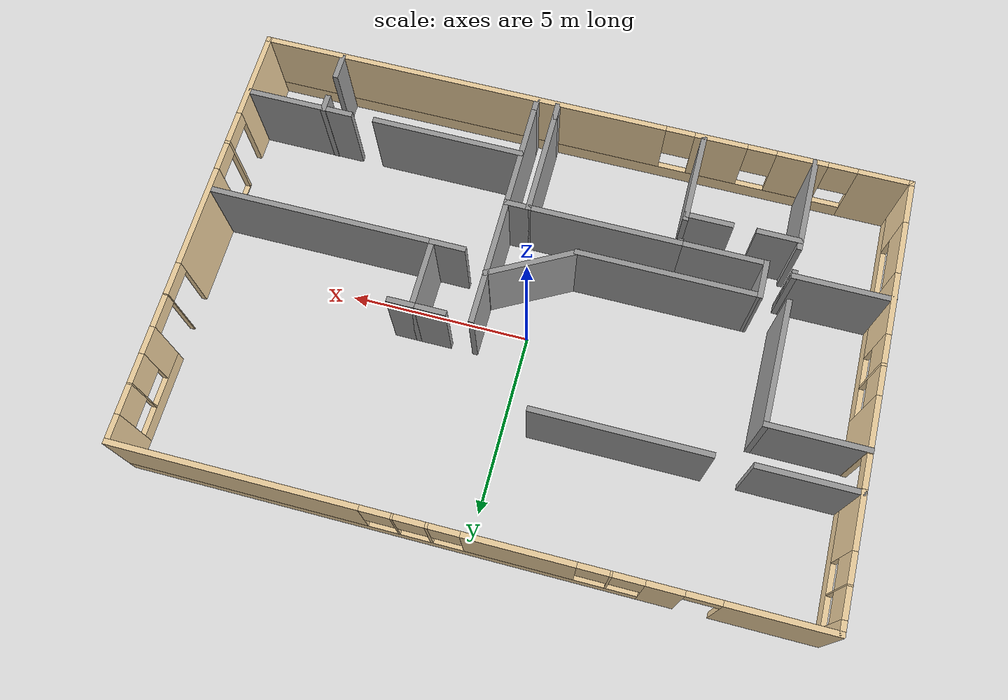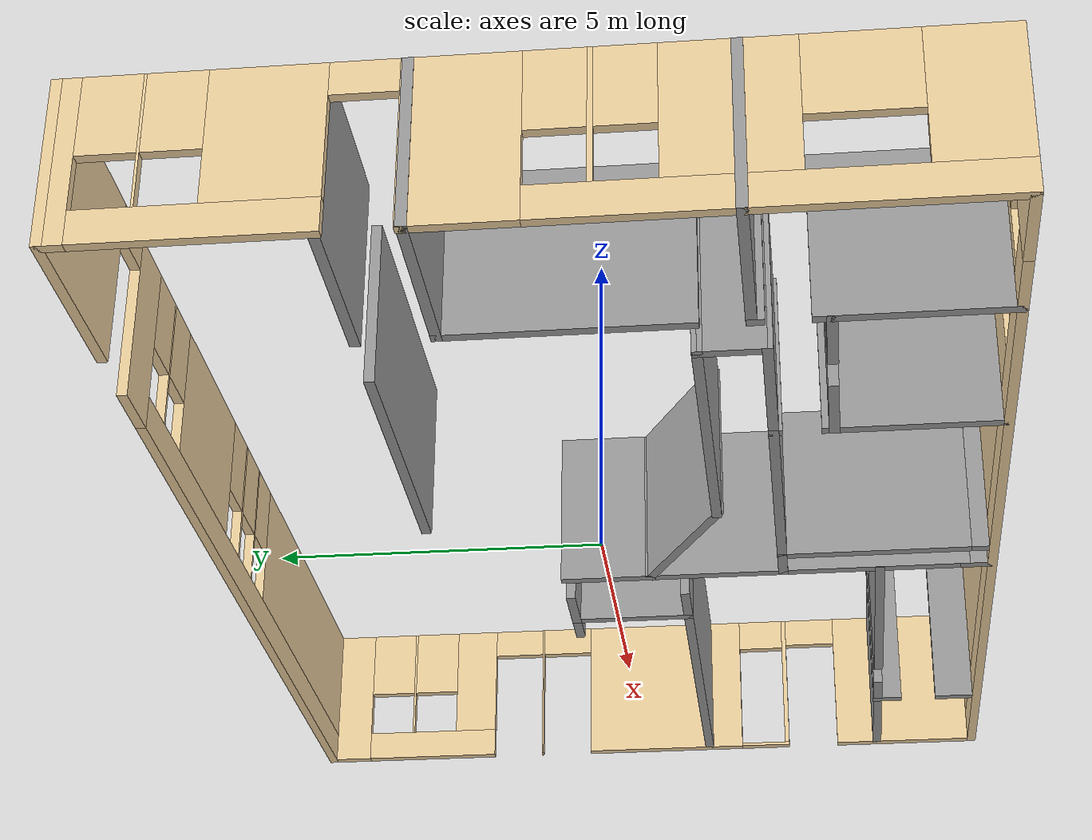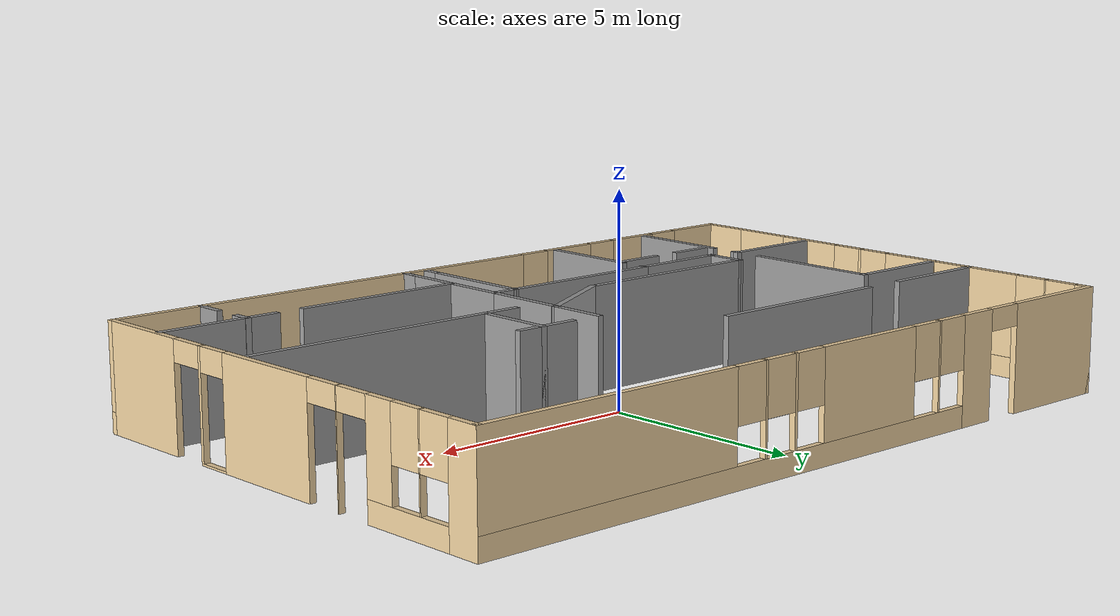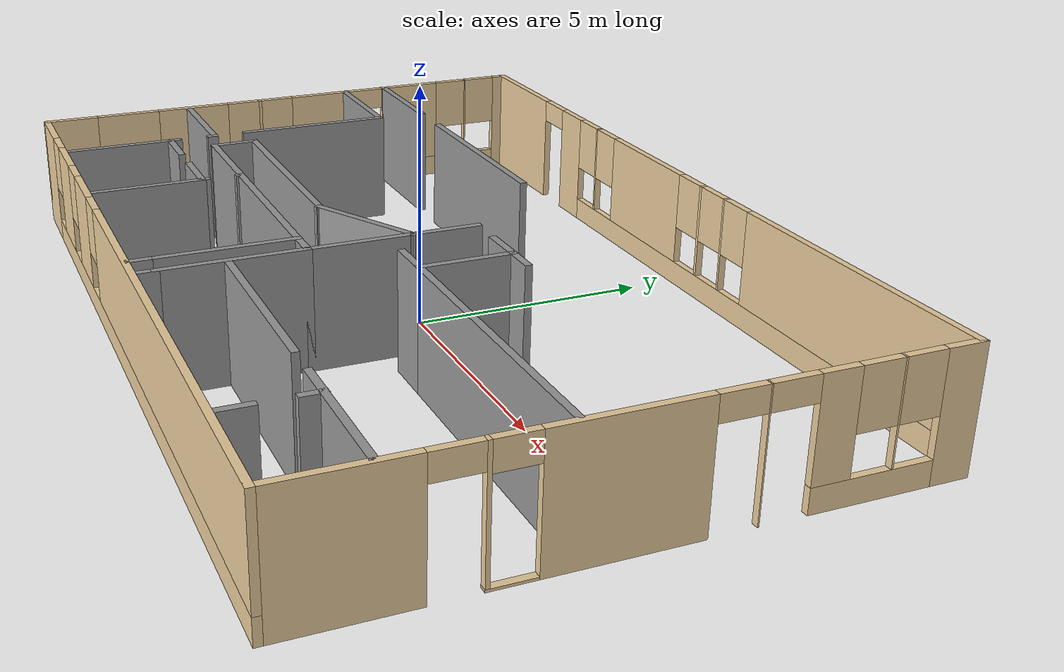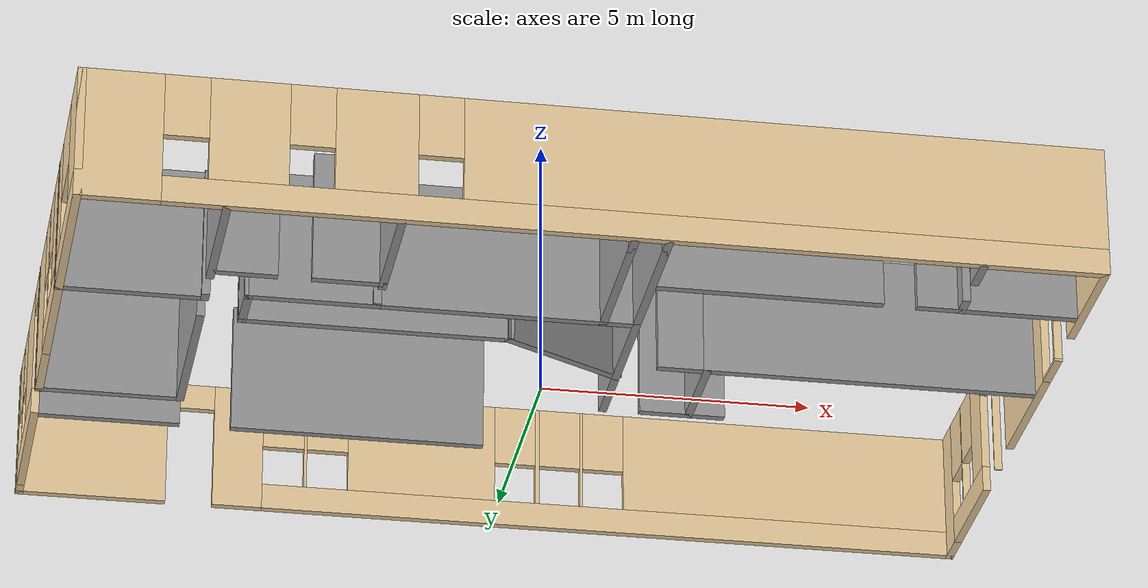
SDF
<?xml version='1.0'?>
<sdf version='1.6'>
  <model name='melgar_house'>
    <link name='Wall_101'>
      <pose frame=''>-3.42579 -4.781 0 0 0 -1.5708</pose>
      <self_collide>0</self_collide>
      <kinematic>0</kinematic>
      <visual name='Wall_101_Visual'>
        <pose frame=''>0 0 1.25 0 -0 0</pose>
        <geometry>
          <box>
            <size>2.5 0.15 2.5</size>
          </box>
        </geometry>
        <material>
          <script>
            <uri>file://media/materials/scripts/gazebo.material</uri>
            <name>Gazebo/Grey</name>
          </script>
          <ambient>1 1 1 1</ambient>
          <shader type='pixel'/>
          <diffuse>0.7 0.7 0.7 1</diffuse>
          <specular>0.01 0.01 0.01 1</specular>
          <emissive>0 0 0 1</emissive>
        </material>
        <meta>
          <layer>0</layer>
        </meta>
        <transparency>0</transparency>
        <cast_shadows>1</cast_shadows>
      </visual>
      <collision name='Wall_101_Collision'>
        <laser_retro>0</laser_retro>
        <max_contacts>10</max_contacts>
        <pose frame=''>0 0 1.25 0 -0 0</pose>
        <geometry>
          <box>
            <size>2.5 0.15 2.5</size>
          </box>
        </geometry>
        <surface>
          <friction>
            <ode>
              <mu>1</mu>
              <mu2>1</mu2>
              <fdir1>0 0 0</fdir1>
              <slip1>0</slip1>
              <slip2>0</slip2>
            </ode>
            <torsional>
              <coefficient>1</coefficient>
              <patch_radius>0</patch_radius>
              <surface_radius>0</surface_radius>
              <use_patch_radius>1</use_patch_radius>
              <ode>
                <slip>0</slip>
              </ode>
            </torsional>
          </friction>
          <bounce>
            <restitution_coefficient>0</restitution_coefficient>
            <threshold>1e+06</threshold>
          </bounce>
          <contact>
            <collide_without_contact>0</collide_without_contact>
            <collide_without_contact_bitmask>1</collide_without_contact_bitmask>
            <collide_bitmask>1</collide_bitmask>
            <ode>
              <soft_cfm>0</soft_cfm>
              <soft_erp>0.2</soft_erp>
              <kp>1e+13</kp>
              <kd>1</kd>
              <max_vel>0.01</max_vel>
              <min_depth>0</min_depth>
            </ode>
            <bullet>
              <split_impulse>1</split_impulse>
              <split_impulse_penetration_threshold>-0.01</split_impulse_penetration_threshold>
              <soft_cfm>0</soft_cfm>
              <soft_erp>0.2</soft_erp>
              <kp>1e+13</kp>
              <kd>1</kd>
            </bullet>
          </contact>
        </surface>
      </collision>
    </link>
    <link name='Wall_105'>
      <pose frame=''>0.674077 -4.18057 0 0 0 -1.5708</pose>
      <self_collide>0</self_collide>
      <kinematic>0</kinematic>
      <visual name='Wall_105_Visual'>
        <pose frame=''>0 0 1.25 0 -0 0</pose>
        <geometry>
          <box>
            <size>3 0.15 2.5</size>
          </box>
        </geometry>
        <material>
          <script>
            <uri>file://media/materials/scripts/gazebo.material</uri>
            <name>Gazebo/Grey</name>
          </script>
          <ambient>1 1 1 1</ambient>
          <shader type='pixel'/>
          <diffuse>0.7 0.7 0.7 1</diffuse>
          <specular>0.01 0.01 0.01 1</specular>
          <emissive>0 0 0 1</emissive>
        </material>
        <meta>
          <layer>0</layer>
        </meta>
        <transparency>0</transparency>
        <cast_shadows>1</cast_shadows>
      </visual>
      <collision name='Wall_105_Collision'>
        <laser_retro>0</laser_retro>
        <max_contacts>10</max_contacts>
        <pose frame=''>0 0 1.25 0 -0 0</pose>
        <geometry>
          <box>
            <size>3 0.15 2.5</size>
          </box>
        </geometry>
        <surface>
          <friction>
            <ode>
              <mu>1</mu>
              <mu2>1</mu2>
              <fdir1>0 0 0</fdir1>
              <slip1>0</slip1>
              <slip2>0</slip2>
            </ode>
            <torsional>
              <coefficient>1</coefficient>
              <patch_radius>0</patch_radius>
              <surface_radius>0</surface_radius>
              <use_patch_radius>1</use_patch_radius>
              <ode>
                <slip>0</slip>
              </ode>
            </torsional>
          </friction>
          <bounce>
            <restitution_coefficient>0</restitution_coefficient>
            <threshold>1e+06</threshold>
          </bounce>
          <contact>
            <collide_without_contact>0</collide_without_contact>
            <collide_without_contact_bitmask>1</collide_without_contact_bitmask>
            <collide_bitmask>1</collide_bitmask>
            <ode>
              <soft_cfm>0</soft_cfm>
              <soft_erp>0.2</soft_erp>
              <kp>1e+13</kp>
              <kd>1</kd>
              <max_vel>0.01</max_vel>
              <min_depth>0</min_depth>
            </ode>
            <bullet>
              <split_impulse>1</split_impulse>
              <split_impulse_penetration_threshold>-0.01</split_impulse_penetration_threshold>
              <soft_cfm>0</soft_cfm>
              <soft_erp>0.2</soft_erp>
              <kp>1e+13</kp>
              <kd>1</kd>
            </bullet>
          </contact>
        </surface>
      </collision>
    </link>
    <link name='Wall_106'>
      <pose frame=''>0.674077 -5.78057 0 0 0 -1.5708</pose>
      <self_collide>0</self_collide>
      <kinematic>0</kinematic>
      <visual name='Wall_106_Visual'>
        <pose frame=''>0 0 1.25 0 -0 0</pose>
        <geometry>
          <box>
            <size>0.5 0.15 2.5</size>
          </box>
        </geometry>
        <material>
          <script>
            <uri>file://media/materials/scripts/gazebo.material</uri>
            <name>Gazebo/Grey</name>
          </script>
          <ambient>1 1 1 1</ambient>
          <shader type='pixel'/>
          <diffuse>0.7 0.7 0.7 1</diffuse>
          <specular>0.01 0.01 0.01 1</specular>
          <emissive>0 0 0 1</emissive>
        </material>
        <meta>
          <layer>0</layer>
        </meta>
        <transparency>0</transparency>
        <cast_shadows>1</cast_shadows>
      </visual>
      <collision name='Wall_106_Collision'>
        <laser_retro>0</laser_retro>
        <max_contacts>10</max_contacts>
        <pose frame=''>0 0 1.25 0 -0 0</pose>
        <geometry>
          <box>
            <size>0.5 0.15 2.5</size>
          </box>
        </geometry>
        <surface>
          <friction>
            <ode>
              <mu>1</mu>
              <mu2>1</mu2>
              <fdir1>0 0 0</fdir1>
              <slip1>0</slip1>
              <slip2>0</slip2>
            </ode>
            <torsional>
              <coefficient>1</coefficient>
              <patch_radius>0</patch_radius>
              <surface_radius>0</surface_radius>
              <use_patch_radius>1</use_patch_radius>
              <ode>
                <slip>0</slip>
              </ode>
            </torsional>
          </friction>
          <bounce>
            <restitution_coefficient>0</restitution_coefficient>
            <threshold>1e+06</threshold>
          </bounce>
          <contact>
            <collide_without_contact>0</collide_without_contact>
            <collide_without_contact_bitmask>1</collide_without_contact_bitmask>
            <collide_bitmask>1</collide_bitmask>
            <ode>
              <soft_cfm>0</soft_cfm>
              <soft_erp>0.2</soft_erp>
              <kp>1e+13</kp>
              <kd>1</kd>
              <max_vel>0.01</max_vel>
              <min_depth>0</min_depth>
            </ode>
            <bullet>
              <split_impulse>1</split_impulse>
              <split_impulse_penetration_threshold>-0.01</split_impulse_penetration_threshold>
              <soft_cfm>0</soft_cfm>
              <soft_erp>0.2</soft_erp>
              <kp>1e+13</kp>
              <kd>1</kd>
            </bullet>
          </contact>
        </surface>
      </collision>
    </link>
    <link name='Wall_108'>
      <pose frame=''>0.974077 -2.75557 0 0 -0 0</pose>
      <self_collide>0</self_collide>
      <kinematic>0</kinematic>
      <visual name='Wall_108_Visual'>
        <pose frame=''>0 0 1.25 0 -0 0</pose>
        <geometry>
          <box>
            <size>0.75 0.15 2.5</size>
          </box>
        </geometry>
        <material>
          <script>
            <uri>file://media/materials/scripts/gazebo.material</uri>
            <name>Gazebo/Grey</name>
          </script>
          <ambient>1 1 1 1</ambient>
          <shader type='pixel'/>
          <diffuse>0.7 0.7 0.7 1</diffuse>
          <specular>0.01 0.01 0.01 1</specular>
          <emissive>0 0 0 1</emissive>
        </material>
        <meta>
          <layer>0</layer>
        </meta>
        <transparency>0</transparency>
        <cast_shadows>1</cast_shadows>
      </visual>
      <collision name='Wall_108_Collision'>
        <laser_retro>0</laser_retro>
        <max_contacts>10</max_contacts>
        <pose frame=''>0 0 1.25 0 -0 0</pose>
        <geometry>
          <box>
            <size>0.75 0.15 2.5</size>
          </box>
        </geometry>
        <surface>
          <friction>
            <ode>
              <mu>1</mu>
              <mu2>1</mu2>
              <fdir1>0 0 0</fdir1>
              <slip1>0</slip1>
              <slip2>0</slip2>
            </ode>
            <torsional>
              <coefficient>1</coefficient>
              <patch_radius>0</patch_radius>
              <surface_radius>0</surface_radius>
              <use_patch_radius>1</use_patch_radius>
              <ode>
                <slip>0</slip>
              </ode>
            </torsional>
          </friction>
          <bounce>
            <restitution_coefficient>0</restitution_coefficient>
            <threshold>1e+06</threshold>
          </bounce>
          <contact>
            <collide_without_contact>0</collide_without_contact>
            <collide_without_contact_bitmask>1</collide_without_contact_bitmask>
            <collide_bitmask>1</collide_bitmask>
            <ode>
              <soft_cfm>0</soft_cfm>
              <soft_erp>0.2</soft_erp>
              <kp>1e+13</kp>
              <kd>1</kd>
              <max_vel>0.01</max_vel>
              <min_depth>0</min_depth>
            </ode>
            <bullet>
              <split_impulse>1</split_impulse>
              <split_impulse_penetration_threshold>-0.01</split_impulse_penetration_threshold>
              <soft_cfm>0</soft_cfm>
              <soft_erp>0.2</soft_erp>
              <kp>1e+13</kp>
              <kd>1</kd>
            </bullet>
          </contact>
        </surface>
      </collision>
    </link>
    <link name='Wall_110'>
      <pose frame=''>1.27408 -4.18057 0 0 0 -1.5708</pose>
      <self_collide>0</self_collide>
      <kinematic>0</kinematic>
      <visual name='Wall_110_Visual'>
        <pose frame=''>0 0 1.25 0 -0 0</pose>
        <geometry>
          <box>
            <size>3 0.15 2.5</size>
          </box>
        </geometry>
        <material>
          <script>
            <uri>file://media/materials/scripts/gazebo.material</uri>
            <name>Gazebo/Grey</name>
          </script>
          <ambient>1 1 1 1</ambient>
          <shader type='pixel'/>
          <diffuse>0.7 0.7 0.7 1</diffuse>
          <specular>0.01 0.01 0.01 1</specular>
          <emissive>0 0 0 1</emissive>
        </material>
        <meta>
          <layer>0</layer>
        </meta>
        <transparency>0</transparency>
        <cast_shadows>1</cast_shadows>
      </visual>
      <collision name='Wall_110_Collision'>
        <laser_retro>0</laser_retro>
        <max_contacts>10</max_contacts>
        <pose frame=''>0 0 1.25 0 -0 0</pose>
        <geometry>
          <box>
            <size>3 0.15 2.5</size>
          </box>
        </geometry>
        <surface>
          <friction>
            <ode>
              <mu>1</mu>
              <mu2>1</mu2>
              <fdir1>0 0 0</fdir1>
              <slip1>0</slip1>
              <slip2>0</slip2>
            </ode>
            <torsional>
              <coefficient>1</coefficient>
              <patch_radius>0</patch_radius>
              <surface_radius>0</surface_radius>
              <use_patch_radius>1</use_patch_radius>
              <ode>
                <slip>0</slip>
              </ode>
            </torsional>
          </friction>
          <bounce>
            <restitution_coefficient>0</restitution_coefficient>
            <threshold>1e+06</threshold>
          </bounce>
          <contact>
            <collide_without_contact>0</collide_without_contact>
            <collide_without_contact_bitmask>1</collide_without_contact_bitmask>
            <collide_bitmask>1</collide_bitmask>
            <ode>
              <soft_cfm>0</soft_cfm>
              <soft_erp>0.2</soft_erp>
              <kp>1e+13</kp>
              <kd>1</kd>
              <max_vel>0.01</max_vel>
              <min_depth>0</min_depth>
            </ode>
            <bullet>
              <split_impulse>1</split_impulse>
              <split_impulse_penetration_threshold>-0.01</split_impulse_penetration_threshold>
              <soft_cfm>0</soft_cfm>
              <soft_erp>0.2</soft_erp>
              <kp>1e+13</kp>
              <kd>1</kd>
            </bullet>
          </contact>
        </surface>
      </collision>
    </link>
    <link name='Wall_111'>
      <pose frame=''>1.27408 -5.78057 0 0 0 -1.5708</pose>
      <self_collide>0</self_collide>
      <kinematic>0</kinematic>
      <visual name='Wall_111_Visual'>
        <pose frame=''>0 0 1.25 0 -0 0</pose>
        <geometry>
          <box>
            <size>0.5 0.15 2.5</size>
          </box>
        </geometry>
        <material>
          <script>
            <uri>file://media/materials/scripts/gazebo.material</uri>
            <name>Gazebo/Grey</name>
          </script>
          <ambient>1 1 1 1</ambient>
          <shader type='pixel'/>
          <diffuse>0.7 0.7 0.7 1</diffuse>
          <specular>0.01 0.01 0.01 1</specular>
          <emissive>0 0 0 1</emissive>
        </material>
        <meta>
          <layer>0</layer>
        </meta>
        <transparency>0</transparency>
        <cast_shadows>1</cast_shadows>
      </visual>
      <collision name='Wall_111_Collision'>
        <laser_retro>0</laser_retro>
        <max_contacts>10</max_contacts>
        <pose frame=''>0 0 1.25 0 -0 0</pose>
        <geometry>
          <box>
            <size>0.5 0.15 2.5</size>
          </box>
        </geometry>
        <surface>
          <friction>
            <ode>
              <mu>1</mu>
              <mu2>1</mu2>
              <fdir1>0 0 0</fdir1>
              <slip1>0</slip1>
              <slip2>0</slip2>
            </ode>
            <torsional>
              <coefficient>1</coefficient>
              <patch_radius>0</patch_radius>
              <surface_radius>0</surface_radius>
              <use_patch_radius>1</use_patch_radius>
              <ode>
                <slip>0</slip>
              </ode>
            </torsional>
          </friction>
          <bounce>
            <restitution_coefficient>0</restitution_coefficient>
            <threshold>1e+06</threshold>
          </bounce>
          <contact>
            <collide_without_contact>0</collide_without_contact>
            <collide_without_contact_bitmask>1</collide_without_contact_bitmask>
            <collide_bitmask>1</collide_bitmask>
            <ode>
              <soft_cfm>0</soft_cfm>
              <soft_erp>0.2</soft_erp>
              <kp>1e+13</kp>
              <kd>1</kd>
              <max_vel>0.01</max_vel>
              <min_depth>0</min_depth>
            </ode>
            <bullet>
              <split_impulse>1</split_impulse>
              <split_impulse_penetration_threshold>-0.01</split_impulse_penetration_threshold>
              <soft_cfm>0</soft_cfm>
              <soft_erp>0.2</soft_erp>
              <kp>1e+13</kp>
              <kd>1</kd>
            </bullet>
          </contact>
        </surface>
      </collision>
    </link>
    <link name='Wall_113'>
      <pose frame=''>-3.30354 -1.82115 0 0 -0 0</pose>
      <self_collide>0</self_collide>
      <kinematic>0</kinematic>
      <visual name='Wall_113_Visual'>
        <pose frame=''>0 0 1.25 0 -0 0</pose>
        <geometry>
          <box>
            <size>5 0.15 2.5</size>
          </box>
        </geometry>
        <material>
          <script>
            <uri>file://media/materials/scripts/gazebo.material</uri>
            <name>Gazebo/Grey</name>
          </script>
          <ambient>1 1 1 1</ambient>
          <shader type='pixel'/>
          <diffuse>0.7 0.7 0.7 1</diffuse>
          <specular>0.01 0.01 0.01 1</specular>
          <emissive>0 0 0 1</emissive>
        </material>
        <meta>
          <layer>0</layer>
        </meta>
        <transparency>0</transparency>
        <cast_shadows>1</cast_shadows>
      </visual>
      <collision name='Wall_113_Collision'>
        <laser_retro>0</laser_retro>
        <max_contacts>10</max_contacts>
        <pose frame=''>0 0 1.25 0 -0 0</pose>
        <geometry>
          <box>
            <size>5 0.15 2.5</size>
          </box>
        </geometry>
        <surface>
          <friction>
            <ode>
              <mu>1</mu>
              <mu2>1</mu2>
              <fdir1>0 0 0</fdir1>
              <slip1>0</slip1>
              <slip2>0</slip2>
            </ode>
            <torsional>
              <coefficient>1</coefficient>
              <patch_radius>0</patch_radius>
              <surface_radius>0</surface_radius>
              <use_patch_radius>1</use_patch_radius>
              <ode>
                <slip>0</slip>
              </ode>
            </torsional>
          </friction>
          <bounce>
            <restitution_coefficient>0</restitution_coefficient>
            <threshold>1e+06</threshold>
          </bounce>
          <contact>
            <collide_without_contact>0</collide_without_contact>
            <collide_without_contact_bitmask>1</collide_without_contact_bitmask>
            <collide_bitmask>1</collide_bitmask>
            <ode>
              <soft_cfm>0</soft_cfm>
              <soft_erp>0.2</soft_erp>
              <kp>1e+13</kp>
              <kd>1</kd>
              <max_vel>0.01</max_vel>
              <min_depth>0</min_depth>
            </ode>
            <bullet>
              <split_impulse>1</split_impulse>
              <split_impulse_penetration_threshold>-0.01</split_impulse_penetration_threshold>
              <soft_cfm>0</soft_cfm>
              <soft_erp>0.2</soft_erp>
              <kp>1e+13</kp>
              <kd>1</kd>
            </bullet>
          </contact>
        </surface>
      </collision>
    </link>
    <link name='Wall_115'>
      <pose frame=''>1.27408 -1.70557 0 0 -0 1.5708</pose>
      <self_collide>0</self_collide>
      <kinematic>0</kinematic>
      <visual name='Wall_115_Visual'>
        <pose frame=''>0 0 1.25 0 -0 0</pose>
        <geometry>
          <box>
            <size>2.25 0.15 2.5</size>
          </box>
        </geometry>
        <material>
          <script>
            <uri>file://media/materials/scripts/gazebo.material</uri>
            <name>Gazebo/Grey</name>
          </script>
          <ambient>1 1 1 1</ambient>
          <shader type='pixel'/>
          <diffuse>0.7 0.7 0.7 1</diffuse>
          <specular>0.01 0.01 0.01 1</specular>
          <emissive>0 0 0 1</emissive>
        </material>
        <meta>
          <layer>0</layer>
        </meta>
        <transparency>0</transparency>
        <cast_shadows>1</cast_shadows>
      </visual>
      <collision name='Wall_115_Collision'>
        <laser_retro>0</laser_retro>
        <max_contacts>10</max_contacts>
        <pose frame=''>0 0 1.25 0 -0 0</pose>
        <geometry>
          <box>
            <size>2.25 0.15 2.5</size>
          </box>
        </geometry>
        <surface>
          <friction>
            <ode>
              <mu>1</mu>
              <mu2>1</mu2>
              <fdir1>0 0 0</fdir1>
              <slip1>0</slip1>
              <slip2>0</slip2>
            </ode>
            <torsional>
              <coefficient>1</coefficient>
              <patch_radius>0</patch_radius>
              <surface_radius>0</surface_radius>
              <use_patch_radius>1</use_patch_radius>
              <ode>
                <slip>0</slip>
              </ode>
            </torsional>
          </friction>
          <bounce>
            <restitution_coefficient>0</restitution_coefficient>
            <threshold>1e+06</threshold>
          </bounce>
          <contact>
            <collide_without_contact>0</collide_without_contact>
            <collide_without_contact_bitmask>1</collide_without_contact_bitmask>
            <collide_bitmask>1</collide_bitmask>
            <ode>
              <soft_cfm>0</soft_cfm>
              <soft_erp>0.2</soft_erp>
              <kp>1e+13</kp>
              <kd>1</kd>
              <max_vel>0.01</max_vel>
              <min_depth>0</min_depth>
            </ode>
            <bullet>
              <split_impulse>1</split_impulse>
              <split_impulse_penetration_threshold>-0.01</split_impulse_penetration_threshold>
              <soft_cfm>0</soft_cfm>
              <soft_erp>0.2</soft_erp>
              <kp>1e+13</kp>
              <kd>1</kd>
            </bullet>
          </contact>
        </surface>
      </collision>
    </link>
    <link name='Wall_116'>
      <pose frame=''>1.27408 0.019431 0 0 -0 1.5708</pose>
      <self_collide>0</self_collide>
      <kinematic>0</kinematic>
      <visual name='Wall_116_Visual'>
        <pose frame=''>0 0 1.25 0 -0 0</pose>
        <geometry>
          <box>
            <size>1.5 0.15 2.5</size>
          </box>
        </geometry>
        <material>
          <script>
            <uri>file://media/materials/scripts/gazebo.material</uri>
            <name>Gazebo/Grey</name>
          </script>
          <ambient>1 1 1 1</ambient>
          <shader type='pixel'/>
          <diffuse>0.7 0.7 0.7 1</diffuse>
          <specular>0.01 0.01 0.01 1</specular>
          <emissive>0 0 0 1</emissive>
        </material>
        <meta>
          <layer>0</layer>
        </meta>
        <transparency>0</transparency>
        <cast_shadows>1</cast_shadows>
      </visual>
      <collision name='Wall_116_Collision'>
        <laser_retro>0</laser_retro>
        <max_contacts>10</max_contacts>
        <pose frame=''>0 0 1.25 0 -0 0</pose>
        <geometry>
          <box>
            <size>1.5 0.15 2.5</size>
          </box>
        </geometry>
        <surface>
          <friction>
            <ode>
              <mu>1</mu>
              <mu2>1</mu2>
              <fdir1>0 0 0</fdir1>
              <slip1>0</slip1>
              <slip2>0</slip2>
            </ode>
            <torsional>
              <coefficient>1</coefficient>
              <patch_radius>0</patch_radius>
              <surface_radius>0</surface_radius>
              <use_patch_radius>1</use_patch_radius>
              <ode>
                <slip>0</slip>
              </ode>
            </torsional>
          </friction>
          <bounce>
            <restitution_coefficient>0</restitution_coefficient>
            <threshold>1e+06</threshold>
          </bounce>
          <contact>
            <collide_without_contact>0</collide_without_contact>
            <collide_without_contact_bitmask>1</collide_without_contact_bitmask>
            <collide_bitmask>1</collide_bitmask>
            <ode>
              <soft_cfm>0</soft_cfm>
              <soft_erp>0.2</soft_erp>
              <kp>1e+13</kp>
              <kd>1</kd>
              <max_vel>0.01</max_vel>
              <min_depth>0</min_depth>
            </ode>
            <bullet>
              <split_impulse>1</split_impulse>
              <split_impulse_penetration_threshold>-0.01</split_impulse_penetration_threshold>
              <soft_cfm>0</soft_cfm>
              <soft_erp>0.2</soft_erp>
              <kp>1e+13</kp>
              <kd>1</kd>
            </bullet>
          </contact>
        </surface>
      </collision>
    </link>
    <link name='Wall_118'>
      <pose frame=''>0.197768 -1.23836 0 0 -0 0.496271</pose>
      <self_collide>0</self_collide>
      <kinematic>0</kinematic>
      <visual name='Wall_118_Visual'>
        <pose frame=''>0 0 1.25 0 -0 0</pose>
        <geometry>
          <box>
            <size>2.59793 0.15 2.5</size>
          </box>
        </geometry>
        <material>
          <script>
            <uri>file://media/materials/scripts/gazebo.material</uri>
            <name>Gazebo/Grey</name>
          </script>
          <ambient>1 1 1 1</ambient>
          <shader type='pixel'/>
          <diffuse>0.7 0.7 0.7 1</diffuse>
          <specular>0.01 0.01 0.01 1</specular>
          <emissive>0 0 0 1</emissive>
        </material>
        <meta>
          <layer>0</layer>
        </meta>
        <transparency>0</transparency>
        <cast_shadows>1</cast_shadows>
      </visual>
      <collision name='Wall_118_Collision'>
        <laser_retro>0</laser_retro>
        <max_contacts>10</max_contacts>
        <pose frame=''>0 0 1.25 0 -0 0</pose>
        <geometry>
          <box>
            <size>2.59793 0.15 2.5</size>
          </box>
        </geometry>
        <surface>
          <friction>
            <ode>
              <mu>1</mu>
              <mu2>1</mu2>
              <fdir1>0 0 0</fdir1>
              <slip1>0</slip1>
              <slip2>0</slip2>
            </ode>
            <torsional>
              <coefficient>1</coefficient>
              <patch_radius>0</patch_radius>
              <surface_radius>0</surface_radius>
              <use_patch_radius>1</use_patch_radius>
              <ode>
                <slip>0</slip>
              </ode>
            </torsional>
          </friction>
          <bounce>
            <restitution_coefficient>0</restitution_coefficient>
            <threshold>1e+06</threshold>
          </bounce>
          <contact>
            <collide_without_contact>0</collide_without_contact>
            <collide_without_contact_bitmask>1</collide_without_contact_bitmask>
            <collide_bitmask>1</collide_bitmask>
            <ode>
              <soft_cfm>0</soft_cfm>
              <soft_erp>0.2</soft_erp>
              <kp>1e+13</kp>
              <kd>1</kd>
              <max_vel>0.01</max_vel>
              <min_depth>0</min_depth>
            </ode>
            <bullet>
              <split_impulse>1</split_impulse>
              <split_impulse_penetration_threshold>-0.01</split_impulse_penetration_threshold>
              <soft_cfm>0</soft_cfm>
              <soft_erp>0.2</soft_erp>
              <kp>1e+13</kp>
              <kd>1</kd>
            </bullet>
          </contact>
        </surface>
      </collision>
    </link>
    <link name='Wall_122'>
      <pose frame=''>2.44908 0.694431 0 0 -0 0</pose>
      <self_collide>0</self_collide>
      <kinematic>0</kinematic>
      <visual name='Wall_122_Visual'>
        <pose frame=''>0 0 1.25 0 -0 0</pose>
        <geometry>
          <box>
            <size>1 0.15 2.5</size>
          </box>
        </geometry>
        <material>
          <script>
            <uri>file://media/materials/scripts/gazebo.material</uri>
            <name>Gazebo/Grey</name>
          </script>
          <ambient>1 1 1 1</ambient>
          <shader type='pixel'/>
          <diffuse>0.7 0.7 0.7 1</diffuse>
          <specular>0.01 0.01 0.01 1</specular>
          <emissive>0 0 0 1</emissive>
        </material>
        <meta>
          <layer>0</layer>
        </meta>
        <transparency>0</transparency>
        <cast_shadows>1</cast_shadows>
      </visual>
      <collision name='Wall_122_Collision'>
        <laser_retro>0</laser_retro>
        <max_contacts>10</max_contacts>
        <pose frame=''>0 0 1.25 0 -0 0</pose>
        <geometry>
          <box>
            <size>1 0.15 2.5</size>
          </box>
        </geometry>
        <surface>
          <friction>
            <ode>
              <mu>1</mu>
              <mu2>1</mu2>
              <fdir1>0 0 0</fdir1>
              <slip1>0</slip1>
              <slip2>0</slip2>
            </ode>
            <torsional>
              <coefficient>1</coefficient>
              <patch_radius>0</patch_radius>
              <surface_radius>0</surface_radius>
              <use_patch_radius>1</use_patch_radius>
              <ode>
                <slip>0</slip>
              </ode>
            </torsional>
          </friction>
          <bounce>
            <restitution_coefficient>0</restitution_coefficient>
            <threshold>1e+06</threshold>
          </bounce>
          <contact>
            <collide_without_contact>0</collide_without_contact>
            <collide_without_contact_bitmask>1</collide_without_contact_bitmask>
            <collide_bitmask>1</collide_bitmask>
            <ode>
              <soft_cfm>0</soft_cfm>
              <soft_erp>0.2</soft_erp>
              <kp>1e+13</kp>
              <kd>1</kd>
              <max_vel>0.01</max_vel>
              <min_depth>0</min_depth>
            </ode>
            <bullet>
              <split_impulse>1</split_impulse>
              <split_impulse_penetration_threshold>-0.01</split_impulse_penetration_threshold>
              <soft_cfm>0</soft_cfm>
              <soft_erp>0.2</soft_erp>
              <kp>1e+13</kp>
              <kd>1</kd>
            </bullet>
          </contact>
        </surface>
      </collision>
    </link>
    <link name='Wall_123'>
      <pose frame=''>3.17408 0.694431 0 0 -0 0</pose>
      <self_collide>0</self_collide>
      <kinematic>0</kinematic>
      <visual name='Wall_123_Visual'>
        <pose frame=''>0 0 1.25 0 -0 0</pose>
        <geometry>
          <box>
            <size>0.75 0.15 2.5</size>
          </box>
        </geometry>
        <material>
          <script>
            <uri>file://media/materials/scripts/gazebo.material</uri>
            <name>Gazebo/Grey</name>
          </script>
          <ambient>1 1 1 1</ambient>
          <shader type='pixel'/>
          <diffuse>0.7 0.7 0.7 1</diffuse>
          <specular>0.01 0.01 0.01 1</specular>
          <emissive>0 0 0 1</emissive>
        </material>
        <meta>
          <layer>0</layer>
        </meta>
        <transparency>0</transparency>
        <cast_shadows>1</cast_shadows>
      </visual>
      <collision name='Wall_123_Collision'>
        <laser_retro>0</laser_retro>
        <max_contacts>10</max_contacts>
        <pose frame=''>0 0 1.25 0 -0 0</pose>
        <geometry>
          <box>
            <size>0.75 0.15 2.5</size>
          </box>
        </geometry>
        <surface>
          <friction>
            <ode>
              <mu>1</mu>
              <mu2>1</mu2>
              <fdir1>0 0 0</fdir1>
              <slip1>0</slip1>
              <slip2>0</slip2>
            </ode>
            <torsional>
              <coefficient>1</coefficient>
              <patch_radius>0</patch_radius>
              <surface_radius>0</surface_radius>
              <use_patch_radius>1</use_patch_radius>
              <ode>
                <slip>0</slip>
              </ode>
            </torsional>
          </friction>
          <bounce>
            <restitution_coefficient>0</restitution_coefficient>
            <threshold>1e+06</threshold>
          </bounce>
          <contact>
            <collide_without_contact>0</collide_without_contact>
            <collide_without_contact_bitmask>1</collide_without_contact_bitmask>
            <collide_bitmask>1</collide_bitmask>
            <ode>
              <soft_cfm>0</soft_cfm>
              <soft_erp>0.2</soft_erp>
              <kp>1e+13</kp>
              <kd>1</kd>
              <max_vel>0.01</max_vel>
              <min_depth>0</min_depth>
            </ode>
            <bullet>
              <split_impulse>1</split_impulse>
              <split_impulse_penetration_threshold>-0.01</split_impulse_penetration_threshold>
              <soft_cfm>0</soft_cfm>
              <soft_erp>0.2</soft_erp>
              <kp>1e+13</kp>
              <kd>1</kd>
            </bullet>
          </contact>
        </surface>
      </collision>
    </link>
    <link name='Wall_125'>
      <pose frame=''>2.87408 -0.230569 0 0 0 -1.5708</pose>
      <self_collide>0</self_collide>
      <kinematic>0</kinematic>
      <visual name='Wall_125_Visual'>
        <pose frame=''>0 0 1.25 0 -0 0</pose>
        <geometry>
          <box>
            <size>2 0.15 2.5</size>
          </box>
        </geometry>
        <material>
          <script>
            <uri>file://media/materials/scripts/gazebo.material</uri>
            <name>Gazebo/Grey</name>
          </script>
          <ambient>1 1 1 1</ambient>
          <shader type='pixel'/>
          <diffuse>0.7 0.7 0.7 1</diffuse>
          <specular>0.01 0.01 0.01 1</specular>
          <emissive>0 0 0 1</emissive>
        </material>
        <meta>
          <layer>0</layer>
        </meta>
        <transparency>0</transparency>
        <cast_shadows>1</cast_shadows>
      </visual>
      <collision name='Wall_125_Collision'>
        <laser_retro>0</laser_retro>
        <max_contacts>10</max_contacts>
        <pose frame=''>0 0 1.25 0 -0 0</pose>
        <geometry>
          <box>
            <size>2 0.15 2.5</size>
          </box>
        </geometry>
        <surface>
          <friction>
            <ode>
              <mu>1</mu>
              <mu2>1</mu2>
              <fdir1>0 0 0</fdir1>
              <slip1>0</slip1>
              <slip2>0</slip2>
            </ode>
            <torsional>
              <coefficient>1</coefficient>
              <patch_radius>0</patch_radius>
              <surface_radius>0</surface_radius>
              <use_patch_radius>1</use_patch_radius>
              <ode>
                <slip>0</slip>
              </ode>
            </torsional>
          </friction>
          <bounce>
            <restitution_coefficient>0</restitution_coefficient>
            <threshold>1e+06</threshold>
          </bounce>
          <contact>
            <collide_without_contact>0</collide_without_contact>
            <collide_without_contact_bitmask>1</collide_without_contact_bitmask>
            <collide_bitmask>1</collide_bitmask>
            <ode>
              <soft_cfm>0</soft_cfm>
              <soft_erp>0.2</soft_erp>
              <kp>1e+13</kp>
              <kd>1</kd>
              <max_vel>0.01</max_vel>
              <min_depth>0</min_depth>
            </ode>
            <bullet>
              <split_impulse>1</split_impulse>
              <split_impulse_penetration_threshold>-0.01</split_impulse_penetration_threshold>
              <soft_cfm>0</soft_cfm>
              <soft_erp>0.2</soft_erp>
              <kp>1e+13</kp>
              <kd>1</kd>
            </bullet>
          </contact>
        </surface>
      </collision>
    </link>
    <link name='Wall_127'>
      <pose frame=''>5.92408 -1.15557 0 0 -0 0</pose>
      <self_collide>0</self_collide>
      <kinematic>0</kinematic>
      <visual name='Wall_127_Visual'>
        <pose frame=''>0 0 1.25 0 -0 0</pose>
        <geometry>
          <box>
            <size>6.25 0.15 2.5</size>
          </box>
        </geometry>
        <material>
          <script>
            <uri>file://media/materials/scripts/gazebo.material</uri>
            <name>Gazebo/Grey</name>
          </script>
          <ambient>1 1 1 1</ambient>
          <shader type='pixel'/>
          <diffuse>0.7 0.7 0.7 1</diffuse>
          <specular>0.01 0.01 0.01 1</specular>
          <emissive>0 0 0 1</emissive>
        </material>
        <meta>
          <layer>0</layer>
        </meta>
        <transparency>0</transparency>
        <cast_shadows>1</cast_shadows>
      </visual>
      <collision name='Wall_127_Collision'>
        <laser_retro>0</laser_retro>
        <max_contacts>10</max_contacts>
        <pose frame=''>0 0 1.25 0 -0 0</pose>
        <geometry>
          <box>
            <size>6.25 0.15 2.5</size>
          </box>
        </geometry>
        <surface>
          <friction>
            <ode>
              <mu>1</mu>
              <mu2>1</mu2>
              <fdir1>0 0 0</fdir1>
              <slip1>0</slip1>
              <slip2>0</slip2>
            </ode>
            <torsional>
              <coefficient>1</coefficient>
              <patch_radius>0</patch_radius>
              <surface_radius>0</surface_radius>
              <use_patch_radius>1</use_patch_radius>
              <ode>
                <slip>0</slip>
              </ode>
            </torsional>
          </friction>
          <bounce>
            <restitution_coefficient>0</restitution_coefficient>
            <threshold>1e+06</threshold>
          </bounce>
          <contact>
            <collide_without_contact>0</collide_without_contact>
            <collide_without_contact_bitmask>1</collide_without_contact_bitmask>
            <collide_bitmask>1</collide_bitmask>
            <ode>
              <soft_cfm>0</soft_cfm>
              <soft_erp>0.2</soft_erp>
              <kp>1e+13</kp>
              <kd>1</kd>
              <max_vel>0.01</max_vel>
              <min_depth>0</min_depth>
            </ode>
            <bullet>
              <split_impulse>1</split_impulse>
              <split_impulse_penetration_threshold>-0.01</split_impulse_penetration_threshold>
              <soft_cfm>0</soft_cfm>
              <soft_erp>0.2</soft_erp>
              <kp>1e+13</kp>
              <kd>1</kd>
            </bullet>
          </contact>
        </surface>
      </collision>
    </link>
    <link name='Wall_129'>
      <pose frame=''>3.34267 -4.27823 0 0 -0 0</pose>
      <self_collide>0</self_collide>
      <kinematic>0</kinematic>
      <visual name='Wall_129_Visual'>
        <pose frame=''>0 0 1.25 0 -0 0</pose>
        <geometry>
          <box>
            <size>4.25 0.15 2.5</size>
          </box>
        </geometry>
        <material>
          <script>
            <uri>file://media/materials/scripts/gazebo.material</uri>
            <name>Gazebo/Grey</name>
          </script>
          <ambient>1 1 1 1</ambient>
          <shader type='pixel'/>
          <diffuse>0.7 0.7 0.7 1</diffuse>
          <specular>0.01 0.01 0.01 1</specular>
          <emissive>0 0 0 1</emissive>
        </material>
        <meta>
          <layer>0</layer>
        </meta>
        <transparency>0</transparency>
        <cast_shadows>1</cast_shadows>
      </visual>
      <collision name='Wall_129_Collision'>
        <laser_retro>0</laser_retro>
        <max_contacts>10</max_contacts>
        <pose frame=''>0 0 1.25 0 -0 0</pose>
        <geometry>
          <box>
            <size>4.25 0.15 2.5</size>
          </box>
        </geometry>
        <surface>
          <friction>
            <ode>
              <mu>1</mu>
              <mu2>1</mu2>
              <fdir1>0 0 0</fdir1>
              <slip1>0</slip1>
              <slip2>0</slip2>
            </ode>
            <torsional>
              <coefficient>1</coefficient>
              <patch_radius>0</patch_radius>
              <surface_radius>0</surface_radius>
              <use_patch_radius>1</use_patch_radius>
              <ode>
                <slip>0</slip>
              </ode>
            </torsional>
          </friction>
          <bounce>
            <restitution_coefficient>0</restitution_coefficient>
            <threshold>1e+06</threshold>
          </bounce>
          <contact>
            <collide_without_contact>0</collide_without_contact>
            <collide_without_contact_bitmask>1</collide_without_contact_bitmask>
            <collide_bitmask>1</collide_bitmask>
            <ode>
              <soft_cfm>0</soft_cfm>
              <soft_erp>0.2</soft_erp>
              <kp>1e+13</kp>
              <kd>1</kd>
              <max_vel>0.01</max_vel>
              <min_depth>0</min_depth>
            </ode>
            <bullet>
              <split_impulse>1</split_impulse>
              <split_impulse_penetration_threshold>-0.01</split_impulse_penetration_threshold>
              <soft_cfm>0</soft_cfm>
              <soft_erp>0.2</soft_erp>
              <kp>1e+13</kp>
              <kd>1</kd>
            </bullet>
          </contact>
        </surface>
      </collision>
    </link>
    <link name='Wall_132'>
      <pose frame=''>7.56766 -4.27823 0 0 -0 0</pose>
      <self_collide>0</self_collide>
      <kinematic>0</kinematic>
      <visual name='Wall_132_Visual'>
        <pose frame=''>0 0 1.25 0 -0 0</pose>
        <geometry>
          <box>
            <size>3 0.15 2.5</size>
          </box>
        </geometry>
        <material>
          <script>
            <uri>file://media/materials/scripts/gazebo.material</uri>
            <name>Gazebo/Grey</name>
          </script>
          <ambient>1 1 1 1</ambient>
          <shader type='pixel'/>
          <diffuse>0.7 0.7 0.7 1</diffuse>
          <specular>0.01 0.01 0.01 1</specular>
          <emissive>0 0 0 1</emissive>
        </material>
        <meta>
          <layer>0</layer>
        </meta>
        <transparency>0</transparency>
        <cast_shadows>1</cast_shadows>
      </visual>
      <collision name='Wall_132_Collision'>
        <laser_retro>0</laser_retro>
        <max_contacts>10</max_contacts>
        <pose frame=''>0 0 1.25 0 -0 0</pose>
        <geometry>
          <box>
            <size>3 0.15 2.5</size>
          </box>
        </geometry>
        <surface>
          <friction>
            <ode>
              <mu>1</mu>
              <mu2>1</mu2>
              <fdir1>0 0 0</fdir1>
              <slip1>0</slip1>
              <slip2>0</slip2>
            </ode>
            <torsional>
              <coefficient>1</coefficient>
              <patch_radius>0</patch_radius>
              <surface_radius>0</surface_radius>
              <use_patch_radius>1</use_patch_radius>
              <ode>
                <slip>0</slip>
              </ode>
            </torsional>
          </friction>
          <bounce>
            <restitution_coefficient>0</restitution_coefficient>
            <threshold>1e+06</threshold>
          </bounce>
          <contact>
            <collide_without_contact>0</collide_without_contact>
            <collide_without_contact_bitmask>1</collide_without_contact_bitmask>
            <collide_bitmask>1</collide_bitmask>
            <ode>
              <soft_cfm>0</soft_cfm>
              <soft_erp>0.2</soft_erp>
              <kp>1e+13</kp>
              <kd>1</kd>
              <max_vel>0.01</max_vel>
              <min_depth>0</min_depth>
            </ode>
            <bullet>
              <split_impulse>1</split_impulse>
              <split_impulse_penetration_threshold>-0.01</split_impulse_penetration_threshold>
              <soft_cfm>0</soft_cfm>
              <soft_erp>0.2</soft_erp>
              <kp>1e+13</kp>
              <kd>1</kd>
            </bullet>
          </contact>
        </surface>
      </collision>
    </link>
    <link name='Wall_135'>
      <pose frame=''>6.88905 -4.4461 0 0 0 -1.5708</pose>
      <self_collide>0</self_collide>
      <kinematic>0</kinematic>
      <visual name='Wall_135_Visual'>
        <pose frame=''>0 0 1.25 0 -0 0</pose>
        <geometry>
          <box>
            <size>0.5 0.15 2.5</size>
          </box>
        </geometry>
        <material>
          <script>
            <uri>file://media/materials/scripts/gazebo.material</uri>
            <name>Gazebo/Grey</name>
          </script>
          <ambient>1 1 1 1</ambient>
          <shader type='pixel'/>
          <diffuse>0.7 0.7 0.7 1</diffuse>
          <specular>0.01 0.01 0.01 1</specular>
          <emissive>0 0 0 1</emissive>
        </material>
        <meta>
          <layer>0</layer>
        </meta>
        <transparency>0</transparency>
        <cast_shadows>1</cast_shadows>
      </visual>
      <collision name='Wall_135_Collision'>
        <laser_retro>0</laser_retro>
        <max_contacts>10</max_contacts>
        <pose frame=''>0 0 1.25 0 -0 0</pose>
        <geometry>
          <box>
            <size>0.5 0.15 2.5</size>
          </box>
        </geometry>
        <surface>
          <friction>
            <ode>
              <mu>1</mu>
              <mu2>1</mu2>
              <fdir1>0 0 0</fdir1>
              <slip1>0</slip1>
              <slip2>0</slip2>
            </ode>
            <torsional>
              <coefficient>1</coefficient>
              <patch_radius>0</patch_radius>
              <surface_radius>0</surface_radius>
              <use_patch_radius>1</use_patch_radius>
              <ode>
                <slip>0</slip>
              </ode>
            </torsional>
          </friction>
          <bounce>
            <restitution_coefficient>0</restitution_coefficient>
            <threshold>1e+06</threshold>
          </bounce>
          <contact>
            <collide_without_contact>0</collide_without_contact>
            <collide_without_contact_bitmask>1</collide_without_contact_bitmask>
            <collide_bitmask>1</collide_bitmask>
            <ode>
              <soft_cfm>0</soft_cfm>
              <soft_erp>0.2</soft_erp>
              <kp>1e+13</kp>
              <kd>1</kd>
              <max_vel>0.01</max_vel>
              <min_depth>0</min_depth>
            </ode>
            <bullet>
              <split_impulse>1</split_impulse>
              <split_impulse_penetration_threshold>-0.01</split_impulse_penetration_threshold>
              <soft_cfm>0</soft_cfm>
              <soft_erp>0.2</soft_erp>
              <kp>1e+13</kp>
              <kd>1</kd>
            </bullet>
          </contact>
        </surface>
      </collision>
    </link>
    <link name='Wall_138'>
      <pose frame=''>6.88905 -5.6711 0 0 0 -1.5708</pose>
      <self_collide>0</self_collide>
      <kinematic>0</kinematic>
      <visual name='Wall_138_Visual'>
        <pose frame=''>0 0 1.25 0 -0 0</pose>
        <geometry>
          <box>
            <size>0.75 0.15 2.5</size>
          </box>
        </geometry>
        <material>
          <script>
            <uri>file://media/materials/scripts/gazebo.material</uri>
            <name>Gazebo/Grey</name>
          </script>
          <ambient>1 1 1 1</ambient>
          <shader type='pixel'/>
          <diffuse>0.7 0.7 0.7 1</diffuse>
          <specular>0.01 0.01 0.01 1</specular>
          <emissive>0 0 0 1</emissive>
        </material>
        <meta>
          <layer>0</layer>
        </meta>
        <transparency>0</transparency>
        <cast_shadows>1</cast_shadows>
      </visual>
      <collision name='Wall_138_Collision'>
        <laser_retro>0</laser_retro>
        <max_contacts>10</max_contacts>
        <pose frame=''>0 0 1.25 0 -0 0</pose>
        <geometry>
          <box>
            <size>0.75 0.15 2.5</size>
          </box>
        </geometry>
        <surface>
          <friction>
            <ode>
              <mu>1</mu>
              <mu2>1</mu2>
              <fdir1>0 0 0</fdir1>
              <slip1>0</slip1>
              <slip2>0</slip2>
            </ode>
            <torsional>
              <coefficient>1</coefficient>
              <patch_radius>0</patch_radius>
              <surface_radius>0</surface_radius>
              <use_patch_radius>1</use_patch_radius>
              <ode>
                <slip>0</slip>
              </ode>
            </torsional>
          </friction>
          <bounce>
            <restitution_coefficient>0</restitution_coefficient>
            <threshold>1e+06</threshold>
          </bounce>
          <contact>
            <collide_without_contact>0</collide_without_contact>
            <collide_without_contact_bitmask>1</collide_without_contact_bitmask>
            <collide_bitmask>1</collide_bitmask>
            <ode>
              <soft_cfm>0</soft_cfm>
              <soft_erp>0.2</soft_erp>
              <kp>1e+13</kp>
              <kd>1</kd>
              <max_vel>0.01</max_vel>
              <min_depth>0</min_depth>
            </ode>
            <bullet>
              <split_impulse>1</split_impulse>
              <split_impulse_penetration_threshold>-0.01</split_impulse_penetration_threshold>
              <soft_cfm>0</soft_cfm>
              <soft_erp>0.2</soft_erp>
              <kp>1e+13</kp>
              <kd>1</kd>
            </bullet>
          </contact>
        </surface>
      </collision>
    </link>
    <link name='Wall_140'>
      <pose frame=''>2.44908 -1.15557 0 0 -0 3.14159</pose>
      <self_collide>0</self_collide>
      <kinematic>0</kinematic>
      <visual name='Wall_140_Visual'>
        <pose frame=''>0 0 1.25 0 -0 0</pose>
        <geometry>
          <box>
            <size>1 0.15 2.5</size>
          </box>
        </geometry>
        <material>
          <script>
            <uri>file://media/materials/scripts/gazebo.material</uri>
            <name>Gazebo/Grey</name>
          </script>
          <ambient>1 1 1 1</ambient>
          <shader type='pixel'/>
          <diffuse>0.7 0.7 0.7 1</diffuse>
          <specular>0.01 0.01 0.01 1</specular>
          <emissive>0 0 0 1</emissive>
        </material>
        <meta>
          <layer>0</layer>
        </meta>
        <transparency>0</transparency>
        <cast_shadows>1</cast_shadows>
      </visual>
      <collision name='Wall_140_Collision'>
        <laser_retro>0</laser_retro>
        <max_contacts>10</max_contacts>
        <pose frame=''>0 0 1.25 0 -0 0</pose>
        <geometry>
          <box>
            <size>1 0.15 2.5</size>
          </box>
        </geometry>
        <surface>
          <friction>
            <ode>
              <mu>1</mu>
              <mu2>1</mu2>
              <fdir1>0 0 0</fdir1>
              <slip1>0</slip1>
              <slip2>0</slip2>
            </ode>
            <torsional>
              <coefficient>1</coefficient>
              <patch_radius>0</patch_radius>
              <surface_radius>0</surface_radius>
              <use_patch_radius>1</use_patch_radius>
              <ode>
                <slip>0</slip>
              </ode>
            </torsional>
          </friction>
          <bounce>
            <restitution_coefficient>0</restitution_coefficient>
            <threshold>1e+06</threshold>
          </bounce>
          <contact>
            <collide_without_contact>0</collide_without_contact>
            <collide_without_contact_bitmask>1</collide_without_contact_bitmask>
            <collide_bitmask>1</collide_bitmask>
            <ode>
              <soft_cfm>0</soft_cfm>
              <soft_erp>0.2</soft_erp>
              <kp>1e+13</kp>
              <kd>1</kd>
              <max_vel>0.01</max_vel>
              <min_depth>0</min_depth>
            </ode>
            <bullet>
              <split_impulse>1</split_impulse>
              <split_impulse_penetration_threshold>-0.01</split_impulse_penetration_threshold>
              <soft_cfm>0</soft_cfm>
              <soft_erp>0.2</soft_erp>
              <kp>1e+13</kp>
              <kd>1</kd>
            </bullet>
          </contact>
        </surface>
      </collision>
    </link>
    <link name='Wall_44'>
      <pose frame=''>0.00354 6.025 0 0 -0 0</pose>
      <self_collide>0</self_collide>
      <kinematic>0</kinematic>
      <visual name='Wall_44_Visual_0'>
        <pose frame=''>-7.72215 0 1.25 0 -0 0</pose>
        <geometry>
          <box>
            <size>2.85569 0.15 2.5</size>
          </box>
        </geometry>
        <material>
          <script>
            <uri>file://media/materials/scripts/gazebo.material</uri>
            <name>Gazebo/Grey</name>
          </script>
          <ambient>0.921569 0.807843 0.615686 1</ambient>
          <shader type='pixel'/>
          <diffuse>0.7 0.7 0.7 1</diffuse>
          <specular>0.01 0.01 0.01 1</specular>
          <emissive>0 0 0 1</emissive>
        </material>
        <meta>
          <layer>0</layer>
        </meta>
        <transparency>0</transparency>
        <cast_shadows>1</cast_shadows>
      </visual>
      <visual name='Wall_44_Visual_1'>
        <pose frame=''>-4.91854 0 1.25 0 -0 0</pose>
        <geometry>
          <box>
            <size>0.951528 0.15 2.5</size>
          </box>
        </geometry>
        <material>
          <script>
            <uri>file://media/materials/scripts/gazebo.material</uri>
            <name>Gazebo/Grey</name>
          </script>
          <ambient>0.921569 0.807843 0.615686 1</ambient>
          <shader type='pixel'/>
          <diffuse>0.7 0.7 0.7 1</diffuse>
          <specular>0.01 0.01 0.01 1</specular>
          <emissive>0 0 0 1</emissive>
        </material>
        <meta>
          <layer>0</layer>
        </meta>
        <transparency>0</transparency>
        <cast_shadows>1</cast_shadows>
      </visual>
      <visual name='Wall_44_Visual_2'>
        <pose frame=''>2.35361 0 0.25 0 -0 0</pose>
        <geometry>
          <box>
            <size>13.5928 0.15 0.5</size>
          </box>
        </geometry>
        <material>
          <script>
            <uri>file://media/materials/scripts/gazebo.material</uri>
            <name>Gazebo/Grey</name>
          </script>
          <ambient>0.921569 0.807843 0.615686 1</ambient>
          <shader type='pixel'/>
          <diffuse>0.7 0.7 0.7 1</diffuse>
          <specular>0.01 0.01 0.01 1</specular>
          <emissive>0 0 0 1</emissive>
        </material>
        <meta>
          <layer>0</layer>
        </meta>
        <transparency>0</transparency>
        <cast_shadows>1</cast_shadows>
      </visual>
      <visual name='Wall_44_Visual_3'>
        <pose frame=''>-3.61514 0 1.5 0 -0 0</pose>
        <geometry>
          <box>
            <size>0.055271 0.15 2</size>
          </box>
        </geometry>
        <material>
          <script>
            <uri>file://media/materials/scripts/gazebo.material</uri>
            <name>Gazebo/Grey</name>
          </script>
          <ambient>0.921569 0.807843 0.615686 1</ambient>
          <shader type='pixel'/>
          <diffuse>0.7 0.7 0.7 1</diffuse>
          <specular>0.01 0.01 0.01 1</specular>
          <emissive>0 0 0 1</emissive>
        </material>
        <meta>
          <layer>0</layer>
        </meta>
        <transparency>0</transparency>
        <cast_shadows>1</cast_shadows>
      </visual>
      <visual name='Wall_44_Visual_4'>
        <pose frame=''>-1.35868 0 1.5 0 -0 0</pose>
        <geometry>
          <box>
            <size>2.85765 0.15 2</size>
          </box>
        </geometry>
        <material>
          <script>
            <uri>file://media/materials/scripts/gazebo.material</uri>
            <name>Gazebo/Grey</name>
          </script>
          <ambient>0.921569 0.807843 0.615686 1</ambient>
          <shader type='pixel'/>
          <diffuse>0.7 0.7 0.7 1</diffuse>
          <specular>0.01 0.01 0.01 1</specular>
          <emissive>0 0 0 1</emissive>
        </material>
        <meta>
          <layer>0</layer>
        </meta>
        <transparency>0</transparency>
        <cast_shadows>1</cast_shadows>
      </visual>
      <visual name='Wall_44_Visual_5'>
        <pose frame=''>0.906874 0 1.5 0 -0 0</pose>
        <geometry>
          <box>
            <size>0.073468 0.15 2</size>
          </box>
        </geometry>
        <material>
          <script>
            <uri>file://media/materials/scripts/gazebo.material</uri>
            <name>Gazebo/Grey</name>
          </script>
          <ambient>0.921569 0.807843 0.615686 1</ambient>
          <shader type='pixel'/>
          <diffuse>0.7 0.7 0.7 1</diffuse>
          <specular>0.01 0.01 0.01 1</specular>
          <emissive>0 0 0 1</emissive>
        </material>
        <meta>
          <layer>0</layer>
        </meta>
        <transparency>0</transparency>
        <cast_shadows>1</cast_shadows>
      </visual>
      <visual name='Wall_44_Visual_6'>
        <pose frame=''>1.77124 0 1.5 0 -0 0</pose>
        <geometry>
          <box>
            <size>0.055271 0.15 2</size>
          </box>
        </geometry>
        <material>
          <script>
            <uri>file://media/materials/scripts/gazebo.material</uri>
            <name>Gazebo/Grey</name>
          </script>
          <ambient>0.921569 0.807843 0.615686 1</ambient>
          <shader type='pixel'/>
          <diffuse>0.7 0.7 0.7 1</diffuse>
          <specular>0.01 0.01 0.01 1</specular>
          <emissive>0 0 0 1</emissive>
        </material>
        <meta>
          <layer>0</layer>
        </meta>
        <transparency>0</transparency>
        <cast_shadows>1</cast_shadows>
      </visual>
      <visual name='Wall_44_Visual_7'>
        <pose frame=''>5.87444 0 1.5 0 -0 0</pose>
        <geometry>
          <box>
            <size>6.55112 0.15 2</size>
          </box>
        </geometry>
        <material>
          <script>
            <uri>file://media/materials/scripts/gazebo.material</uri>
            <name>Gazebo/Grey</name>
          </script>
          <ambient>0.921569 0.807843 0.615686 1</ambient>
          <shader type='pixel'/>
          <diffuse>0.7 0.7 0.7 1</diffuse>
          <specular>0.01 0.01 0.01 1</specular>
          <emissive>0 0 0 1</emissive>
        </material>
        <meta>
          <layer>0</layer>
        </meta>
        <transparency>0</transparency>
        <cast_shadows>1</cast_shadows>
      </visual>
      <visual name='Wall_44_Visual_8'>
        <pose frame=''>-4.04278 0 1.9 0 -0 0</pose>
        <geometry>
          <box>
            <size>0.8 0.15 1.2</size>
          </box>
        </geometry>
        <material>
          <script>
            <uri>file://media/materials/scripts/gazebo.material</uri>
            <name>Gazebo/Grey</name>
          </script>
          <ambient>0.921569 0.807843 0.615686 1</ambient>
          <shader type='pixel'/>
          <diffuse>0.7 0.7 0.7 1</diffuse>
          <specular>0.01 0.01 0.01 1</specular>
          <emissive>0 0 0 1</emissive>
        </material>
        <meta>
          <layer>0</layer>
        </meta>
        <transparency>0</transparency>
        <cast_shadows>1</cast_shadows>
      </visual>
      <visual name='Wall_44_Visual_9'>
        <pose frame=''>-3.18751 0 1.9 0 -0 0</pose>
        <geometry>
          <box>
            <size>0.8 0.15 1.2</size>
          </box>
        </geometry>
        <material>
          <script>
            <uri>file://media/materials/scripts/gazebo.material</uri>
            <name>Gazebo/Grey</name>
          </script>
          <ambient>0.921569 0.807843 0.615686 1</ambient>
          <shader type='pixel'/>
          <diffuse>0.7 0.7 0.7 1</diffuse>
          <specular>0.01 0.01 0.01 1</specular>
          <emissive>0 0 0 1</emissive>
        </material>
        <meta>
          <layer>0</layer>
        </meta>
        <transparency>0</transparency>
        <cast_shadows>1</cast_shadows>
      </visual>
      <visual name='Wall_44_Visual_10'>
        <pose frame=''>0.47014 0 1.9 0 -0 0</pose>
        <geometry>
          <box>
            <size>0.8 0.15 1.2</size>
          </box>
        </geometry>
        <material>
          <script>
            <uri>file://media/materials/scripts/gazebo.material</uri>
            <name>Gazebo/Grey</name>
          </script>
          <ambient>0.921569 0.807843 0.615686 1</ambient>
          <shader type='pixel'/>
          <diffuse>0.7 0.7 0.7 1</diffuse>
          <specular>0.01 0.01 0.01 1</specular>
          <emissive>0 0 0 1</emissive>
        </material>
        <meta>
          <layer>0</layer>
        </meta>
        <transparency>0</transparency>
        <cast_shadows>1</cast_shadows>
      </visual>
      <visual name='Wall_44_Visual_11'>
        <pose frame=''>1.34361 0 1.9 0 -0 0</pose>
        <geometry>
          <box>
            <size>0.8 0.15 1.2</size>
          </box>
        </geometry>
        <material>
          <script>
            <uri>file://media/materials/scripts/gazebo.material</uri>
            <name>Gazebo/Grey</name>
          </script>
          <ambient>0.921569 0.807843 0.615686 1</ambient>
          <shader type='pixel'/>
          <diffuse>0.7 0.7 0.7 1</diffuse>
          <specular>0.01 0.01 0.01 1</specular>
          <emissive>0 0 0 1</emissive>
        </material>
        <meta>
          <layer>0</layer>
        </meta>
        <transparency>0</transparency>
        <cast_shadows>1</cast_shadows>
      </visual>
      <visual name='Wall_44_Visual_12'>
        <pose frame=''>2.19888 0 1.9 0 -0 0</pose>
        <geometry>
          <box>
            <size>0.8 0.15 1.2</size>
          </box>
        </geometry>
        <material>
          <script>
            <uri>file://media/materials/scripts/gazebo.material</uri>
            <name>Gazebo/Grey</name>
          </script>
          <ambient>0.921569 0.807843 0.615686 1</ambient>
          <shader type='pixel'/>
          <diffuse>0.7 0.7 0.7 1</diffuse>
          <specular>0.01 0.01 0.01 1</specular>
          <emissive>0 0 0 1</emissive>
        </material>
        <meta>
          <layer>0</layer>
        </meta>
        <transparency>0</transparency>
        <cast_shadows>1</cast_shadows>
      </visual>
      <visual name='Wall_44_Visual_13'>
        <pose frame=''>-5.84431 0 2.25 0 -0 0</pose>
        <geometry>
          <box>
            <size>0.9 0.15 0.5</size>
          </box>
        </geometry>
        <material>
          <script>
            <uri>file://media/materials/scripts/gazebo.material</uri>
            <name>Gazebo/Grey</name>
          </script>
          <ambient>0.921569 0.807843 0.615686 1</ambient>
          <shader type='pixel'/>
          <diffuse>0.7 0.7 0.7 1</diffuse>
          <specular>0.01 0.01 0.01 1</specular>
          <emissive>0 0 0 1</emissive>
        </material>
        <meta>
          <layer>0</layer>
        </meta>
        <transparency>0</transparency>
        <cast_shadows>1</cast_shadows>
      </visual>
      <collision name='Wall_44_Collision_0'>
        <laser_retro>0</laser_retro>
        <max_contacts>10</max_contacts>
        <pose frame=''>-7.72215 0 1.25 0 -0 0</pose>
        <geometry>
          <box>
            <size>2.85569 0.15 2.5</size>
          </box>
        </geometry>
        <surface>
          <friction>
            <ode>
              <mu>1</mu>
              <mu2>1</mu2>
              <fdir1>0 0 0</fdir1>
              <slip1>0</slip1>
              <slip2>0</slip2>
            </ode>
            <torsional>
              <coefficient>1</coefficient>
              <patch_radius>0</patch_radius>
              <surface_radius>0</surface_radius>
              <use_patch_radius>1</use_patch_radius>
              <ode>
                <slip>0</slip>
              </ode>
            </torsional>
          </friction>
          <bounce>
            <restitution_coefficient>0</restitution_coefficient>
            <threshold>1e+06</threshold>
          </bounce>
          <contact>
            <collide_without_contact>0</collide_without_contact>
            <collide_without_contact_bitmask>1</collide_without_contact_bitmask>
            <collide_bitmask>1</collide_bitmask>
            <ode>
              <soft_cfm>0</soft_cfm>
              <soft_erp>0.2</soft_erp>
              <kp>1e+13</kp>
              <kd>1</kd>
              <max_vel>0.01</max_vel>
              <min_depth>0</min_depth>
            </ode>
            <bullet>
              <split_impulse>1</split_impulse>
              <split_impulse_penetration_threshold>-0.01</split_impulse_penetration_threshold>
              <soft_cfm>0</soft_cfm>
              <soft_erp>0.2</soft_erp>
              <kp>1e+13</kp>
              <kd>1</kd>
            </bullet>
          </contact>
        </surface>
      </collision>
      <collision name='Wall_44_Collision_1'>
        <laser_retro>0</laser_retro>
        <max_contacts>10</max_contacts>
        <pose frame=''>-4.91854 0 1.25 0 -0 0</pose>
        <geometry>
          <box>
            <size>0.951528 0.15 2.5</size>
          </box>
        </geometry>
        <surface>
          <friction>
            <ode>
              <mu>1</mu>
              <mu2>1</mu2>
              <fdir1>0 0 0</fdir1>
              <slip1>0</slip1>
              <slip2>0</slip2>
            </ode>
            <torsional>
              <coefficient>1</coefficient>
              <patch_radius>0</patch_radius>
              <surface_radius>0</surface_radius>
              <use_patch_radius>1</use_patch_radius>
              <ode>
                <slip>0</slip>
              </ode>
            </torsional>
          </friction>
          <bounce>
            <restitution_coefficient>0</restitution_coefficient>
            <threshold>1e+06</threshold>
          </bounce>
          <contact>
            <collide_without_contact>0</collide_without_contact>
            <collide_without_contact_bitmask>1</collide_without_contact_bitmask>
            <collide_bitmask>1</collide_bitmask>
            <ode>
              <soft_cfm>0</soft_cfm>
              <soft_erp>0.2</soft_erp>
              <kp>1e+13</kp>
              <kd>1</kd>
              <max_vel>0.01</max_vel>
              <min_depth>0</min_depth>
            </ode>
            <bullet>
              <split_impulse>1</split_impulse>
              <split_impulse_penetration_threshold>-0.01</split_impulse_penetration_threshold>
              <soft_cfm>0</soft_cfm>
              <soft_erp>0.2</soft_erp>
              <kp>1e+13</kp>
              <kd>1</kd>
            </bullet>
          </contact>
        </surface>
      </collision>
      <collision name='Wall_44_Collision_2'>
        <laser_retro>0</laser_retro>
        <max_contacts>10</max_contacts>
        <pose frame=''>2.35361 0 0.25 0 -0 0</pose>
        <geometry>
          <box>
            <size>13.5928 0.15 0.5</size>
          </box>
        </geometry>
        <surface>
          <friction>
            <ode>
              <mu>1</mu>
              <mu2>1</mu2>
              <fdir1>0 0 0</fdir1>
              <slip1>0</slip1>
              <slip2>0</slip2>
            </ode>
            <torsional>
              <coefficient>1</coefficient>
              <patch_radius>0</patch_radius>
              <surface_radius>0</surface_radius>
              <use_patch_radius>1</use_patch_radius>
              <ode>
                <slip>0</slip>
              </ode>
            </torsional>
          </friction>
          <bounce>
            <restitution_coefficient>0</restitution_coefficient>
            <threshold>1e+06</threshold>
          </bounce>
          <contact>
            <collide_without_contact>0</collide_without_contact>
            <collide_without_contact_bitmask>1</collide_without_contact_bitmask>
            <collide_bitmask>1</collide_bitmask>
            <ode>
              <soft_cfm>0</soft_cfm>
              <soft_erp>0.2</soft_erp>
              <kp>1e+13</kp>
              <kd>1</kd>
              <max_vel>0.01</max_vel>
              <min_depth>0</min_depth>
            </ode>
            <bullet>
              <split_impulse>1</split_impulse>
              <split_impulse_penetration_threshold>-0.01</split_impulse_penetration_threshold>
              <soft_cfm>0</soft_cfm>
              <soft_erp>0.2</soft_erp>
              <kp>1e+13</kp>
              <kd>1</kd>
            </bullet>
          </contact>
        </surface>
      </collision>
      <collision name='Wall_44_Collision_3'>
        <laser_retro>0</laser_retro>
        <max_contacts>10</max_contacts>
        <pose frame=''>-3.61514 0 1.5 0 -0 0</pose>
        <geometry>
          <box>
            <size>0.055271 0.15 2</size>
          </box>
        </geometry>
        <surface>
          <friction>
            <ode>
              <mu>1</mu>
              <mu2>1</mu2>
              <fdir1>0 0 0</fdir1>
              <slip1>0</slip1>
              <slip2>0</slip2>
            </ode>
            <torsional>
              <coefficient>1</coefficient>
              <patch_radius>0</patch_radius>
              <surface_radius>0</surface_radius>
              <use_patch_radius>1</use_patch_radius>
              <ode>
                <slip>0</slip>
              </ode>
            </torsional>
          </friction>
          <bounce>
            <restitution_coefficient>0</restitution_coefficient>
            <threshold>1e+06</threshold>
          </bounce>
          <contact>
            <collide_without_contact>0</collide_without_contact>
            <collide_without_contact_bitmask>1</collide_without_contact_bitmask>
            <collide_bitmask>1</collide_bitmask>
            <ode>
              <soft_cfm>0</soft_cfm>
              <soft_erp>0.2</soft_erp>
              <kp>1e+13</kp>
              <kd>1</kd>
              <max_vel>0.01</max_vel>
              <min_depth>0</min_depth>
            </ode>
            <bullet>
              <split_impulse>1</split_impulse>
              <split_impulse_penetration_threshold>-0.01</split_impulse_penetration_threshold>
              <soft_cfm>0</soft_cfm>
              <soft_erp>0.2</soft_erp>
              <kp>1e+13</kp>
              <kd>1</kd>
            </bullet>
          </contact>
        </surface>
      </collision>
      <collision name='Wall_44_Collision_4'>
        <laser_retro>0</laser_retro>
        <max_contacts>10</max_contacts>
        <pose frame=''>-1.35868 0 1.5 0 -0 0</pose>
        <geometry>
          <box>
            <size>2.85765 0.15 2</size>
          </box>
        </geometry>
        <surface>
          <friction>
            <ode>
              <mu>1</mu>
              <mu2>1</mu2>
              <fdir1>0 0 0</fdir1>
              <slip1>0</slip1>
              <slip2>0</slip2>
            </ode>
            <torsional>
              <coefficient>1</coefficient>
              <patch_radius>0</patch_radius>
              <surface_radius>0</surface_radius>
              <use_patch_radius>1</use_patch_radius>
              <ode>
                <slip>0</slip>
              </ode>
            </torsional>
          </friction>
          <bounce>
            <restitution_coefficient>0</restitution_coefficient>
            <threshold>1e+06</threshold>
          </bounce>
          <contact>
            <collide_without_contact>0</collide_without_contact>
            <collide_without_contact_bitmask>1</collide_without_contact_bitmask>
            <collide_bitmask>1</collide_bitmask>
            <ode>
              <soft_cfm>0</soft_cfm>
              <soft_erp>0.2</soft_erp>
              <kp>1e+13</kp>
              <kd>1</kd>
              <max_vel>0.01</max_vel>
              <min_depth>0</min_depth>
            </ode>
            <bullet>
              <split_impulse>1</split_impulse>
              <split_impulse_penetration_threshold>-0.01</split_impulse_penetration_threshold>
              <soft_cfm>0</soft_cfm>
              <soft_erp>0.2</soft_erp>
              <kp>1e+13</kp>
              <kd>1</kd>
            </bullet>
          </contact>
        </surface>
      </collision>
      <collision name='Wall_44_Collision_6'>
        <laser_retro>0</laser_retro>
        <max_contacts>10</max_contacts>
        <pose frame=''>1.77124 0 1.5 0 -0 0</pose>
        <geometry>
          <box>
            <size>0.055271 0.15 2</size>
          </box>
        </geometry>
        <surface>
          <friction>
            <ode>
              <mu>1</mu>
              <mu2>1</mu2>
              <fdir1>0 0 0</fdir1>
              <slip1>0</slip1>
              <slip2>0</slip2>
            </ode>
            <torsional>
              <coefficient>1</coefficient>
              <patch_radius>0</patch_radius>
              <surface_radius>0</surface_radius>
              <use_patch_radius>1</use_patch_radius>
              <ode>
                <slip>0</slip>
              </ode>
            </torsional>
          </friction>
          <bounce>
            <restitution_coefficient>0</restitution_coefficient>
            <threshold>1e+06</threshold>
          </bounce>
          <contact>
            <collide_without_contact>0</collide_without_contact>
            <collide_without_contact_bitmask>1</collide_without_contact_bitmask>
            <collide_bitmask>1</collide_bitmask>
            <ode>
              <soft_cfm>0</soft_cfm>
              <soft_erp>0.2</soft_erp>
              <kp>1e+13</kp>
              <kd>1</kd>
              <max_vel>0.01</max_vel>
              <min_depth>0</min_depth>
            </ode>
            <bullet>
              <split_impulse>1</split_impulse>
              <split_impulse_penetration_threshold>-0.01</split_impulse_penetration_threshold>
              <soft_cfm>0</soft_cfm>
              <soft_erp>0.2</soft_erp>
              <kp>1e+13</kp>
              <kd>1</kd>
            </bullet>
          </contact>
        </surface>
      </collision>
      <collision name='Wall_44_Collision_9'>
        <laser_retro>0</laser_retro>
        <max_contacts>10</max_contacts>
        <pose frame=''>-3.18751 0 1.9 0 -0 0</pose>
        <geometry>
          <box>
            <size>0.8 0.15 1.2</size>
          </box>
        </geometry>
        <surface>
          <friction>
            <ode>
              <mu>1</mu>
              <mu2>1</mu2>
              <fdir1>0 0 0</fdir1>
              <slip1>0</slip1>
              <slip2>0</slip2>
            </ode>
            <torsional>
              <coefficient>1</coefficient>
              <patch_radius>0</patch_radius>
              <surface_radius>0</surface_radius>
              <use_patch_radius>1</use_patch_radius>
              <ode>
                <slip>0</slip>
              </ode>
            </torsional>
          </friction>
          <bounce>
            <restitution_coefficient>0</restitution_coefficient>
            <threshold>1e+06</threshold>
          </bounce>
          <contact>
            <collide_without_contact>0</collide_without_contact>
            <collide_without_contact_bitmask>1</collide_without_contact_bitmask>
            <collide_bitmask>1</collide_bitmask>
            <ode>
              <soft_cfm>0</soft_cfm>
              <soft_erp>0.2</soft_erp>
              <kp>1e+13</kp>
              <kd>1</kd>
              <max_vel>0.01</max_vel>
              <min_depth>0</min_depth>
            </ode>
            <bullet>
              <split_impulse>1</split_impulse>
              <split_impulse_penetration_threshold>-0.01</split_impulse_penetration_threshold>
              <soft_cfm>0</soft_cfm>
              <soft_erp>0.2</soft_erp>
              <kp>1e+13</kp>
              <kd>1</kd>
            </bullet>
          </contact>
        </surface>
      </collision>
      <collision name='Wall_44_Collision_5'>
        <laser_retro>0</laser_retro>
        <max_contacts>10</max_contacts>
        <pose frame=''>0.906874 0 1.5 0 -0 0</pose>
        <geometry>
          <box>
            <size>0.073468 0.15 2</size>
          </box>
        </geometry>
        <surface>
          <friction>
            <ode>
              <mu>1</mu>
              <mu2>1</mu2>
              <fdir1>0 0 0</fdir1>
              <slip1>0</slip1>
              <slip2>0</slip2>
            </ode>
            <torsional>
              <coefficient>1</coefficient>
              <patch_radius>0</patch_radius>
              <surface_radius>0</surface_radius>
              <use_patch_radius>1</use_patch_radius>
              <ode>
                <slip>0</slip>
              </ode>
            </torsional>
          </friction>
          <bounce>
            <restitution_coefficient>0</restitution_coefficient>
            <threshold>1e+06</threshold>
          </bounce>
          <contact>
            <collide_without_contact>0</collide_without_contact>
            <collide_without_contact_bitmask>1</collide_without_contact_bitmask>
            <collide_bitmask>1</collide_bitmask>
            <ode>
              <soft_cfm>0</soft_cfm>
              <soft_erp>0.2</soft_erp>
              <kp>1e+13</kp>
              <kd>1</kd>
              <max_vel>0.01</max_vel>
              <min_depth>0</min_depth>
            </ode>
            <bullet>
              <split_impulse>1</split_impulse>
              <split_impulse_penetration_threshold>-0.01</split_impulse_penetration_threshold>
              <soft_cfm>0</soft_cfm>
              <soft_erp>0.2</soft_erp>
              <kp>1e+13</kp>
              <kd>1</kd>
            </bullet>
          </contact>
        </surface>
      </collision>
      <collision name='Wall_44_Collision_7'>
        <laser_retro>0</laser_retro>
        <max_contacts>10</max_contacts>
        <pose frame=''>5.87444 0 1.5 0 -0 0</pose>
        <geometry>
          <box>
            <size>6.55112 0.15 2</size>
          </box>
        </geometry>
        <surface>
          <friction>
            <ode>
              <mu>1</mu>
              <mu2>1</mu2>
              <fdir1>0 0 0</fdir1>
              <slip1>0</slip1>
              <slip2>0</slip2>
            </ode>
            <torsional>
              <coefficient>1</coefficient>
              <patch_radius>0</patch_radius>
              <surface_radius>0</surface_radius>
              <use_patch_radius>1</use_patch_radius>
              <ode>
                <slip>0</slip>
              </ode>
            </torsional>
          </friction>
          <bounce>
            <restitution_coefficient>0</restitution_coefficient>
            <threshold>1e+06</threshold>
          </bounce>
          <contact>
            <collide_without_contact>0</collide_without_contact>
            <collide_without_contact_bitmask>1</collide_without_contact_bitmask>
            <collide_bitmask>1</collide_bitmask>
            <ode>
              <soft_cfm>0</soft_cfm>
              <soft_erp>0.2</soft_erp>
              <kp>1e+13</kp>
              <kd>1</kd>
              <max_vel>0.01</max_vel>
              <min_depth>0</min_depth>
            </ode>
            <bullet>
              <split_impulse>1</split_impulse>
              <split_impulse_penetration_threshold>-0.01</split_impulse_penetration_threshold>
              <soft_cfm>0</soft_cfm>
              <soft_erp>0.2</soft_erp>
              <kp>1e+13</kp>
              <kd>1</kd>
            </bullet>
          </contact>
        </surface>
      </collision>
      <collision name='Wall_44_Collision_8'>
        <laser_retro>0</laser_retro>
        <max_contacts>10</max_contacts>
        <pose frame=''>-4.04278 0 1.9 0 -0 0</pose>
        <geometry>
          <box>
            <size>0.8 0.15 1.2</size>
          </box>
        </geometry>
        <surface>
          <friction>
            <ode>
              <mu>1</mu>
              <mu2>1</mu2>
              <fdir1>0 0 0</fdir1>
              <slip1>0</slip1>
              <slip2>0</slip2>
            </ode>
            <torsional>
              <coefficient>1</coefficient>
              <patch_radius>0</patch_radius>
              <surface_radius>0</surface_radius>
              <use_patch_radius>1</use_patch_radius>
              <ode>
                <slip>0</slip>
              </ode>
            </torsional>
          </friction>
          <bounce>
            <restitution_coefficient>0</restitution_coefficient>
            <threshold>1e+06</threshold>
          </bounce>
          <contact>
            <collide_without_contact>0</collide_without_contact>
            <collide_without_contact_bitmask>1</collide_without_contact_bitmask>
            <collide_bitmask>1</collide_bitmask>
            <ode>
              <soft_cfm>0</soft_cfm>
              <soft_erp>0.2</soft_erp>
              <kp>1e+13</kp>
              <kd>1</kd>
              <max_vel>0.01</max_vel>
              <min_depth>0</min_depth>
            </ode>
            <bullet>
              <split_impulse>1</split_impulse>
              <split_impulse_penetration_threshold>-0.01</split_impulse_penetration_threshold>
              <soft_cfm>0</soft_cfm>
              <soft_erp>0.2</soft_erp>
              <kp>1e+13</kp>
              <kd>1</kd>
            </bullet>
          </contact>
        </surface>
      </collision>
      <collision name='Wall_44_Collision_11'>
        <laser_retro>0</laser_retro>
        <max_contacts>10</max_contacts>
        <pose frame=''>1.34361 0 1.9 0 -0 0</pose>
        <geometry>
          <box>
            <size>0.8 0.15 1.2</size>
          </box>
        </geometry>
        <surface>
          <friction>
            <ode>
              <mu>1</mu>
              <mu2>1</mu2>
              <fdir1>0 0 0</fdir1>
              <slip1>0</slip1>
              <slip2>0</slip2>
            </ode>
            <torsional>
              <coefficient>1</coefficient>
              <patch_radius>0</patch_radius>
              <surface_radius>0</surface_radius>
              <use_patch_radius>1</use_patch_radius>
              <ode>
                <slip>0</slip>
              </ode>
            </torsional>
          </friction>
          <bounce>
            <restitution_coefficient>0</restitution_coefficient>
            <threshold>1e+06</threshold>
          </bounce>
          <contact>
            <collide_without_contact>0</collide_without_contact>
            <collide_without_contact_bitmask>1</collide_without_contact_bitmask>
            <collide_bitmask>1</collide_bitmask>
            <ode>
              <soft_cfm>0</soft_cfm>
              <soft_erp>0.2</soft_erp>
              <kp>1e+13</kp>
              <kd>1</kd>
              <max_vel>0.01</max_vel>
              <min_depth>0</min_depth>
            </ode>
            <bullet>
              <split_impulse>1</split_impulse>
              <split_impulse_penetration_threshold>-0.01</split_impulse_penetration_threshold>
              <soft_cfm>0</soft_cfm>
              <soft_erp>0.2</soft_erp>
              <kp>1e+13</kp>
              <kd>1</kd>
            </bullet>
          </contact>
        </surface>
      </collision>
      <collision name='Wall_44_Collision_10'>
        <laser_retro>0</laser_retro>
        <max_contacts>10</max_contacts>
        <pose frame=''>0.47014 0 1.9 0 -0 0</pose>
        <geometry>
          <box>
            <size>0.8 0.15 1.2</size>
          </box>
        </geometry>
        <surface>
          <friction>
            <ode>
              <mu>1</mu>
              <mu2>1</mu2>
              <fdir1>0 0 0</fdir1>
              <slip1>0</slip1>
              <slip2>0</slip2>
            </ode>
            <torsional>
              <coefficient>1</coefficient>
              <patch_radius>0</patch_radius>
              <surface_radius>0</surface_radius>
              <use_patch_radius>1</use_patch_radius>
              <ode>
                <slip>0</slip>
              </ode>
            </torsional>
          </friction>
          <bounce>
            <restitution_coefficient>0</restitution_coefficient>
            <threshold>1e+06</threshold>
          </bounce>
          <contact>
            <collide_without_contact>0</collide_without_contact>
            <collide_without_contact_bitmask>1</collide_without_contact_bitmask>
            <collide_bitmask>1</collide_bitmask>
            <ode>
              <soft_cfm>0</soft_cfm>
              <soft_erp>0.2</soft_erp>
              <kp>1e+13</kp>
              <kd>1</kd>
              <max_vel>0.01</max_vel>
              <min_depth>0</min_depth>
            </ode>
            <bullet>
              <split_impulse>1</split_impulse>
              <split_impulse_penetration_threshold>-0.01</split_impulse_penetration_threshold>
              <soft_cfm>0</soft_cfm>
              <soft_erp>0.2</soft_erp>
              <kp>1e+13</kp>
              <kd>1</kd>
            </bullet>
          </contact>
        </surface>
      </collision>
      <collision name='Wall_44_Collision_12'>
        <laser_retro>0</laser_retro>
        <max_contacts>10</max_contacts>
        <pose frame=''>2.19888 0 1.9 0 -0 0</pose>
        <geometry>
          <box>
            <size>0.8 0.15 1.2</size>
          </box>
        </geometry>
        <surface>
          <friction>
            <ode>
              <mu>1</mu>
              <mu2>1</mu2>
              <fdir1>0 0 0</fdir1>
              <slip1>0</slip1>
              <slip2>0</slip2>
            </ode>
            <torsional>
              <coefficient>1</coefficient>
              <patch_radius>0</patch_radius>
              <surface_radius>0</surface_radius>
              <use_patch_radius>1</use_patch_radius>
              <ode>
                <slip>0</slip>
              </ode>
            </torsional>
          </friction>
          <bounce>
            <restitution_coefficient>0</restitution_coefficient>
            <threshold>1e+06</threshold>
          </bounce>
          <contact>
            <collide_without_contact>0</collide_without_contact>
            <collide_without_contact_bitmask>1</collide_without_contact_bitmask>
            <collide_bitmask>1</collide_bitmask>
            <ode>
              <soft_cfm>0</soft_cfm>
              <soft_erp>0.2</soft_erp>
              <kp>1e+13</kp>
              <kd>1</kd>
              <max_vel>0.01</max_vel>
              <min_depth>0</min_depth>
            </ode>
            <bullet>
              <split_impulse>1</split_impulse>
              <split_impulse_penetration_threshold>-0.01</split_impulse_penetration_threshold>
              <soft_cfm>0</soft_cfm>
              <soft_erp>0.2</soft_erp>
              <kp>1e+13</kp>
              <kd>1</kd>
            </bullet>
          </contact>
        </surface>
      </collision>
      <collision name='Wall_44_Collision_13'>
        <laser_retro>0</laser_retro>
        <max_contacts>10</max_contacts>
        <pose frame=''>-5.84431 0 2.25 0 -0 0</pose>
        <geometry>
          <box>
            <size>0.9 0.15 0.5</size>
          </box>
        </geometry>
        <surface>
          <friction>
            <ode>
              <mu>1</mu>
              <mu2>1</mu2>
              <fdir1>0 0 0</fdir1>
              <slip1>0</slip1>
              <slip2>0</slip2>
            </ode>
            <torsional>
              <coefficient>1</coefficient>
              <patch_radius>0</patch_radius>
              <surface_radius>0</surface_radius>
              <use_patch_radius>1</use_patch_radius>
              <ode>
                <slip>0</slip>
              </ode>
            </torsional>
          </friction>
          <bounce>
            <restitution_coefficient>0</restitution_coefficient>
            <threshold>1e+06</threshold>
          </bounce>
          <contact>
            <collide_without_contact>0</collide_without_contact>
            <collide_without_contact_bitmask>1</collide_without_contact_bitmask>
            <collide_bitmask>1</collide_bitmask>
            <ode>
              <soft_cfm>0</soft_cfm>
              <soft_erp>0.2</soft_erp>
              <kp>1e+13</kp>
              <kd>1</kd>
              <max_vel>0.01</max_vel>
              <min_depth>0</min_depth>
            </ode>
            <bullet>
              <split_impulse>1</split_impulse>
              <split_impulse_penetration_threshold>-0.01</split_impulse_penetration_threshold>
              <soft_cfm>0</soft_cfm>
              <soft_erp>0.2</soft_erp>
              <kp>1e+13</kp>
              <kd>1</kd>
            </bullet>
          </contact>
        </surface>
      </collision>
    </link>
    <link name='Wall_46'>
      <pose frame=''>-9.07146 0 0 0 0 -1.5708</pose>
      <self_collide>0</self_collide>
      <kinematic>0</kinematic>
      <visual name='Wall_46_Visual_2'>
        <pose frame=''>-4.10589 0 0.25 0 -0 0</pose>
        <geometry>
          <box>
            <size>3.17091 0.15 0.5</size>
          </box>
        </geometry>
        <material>
          <script>
            <uri>file://media/materials/scripts/gazebo.material</uri>
            <name>Gazebo/Grey</name>
          </script>
          <ambient>0.921569 0.807843 0.615686 1</ambient>
          <shader type='pixel'/>
          <diffuse>0.7 0.7 0.7 1</diffuse>
          <specular>0.01 0.01 0.01 1</specular>
          <emissive>0 0 0 1</emissive>
        </material>
        <meta>
          <layer>0</layer>
        </meta>
        <transparency>0</transparency>
        <cast_shadows>1</cast_shadows>
      </visual>
      <visual name='Wall_46_Visual_8'>
        <pose frame=''>2.46006 0 1.5 0 -0 0</pose>
        <geometry>
          <box>
            <size>1.74636 0.15 2</size>
          </box>
        </geometry>
        <material>
          <script>
            <uri>file://media/materials/scripts/gazebo.material</uri>
            <name>Gazebo/Grey</name>
          </script>
          <ambient>0.921569 0.807843 0.615686 1</ambient>
          <shader type='pixel'/>
          <diffuse>0.7 0.7 0.7 1</diffuse>
          <specular>0.01 0.01 0.01 1</specular>
          <emissive>0 0 0 1</emissive>
        </material>
        <meta>
          <layer>0</layer>
        </meta>
        <transparency>0</transparency>
        <cast_shadows>1</cast_shadows>
      </visual>
      <visual name='Wall_46_Visual_0'>
        <pose frame=''>-5.89567 0 1.25 0 -0 0</pose>
        <geometry>
          <box>
            <size>0.408655 0.15 2.5</size>
          </box>
        </geometry>
        <material>
          <script>
            <uri>file://media/materials/scripts/gazebo.material</uri>
            <name>Gazebo/Grey</name>
          </script>
          <ambient>0.921569 0.807843 0.615686 1</ambient>
          <shader type='pixel'/>
          <diffuse>0.7 0.7 0.7 1</diffuse>
          <specular>0.01 0.01 0.01 1</specular>
          <emissive>0 0 0 1</emissive>
        </material>
        <meta>
          <layer>0</layer>
        </meta>
        <transparency>0</transparency>
        <cast_shadows>1</cast_shadows>
      </visual>
      <visual name='Wall_46_Visual_1'>
        <pose frame=''>-0.853511 0 1.25 0 -0 0</pose>
        <geometry>
          <box>
            <size>1.53384 0.15 2.5</size>
          </box>
        </geometry>
        <material>
          <script>
            <uri>file://media/materials/scripts/gazebo.material</uri>
            <name>Gazebo/Grey</name>
          </script>
          <ambient>0.921569 0.807843 0.615686 1</ambient>
          <shader type='pixel'/>
          <diffuse>0.7 0.7 0.7 1</diffuse>
          <specular>0.01 0.01 0.01 1</specular>
          <emissive>0 0 0 1</emissive>
        </material>
        <meta>
          <layer>0</layer>
        </meta>
        <transparency>0</transparency>
        <cast_shadows>1</cast_shadows>
      </visual>
      <visual name='Wall_46_Visual_3'>
        <pose frame=''>3.0067 0 0.25 0 -0 0</pose>
        <geometry>
          <box>
            <size>6.18659 0.15 0.5</size>
          </box>
        </geometry>
        <material>
          <script>
            <uri>file://media/materials/scripts/gazebo.material</uri>
            <name>Gazebo/Grey</name>
          </script>
          <ambient>0.921569 0.807843 0.615686 1</ambient>
          <shader type='pixel'/>
          <diffuse>0.7 0.7 0.7 1</diffuse>
          <specular>0.01 0.01 0.01 1</specular>
          <emissive>0 0 0 1</emissive>
        </material>
        <meta>
          <layer>0</layer>
        </meta>
        <transparency>0</transparency>
        <cast_shadows>1</cast_shadows>
      </visual>
      <visual name='Wall_46_Visual_4'>
        <pose frame=''>-4.87281 0 1.5 0 -0 0</pose>
        <geometry>
          <box>
            <size>0.037074 0.15 2</size>
          </box>
        </geometry>
        <material>
          <script>
            <uri>file://media/materials/scripts/gazebo.material</uri>
            <name>Gazebo/Grey</name>
          </script>
          <ambient>0.921569 0.807843 0.615686 1</ambient>
          <shader type='pixel'/>
          <diffuse>0.7 0.7 0.7 1</diffuse>
          <specular>0.01 0.01 0.01 1</specular>
          <emissive>0 0 0 1</emissive>
        </material>
        <meta>
          <layer>0</layer>
        </meta>
        <transparency>0</transparency>
        <cast_shadows>1</cast_shadows>
      </visual>
      <visual name='Wall_46_Visual_5'>
        <pose frame=''>-3.28735 0 1.5 0 -0 0</pose>
        <geometry>
          <box>
            <size>1.53384 0.15 2</size>
          </box>
        </geometry>
        <material>
          <script>
            <uri>file://media/materials/scripts/gazebo.material</uri>
            <name>Gazebo/Grey</name>
          </script>
          <ambient>0.921569 0.807843 0.615686 1</ambient>
          <shader type='pixel'/>
          <diffuse>0.7 0.7 0.7 1</diffuse>
          <specular>0.01 0.01 0.01 1</specular>
          <emissive>0 0 0 1</emissive>
        </material>
        <meta>
          <layer>0</layer>
        </meta>
        <transparency>0</transparency>
        <cast_shadows>1</cast_shadows>
      </visual>
      <visual name='Wall_46_Visual_6'>
        <pose frame=''>-3.28735 0 1.5 0 -0 0</pose>
        <geometry>
          <box>
            <size>1.53384 0.15 2</size>
          </box>
        </geometry>
        <material>
          <script>
            <uri>file://media/materials/scripts/gazebo.material</uri>
            <name>Gazebo/Grey</name>
          </script>
          <ambient>0.921569 0.807843 0.615686 1</ambient>
          <shader type='pixel'/>
          <diffuse>0.7 0.7 0.7 1</diffuse>
          <specular>0.01 0.01 0.01 1</specular>
          <emissive>0 0 0 1</emissive>
        </material>
        <meta>
          <layer>0</layer>
        </meta>
        <transparency>0</transparency>
        <cast_shadows>1</cast_shadows>
      </visual>
      <visual name='Wall_46_Visual_7'>
        <pose frame=''>0.750143 0 1.5 0 -0 0</pose>
        <geometry>
          <box>
            <size>0.073468 0.15 2</size>
          </box>
        </geometry>
        <material>
          <script>
            <uri>file://media/materials/scripts/gazebo.material</uri>
            <name>Gazebo/Grey</name>
          </script>
          <ambient>0.921569 0.807843 0.615686 1</ambient>
          <shader type='pixel'/>
          <diffuse>0.7 0.7 0.7 1</diffuse>
          <specular>0.01 0.01 0.01 1</specular>
          <emissive>0 0 0 1</emissive>
        </material>
        <meta>
          <layer>0</layer>
        </meta>
        <transparency>0</transparency>
        <cast_shadows>1</cast_shadows>
      </visual>
      <visual name='Wall_46_Visual_9'>
        <pose frame=''>5.46662 0 1.5 0 -0 0</pose>
        <geometry>
          <box>
            <size>1.26676 0.15 2</size>
          </box>
        </geometry>
        <material>
          <script>
            <uri>file://media/materials/scripts/gazebo.material</uri>
            <name>Gazebo/Grey</name>
          </script>
          <ambient>0.921569 0.807843 0.615686 1</ambient>
          <shader type='pixel'/>
          <diffuse>0.7 0.7 0.7 1</diffuse>
          <specular>0.01 0.01 0.01 1</specular>
          <emissive>0 0 0 1</emissive>
        </material>
        <meta>
          <layer>0</layer>
        </meta>
        <transparency>0</transparency>
        <cast_shadows>1</cast_shadows>
      </visual>
      <visual name='Wall_46_Visual_10'>
        <pose frame=''>-5.29134 0 1.9 0 -0 0</pose>
        <geometry>
          <box>
            <size>0.8 0.15 1.2</size>
          </box>
        </geometry>
        <material>
          <script>
            <uri>file://media/materials/scripts/gazebo.material</uri>
            <name>Gazebo/Grey</name>
          </script>
          <ambient>0.921569 0.807843 0.615686 1</ambient>
          <shader type='pixel'/>
          <diffuse>0.7 0.7 0.7 1</diffuse>
          <specular>0.01 0.01 0.01 1</specular>
          <emissive>0 0 0 1</emissive>
        </material>
        <meta>
          <layer>0</layer>
        </meta>
        <transparency>0</transparency>
        <cast_shadows>1</cast_shadows>
      </visual>
      <visual name='Wall_46_Visual_11'>
        <pose frame=''>0.313408 0 1.9 0 -0 0</pose>
        <geometry>
          <box>
            <size>0.8 0.15 1.2</size>
          </box>
        </geometry>
        <material>
          <script>
            <uri>file://media/materials/scripts/gazebo.material</uri>
            <name>Gazebo/Grey</name>
          </script>
          <ambient>0.921569 0.807843 0.615686 1</ambient>
          <shader type='pixel'/>
          <diffuse>0.7 0.7 0.7 1</diffuse>
          <specular>0.01 0.01 0.01 1</specular>
          <emissive>0 0 0 1</emissive>
        </material>
        <meta>
          <layer>0</layer>
        </meta>
        <transparency>0</transparency>
        <cast_shadows>1</cast_shadows>
      </visual>
      <visual name='Wall_46_Visual_12'>
        <pose frame=''>-4.45427 0 1.9 0 -0 0</pose>
        <geometry>
          <box>
            <size>0.8 0.15 1.2</size>
          </box>
        </geometry>
        <material>
          <script>
            <uri>file://media/materials/scripts/gazebo.material</uri>
            <name>Gazebo/Grey</name>
          </script>
          <ambient>0.921569 0.807843 0.615686 1</ambient>
          <shader type='pixel'/>
          <diffuse>0.7 0.7 0.7 1</diffuse>
          <specular>0.01 0.01 0.01 1</specular>
          <emissive>0 0 0 1</emissive>
        </material>
        <meta>
          <layer>0</layer>
        </meta>
        <transparency>0</transparency>
        <cast_shadows>1</cast_shadows>
      </visual>
      <visual name='Wall_46_Visual_13'>
        <pose frame=''>1.18688 0 1.9 0 -0 0</pose>
        <geometry>
          <box>
            <size>0.8 0.15 1.2</size>
          </box>
        </geometry>
        <material>
          <script>
            <uri>file://media/materials/scripts/gazebo.material</uri>
            <name>Gazebo/Grey</name>
          </script>
          <ambient>0.921569 0.807843 0.615686 1</ambient>
          <shader type='pixel'/>
          <diffuse>0.7 0.7 0.7 1</diffuse>
          <specular>0.01 0.01 0.01 1</specular>
          <emissive>0 0 0 1</emissive>
        </material>
        <meta>
          <layer>0</layer>
        </meta>
        <transparency>0</transparency>
        <cast_shadows>1</cast_shadows>
      </visual>
      <visual name='Wall_46_Visual_14'>
        <pose frame=''>4.08324 0 1.9 0 -0 0</pose>
        <geometry>
          <box>
            <size>1.5 0.15 1.2</size>
          </box>
        </geometry>
        <material>
          <script>
            <uri>file://media/materials/scripts/gazebo.material</uri>
            <name>Gazebo/Grey</name>
          </script>
          <ambient>0.921569 0.807843 0.615686 1</ambient>
          <shader type='pixel'/>
          <diffuse>0.7 0.7 0.7 1</diffuse>
          <specular>0.01 0.01 0.01 1</specular>
          <emissive>0 0 0 1</emissive>
        </material>
        <meta>
          <layer>0</layer>
        </meta>
        <transparency>0</transparency>
        <cast_shadows>1</cast_shadows>
      </visual>
      <visual name='Wall_46_Visual_15'>
        <pose frame=''>-2.07043 0 2.25 0 -0 0</pose>
        <geometry>
          <box>
            <size>0.9 0.15 0.5</size>
          </box>
        </geometry>
        <material>
          <script>
            <uri>file://media/materials/scripts/gazebo.material</uri>
            <name>Gazebo/Grey</name>
          </script>
          <ambient>0.921569 0.807843 0.615686 1</ambient>
          <shader type='pixel'/>
          <diffuse>0.7 0.7 0.7 1</diffuse>
          <specular>0.01 0.01 0.01 1</specular>
          <emissive>0 0 0 1</emissive>
        </material>
        <meta>
          <layer>0</layer>
        </meta>
        <transparency>0</transparency>
        <cast_shadows>1</cast_shadows>
      </visual>
      <visual name='Wall_46_Visual_16'>
        <pose frame=''>-2.07043 0 2.25 0 -0 0</pose>
        <geometry>
          <box>
            <size>0.9 0.15 0.5</size>
          </box>
        </geometry>
        <material>
          <script>
            <uri>file://media/materials/scripts/gazebo.material</uri>
            <name>Gazebo/Grey</name>
          </script>
          <ambient>0.921569 0.807843 0.615686 1</ambient>
          <shader type='pixel'/>
          <diffuse>0.7 0.7 0.7 1</diffuse>
          <specular>0.01 0.01 0.01 1</specular>
          <emissive>0 0 0 1</emissive>
        </material>
        <meta>
          <layer>0</layer>
        </meta>
        <transparency>0</transparency>
        <cast_shadows>1</cast_shadows>
      </visual>
      <collision name='Wall_46_Collision_0'>
        <laser_retro>0</laser_retro>
        <max_contacts>10</max_contacts>
        <pose frame=''>-5.89567 0 1.25 0 -0 0</pose>
        <geometry>
          <box>
            <size>0.408655 0.15 2.5</size>
          </box>
        </geometry>
        <surface>
          <friction>
            <ode>
              <mu>1</mu>
              <mu2>1</mu2>
              <fdir1>0 0 0</fdir1>
              <slip1>0</slip1>
              <slip2>0</slip2>
            </ode>
            <torsional>
              <coefficient>1</coefficient>
              <patch_radius>0</patch_radius>
              <surface_radius>0</surface_radius>
              <use_patch_radius>1</use_patch_radius>
              <ode>
                <slip>0</slip>
              </ode>
            </torsional>
          </friction>
          <bounce>
            <restitution_coefficient>0</restitution_coefficient>
            <threshold>1e+06</threshold>
          </bounce>
          <contact>
            <collide_without_contact>0</collide_without_contact>
            <collide_without_contact_bitmask>1</collide_without_contact_bitmask>
            <collide_bitmask>1</collide_bitmask>
            <ode>
              <soft_cfm>0</soft_cfm>
              <soft_erp>0.2</soft_erp>
              <kp>1e+13</kp>
              <kd>1</kd>
              <max_vel>0.01</max_vel>
              <min_depth>0</min_depth>
            </ode>
            <bullet>
              <split_impulse>1</split_impulse>
              <split_impulse_penetration_threshold>-0.01</split_impulse_penetration_threshold>
              <soft_cfm>0</soft_cfm>
              <soft_erp>0.2</soft_erp>
              <kp>1e+13</kp>
              <kd>1</kd>
            </bullet>
          </contact>
        </surface>
      </collision>
      <collision name='Wall_46_Collision_1'>
        <laser_retro>0</laser_retro>
        <max_contacts>10</max_contacts>
        <pose frame=''>-0.853511 0 1.25 0 -0 0</pose>
        <geometry>
          <box>
            <size>1.53384 0.15 2.5</size>
          </box>
        </geometry>
        <surface>
          <friction>
            <ode>
              <mu>1</mu>
              <mu2>1</mu2>
              <fdir1>0 0 0</fdir1>
              <slip1>0</slip1>
              <slip2>0</slip2>
            </ode>
            <torsional>
              <coefficient>1</coefficient>
              <patch_radius>0</patch_radius>
              <surface_radius>0</surface_radius>
              <use_patch_radius>1</use_patch_radius>
              <ode>
                <slip>0</slip>
              </ode>
            </torsional>
          </friction>
          <bounce>
            <restitution_coefficient>0</restitution_coefficient>
            <threshold>1e+06</threshold>
          </bounce>
          <contact>
            <collide_without_contact>0</collide_without_contact>
            <collide_without_contact_bitmask>1</collide_without_contact_bitmask>
            <collide_bitmask>1</collide_bitmask>
            <ode>
              <soft_cfm>0</soft_cfm>
              <soft_erp>0.2</soft_erp>
              <kp>1e+13</kp>
              <kd>1</kd>
              <max_vel>0.01</max_vel>
              <min_depth>0</min_depth>
            </ode>
            <bullet>
              <split_impulse>1</split_impulse>
              <split_impulse_penetration_threshold>-0.01</split_impulse_penetration_threshold>
              <soft_cfm>0</soft_cfm>
              <soft_erp>0.2</soft_erp>
              <kp>1e+13</kp>
              <kd>1</kd>
            </bullet>
          </contact>
        </surface>
      </collision>
      <collision name='Wall_46_Collision_2'>
        <laser_retro>0</laser_retro>
        <max_contacts>10</max_contacts>
        <pose frame=''>-4.10589 0 0.25 0 -0 0</pose>
        <geometry>
          <box>
            <size>3.17091 0.15 0.5</size>
          </box>
        </geometry>
        <surface>
          <friction>
            <ode>
              <mu>1</mu>
              <mu2>1</mu2>
              <fdir1>0 0 0</fdir1>
              <slip1>0</slip1>
              <slip2>0</slip2>
            </ode>
            <torsional>
              <coefficient>1</coefficient>
              <patch_radius>0</patch_radius>
              <surface_radius>0</surface_radius>
              <use_patch_radius>1</use_patch_radius>
              <ode>
                <slip>0</slip>
              </ode>
            </torsional>
          </friction>
          <bounce>
            <restitution_coefficient>0</restitution_coefficient>
            <threshold>1e+06</threshold>
          </bounce>
          <contact>
            <collide_without_contact>0</collide_without_contact>
            <collide_without_contact_bitmask>1</collide_without_contact_bitmask>
            <collide_bitmask>1</collide_bitmask>
            <ode>
              <soft_cfm>0</soft_cfm>
              <soft_erp>0.2</soft_erp>
              <kp>1e+13</kp>
              <kd>1</kd>
              <max_vel>0.01</max_vel>
              <min_depth>0</min_depth>
            </ode>
            <bullet>
              <split_impulse>1</split_impulse>
              <split_impulse_penetration_threshold>-0.01</split_impulse_penetration_threshold>
              <soft_cfm>0</soft_cfm>
              <soft_erp>0.2</soft_erp>
              <kp>1e+13</kp>
              <kd>1</kd>
            </bullet>
          </contact>
        </surface>
      </collision>
      <collision name='Wall_46_Collision_3'>
        <laser_retro>0</laser_retro>
        <max_contacts>10</max_contacts>
        <pose frame=''>3.0067 0 0.25 0 -0 0</pose>
        <geometry>
          <box>
            <size>6.18659 0.15 0.5</size>
          </box>
        </geometry>
        <surface>
          <friction>
            <ode>
              <mu>1</mu>
              <mu2>1</mu2>
              <fdir1>0 0 0</fdir1>
              <slip1>0</slip1>
              <slip2>0</slip2>
            </ode>
            <torsional>
              <coefficient>1</coefficient>
              <patch_radius>0</patch_radius>
              <surface_radius>0</surface_radius>
              <use_patch_radius>1</use_patch_radius>
              <ode>
                <slip>0</slip>
              </ode>
            </torsional>
          </friction>
          <bounce>
            <restitution_coefficient>0</restitution_coefficient>
            <threshold>1e+06</threshold>
          </bounce>
          <contact>
            <collide_without_contact>0</collide_without_contact>
            <collide_without_contact_bitmask>1</collide_without_contact_bitmask>
            <collide_bitmask>1</collide_bitmask>
            <ode>
              <soft_cfm>0</soft_cfm>
              <soft_erp>0.2</soft_erp>
              <kp>1e+13</kp>
              <kd>1</kd>
              <max_vel>0.01</max_vel>
              <min_depth>0</min_depth>
            </ode>
            <bullet>
              <split_impulse>1</split_impulse>
              <split_impulse_penetration_threshold>-0.01</split_impulse_penetration_threshold>
              <soft_cfm>0</soft_cfm>
              <soft_erp>0.2</soft_erp>
              <kp>1e+13</kp>
              <kd>1</kd>
            </bullet>
          </contact>
        </surface>
      </collision>
      <collision name='Wall_46_Collision_5'>
        <laser_retro>0</laser_retro>
        <max_contacts>10</max_contacts>
        <pose frame=''>-3.28735 0 1.5 0 -0 0</pose>
        <geometry>
          <box>
            <size>1.53384 0.15 2</size>
          </box>
        </geometry>
        <surface>
          <friction>
            <ode>
              <mu>1</mu>
              <mu2>1</mu2>
              <fdir1>0 0 0</fdir1>
              <slip1>0</slip1>
              <slip2>0</slip2>
            </ode>
            <torsional>
              <coefficient>1</coefficient>
              <patch_radius>0</patch_radius>
              <surface_radius>0</surface_radius>
              <use_patch_radius>1</use_patch_radius>
              <ode>
                <slip>0</slip>
              </ode>
            </torsional>
          </friction>
          <bounce>
            <restitution_coefficient>0</restitution_coefficient>
            <threshold>1e+06</threshold>
          </bounce>
          <contact>
            <collide_without_contact>0</collide_without_contact>
            <collide_without_contact_bitmask>1</collide_without_contact_bitmask>
            <collide_bitmask>1</collide_bitmask>
            <ode>
              <soft_cfm>0</soft_cfm>
              <soft_erp>0.2</soft_erp>
              <kp>1e+13</kp>
              <kd>1</kd>
              <max_vel>0.01</max_vel>
              <min_depth>0</min_depth>
            </ode>
            <bullet>
              <split_impulse>1</split_impulse>
              <split_impulse_penetration_threshold>-0.01</split_impulse_penetration_threshold>
              <soft_cfm>0</soft_cfm>
              <soft_erp>0.2</soft_erp>
              <kp>1e+13</kp>
              <kd>1</kd>
            </bullet>
          </contact>
        </surface>
      </collision>
      <collision name='Wall_46_Collision_4'>
        <laser_retro>0</laser_retro>
        <max_contacts>10</max_contacts>
        <pose frame=''>-4.87281 0 1.5 0 -0 0</pose>
        <geometry>
          <box>
            <size>0.037074 0.15 2</size>
          </box>
        </geometry>
        <surface>
          <friction>
            <ode>
              <mu>1</mu>
              <mu2>1</mu2>
              <fdir1>0 0 0</fdir1>
              <slip1>0</slip1>
              <slip2>0</slip2>
            </ode>
            <torsional>
              <coefficient>1</coefficient>
              <patch_radius>0</patch_radius>
              <surface_radius>0</surface_radius>
              <use_patch_radius>1</use_patch_radius>
              <ode>
                <slip>0</slip>
              </ode>
            </torsional>
          </friction>
          <bounce>
            <restitution_coefficient>0</restitution_coefficient>
            <threshold>1e+06</threshold>
          </bounce>
          <contact>
            <collide_without_contact>0</collide_without_contact>
            <collide_without_contact_bitmask>1</collide_without_contact_bitmask>
            <collide_bitmask>1</collide_bitmask>
            <ode>
              <soft_cfm>0</soft_cfm>
              <soft_erp>0.2</soft_erp>
              <kp>1e+13</kp>
              <kd>1</kd>
              <max_vel>0.01</max_vel>
              <min_depth>0</min_depth>
            </ode>
            <bullet>
              <split_impulse>1</split_impulse>
              <split_impulse_penetration_threshold>-0.01</split_impulse_penetration_threshold>
              <soft_cfm>0</soft_cfm>
              <soft_erp>0.2</soft_erp>
              <kp>1e+13</kp>
              <kd>1</kd>
            </bullet>
          </contact>
        </surface>
      </collision>
      <collision name='Wall_46_Collision_6'>
        <laser_retro>0</laser_retro>
        <max_contacts>10</max_contacts>
        <pose frame=''>-3.28735 0 1.5 0 -0 0</pose>
        <geometry>
          <box>
            <size>1.53384 0.15 2</size>
          </box>
        </geometry>
        <surface>
          <friction>
            <ode>
              <mu>1</mu>
              <mu2>1</mu2>
              <fdir1>0 0 0</fdir1>
              <slip1>0</slip1>
              <slip2>0</slip2>
            </ode>
            <torsional>
              <coefficient>1</coefficient>
              <patch_radius>0</patch_radius>
              <surface_radius>0</surface_radius>
              <use_patch_radius>1</use_patch_radius>
              <ode>
                <slip>0</slip>
              </ode>
            </torsional>
          </friction>
          <bounce>
            <restitution_coefficient>0</restitution_coefficient>
            <threshold>1e+06</threshold>
          </bounce>
          <contact>
            <collide_without_contact>0</collide_without_contact>
            <collide_without_contact_bitmask>1</collide_without_contact_bitmask>
            <collide_bitmask>1</collide_bitmask>
            <ode>
              <soft_cfm>0</soft_cfm>
              <soft_erp>0.2</soft_erp>
              <kp>1e+13</kp>
              <kd>1</kd>
              <max_vel>0.01</max_vel>
              <min_depth>0</min_depth>
            </ode>
            <bullet>
              <split_impulse>1</split_impulse>
              <split_impulse_penetration_threshold>-0.01</split_impulse_penetration_threshold>
              <soft_cfm>0</soft_cfm>
              <soft_erp>0.2</soft_erp>
              <kp>1e+13</kp>
              <kd>1</kd>
            </bullet>
          </contact>
        </surface>
      </collision>
      <collision name='Wall_46_Collision_9'>
        <laser_retro>0</laser_retro>
        <max_contacts>10</max_contacts>
        <pose frame=''>5.46662 0 1.5 0 -0 0</pose>
        <geometry>
          <box>
            <size>1.26676 0.15 2</size>
          </box>
        </geometry>
        <surface>
          <friction>
            <ode>
              <mu>1</mu>
              <mu2>1</mu2>
              <fdir1>0 0 0</fdir1>
              <slip1>0</slip1>
              <slip2>0</slip2>
            </ode>
            <torsional>
              <coefficient>1</coefficient>
              <patch_radius>0</patch_radius>
              <surface_radius>0</surface_radius>
              <use_patch_radius>1</use_patch_radius>
              <ode>
                <slip>0</slip>
              </ode>
            </torsional>
          </friction>
          <bounce>
            <restitution_coefficient>0</restitution_coefficient>
            <threshold>1e+06</threshold>
          </bounce>
          <contact>
            <collide_without_contact>0</collide_without_contact>
            <collide_without_contact_bitmask>1</collide_without_contact_bitmask>
            <collide_bitmask>1</collide_bitmask>
            <ode>
              <soft_cfm>0</soft_cfm>
              <soft_erp>0.2</soft_erp>
              <kp>1e+13</kp>
              <kd>1</kd>
              <max_vel>0.01</max_vel>
              <min_depth>0</min_depth>
            </ode>
            <bullet>
              <split_impulse>1</split_impulse>
              <split_impulse_penetration_threshold>-0.01</split_impulse_penetration_threshold>
              <soft_cfm>0</soft_cfm>
              <soft_erp>0.2</soft_erp>
              <kp>1e+13</kp>
              <kd>1</kd>
            </bullet>
          </contact>
        </surface>
      </collision>
      <collision name='Wall_46_Collision_7'>
        <laser_retro>0</laser_retro>
        <max_contacts>10</max_contacts>
        <pose frame=''>0.750143 0 1.5 0 -0 0</pose>
        <geometry>
          <box>
            <size>0.073468 0.15 2</size>
          </box>
        </geometry>
        <surface>
          <friction>
            <ode>
              <mu>1</mu>
              <mu2>1</mu2>
              <fdir1>0 0 0</fdir1>
              <slip1>0</slip1>
              <slip2>0</slip2>
            </ode>
            <torsional>
              <coefficient>1</coefficient>
              <patch_radius>0</patch_radius>
              <surface_radius>0</surface_radius>
              <use_patch_radius>1</use_patch_radius>
              <ode>
                <slip>0</slip>
              </ode>
            </torsional>
          </friction>
          <bounce>
            <restitution_coefficient>0</restitution_coefficient>
            <threshold>1e+06</threshold>
          </bounce>
          <contact>
            <collide_without_contact>0</collide_without_contact>
            <collide_without_contact_bitmask>1</collide_without_contact_bitmask>
            <collide_bitmask>1</collide_bitmask>
            <ode>
              <soft_cfm>0</soft_cfm>
              <soft_erp>0.2</soft_erp>
              <kp>1e+13</kp>
              <kd>1</kd>
              <max_vel>0.01</max_vel>
              <min_depth>0</min_depth>
            </ode>
            <bullet>
              <split_impulse>1</split_impulse>
              <split_impulse_penetration_threshold>-0.01</split_impulse_penetration_threshold>
              <soft_cfm>0</soft_cfm>
              <soft_erp>0.2</soft_erp>
              <kp>1e+13</kp>
              <kd>1</kd>
            </bullet>
          </contact>
        </surface>
      </collision>
      <collision name='Wall_46_Collision_8'>
        <laser_retro>0</laser_retro>
        <max_contacts>10</max_contacts>
        <pose frame=''>2.46006 0 1.5 0 -0 0</pose>
        <geometry>
          <box>
            <size>1.74636 0.15 2</size>
          </box>
        </geometry>
        <surface>
          <friction>
            <ode>
              <mu>1</mu>
              <mu2>1</mu2>
              <fdir1>0 0 0</fdir1>
              <slip1>0</slip1>
              <slip2>0</slip2>
            </ode>
            <torsional>
              <coefficient>1</coefficient>
              <patch_radius>0</patch_radius>
              <surface_radius>0</surface_radius>
              <use_patch_radius>1</use_patch_radius>
              <ode>
                <slip>0</slip>
              </ode>
            </torsional>
          </friction>
          <bounce>
            <restitution_coefficient>0</restitution_coefficient>
            <threshold>1e+06</threshold>
          </bounce>
          <contact>
            <collide_without_contact>0</collide_without_contact>
            <collide_without_contact_bitmask>1</collide_without_contact_bitmask>
            <collide_bitmask>1</collide_bitmask>
            <ode>
              <soft_cfm>0</soft_cfm>
              <soft_erp>0.2</soft_erp>
              <kp>1e+13</kp>
              <kd>1</kd>
              <max_vel>0.01</max_vel>
              <min_depth>0</min_depth>
            </ode>
            <bullet>
              <split_impulse>1</split_impulse>
              <split_impulse_penetration_threshold>-0.01</split_impulse_penetration_threshold>
              <soft_cfm>0</soft_cfm>
              <soft_erp>0.2</soft_erp>
              <kp>1e+13</kp>
              <kd>1</kd>
            </bullet>
          </contact>
        </surface>
      </collision>
      <collision name='Wall_46_Collision_10'>
        <laser_retro>0</laser_retro>
        <max_contacts>10</max_contacts>
        <pose frame=''>-5.29134 0 1.9 0 -0 0</pose>
        <geometry>
          <box>
            <size>0.8 0.15 1.2</size>
          </box>
        </geometry>
        <surface>
          <friction>
            <ode>
              <mu>1</mu>
              <mu2>1</mu2>
              <fdir1>0 0 0</fdir1>
              <slip1>0</slip1>
              <slip2>0</slip2>
            </ode>
            <torsional>
              <coefficient>1</coefficient>
              <patch_radius>0</patch_radius>
              <surface_radius>0</surface_radius>
              <use_patch_radius>1</use_patch_radius>
              <ode>
                <slip>0</slip>
              </ode>
            </torsional>
          </friction>
          <bounce>
            <restitution_coefficient>0</restitution_coefficient>
            <threshold>1e+06</threshold>
          </bounce>
          <contact>
            <collide_without_contact>0</collide_without_contact>
            <collide_without_contact_bitmask>1</collide_without_contact_bitmask>
            <collide_bitmask>1</collide_bitmask>
            <ode>
              <soft_cfm>0</soft_cfm>
              <soft_erp>0.2</soft_erp>
              <kp>1e+13</kp>
              <kd>1</kd>
              <max_vel>0.01</max_vel>
              <min_depth>0</min_depth>
            </ode>
            <bullet>
              <split_impulse>1</split_impulse>
              <split_impulse_penetration_threshold>-0.01</split_impulse_penetration_threshold>
              <soft_cfm>0</soft_cfm>
              <soft_erp>0.2</soft_erp>
              <kp>1e+13</kp>
              <kd>1</kd>
            </bullet>
          </contact>
        </surface>
      </collision>
      <collision name='Wall_46_Collision_11'>
        <laser_retro>0</laser_retro>
        <max_contacts>10</max_contacts>
        <pose frame=''>0.313408 0 1.9 0 -0 0</pose>
        <geometry>
          <box>
            <size>0.8 0.15 1.2</size>
          </box>
        </geometry>
        <surface>
          <friction>
            <ode>
              <mu>1</mu>
              <mu2>1</mu2>
              <fdir1>0 0 0</fdir1>
              <slip1>0</slip1>
              <slip2>0</slip2>
            </ode>
            <torsional>
              <coefficient>1</coefficient>
              <patch_radius>0</patch_radius>
              <surface_radius>0</surface_radius>
              <use_patch_radius>1</use_patch_radius>
              <ode>
                <slip>0</slip>
              </ode>
            </torsional>
          </friction>
          <bounce>
            <restitution_coefficient>0</restitution_coefficient>
            <threshold>1e+06</threshold>
          </bounce>
          <contact>
            <collide_without_contact>0</collide_without_contact>
            <collide_without_contact_bitmask>1</collide_without_contact_bitmask>
            <collide_bitmask>1</collide_bitmask>
            <ode>
              <soft_cfm>0</soft_cfm>
              <soft_erp>0.2</soft_erp>
              <kp>1e+13</kp>
              <kd>1</kd>
              <max_vel>0.01</max_vel>
              <min_depth>0</min_depth>
            </ode>
            <bullet>
              <split_impulse>1</split_impulse>
              <split_impulse_penetration_threshold>-0.01</split_impulse_penetration_threshold>
              <soft_cfm>0</soft_cfm>
              <soft_erp>0.2</soft_erp>
              <kp>1e+13</kp>
              <kd>1</kd>
            </bullet>
          </contact>
        </surface>
      </collision>
      <collision name='Wall_46_Collision_12'>
        <laser_retro>0</laser_retro>
        <max_contacts>10</max_contacts>
        <pose frame=''>-4.45427 0 1.9 0 -0 0</pose>
        <geometry>
          <box>
            <size>0.8 0.15 1.2</size>
          </box>
        </geometry>
        <surface>
          <friction>
            <ode>
              <mu>1</mu>
              <mu2>1</mu2>
              <fdir1>0 0 0</fdir1>
              <slip1>0</slip1>
              <slip2>0</slip2>
            </ode>
            <torsional>
              <coefficient>1</coefficient>
              <patch_radius>0</patch_radius>
              <surface_radius>0</surface_radius>
              <use_patch_radius>1</use_patch_radius>
              <ode>
                <slip>0</slip>
              </ode>
            </torsional>
          </friction>
          <bounce>
            <restitution_coefficient>0</restitution_coefficient>
            <threshold>1e+06</threshold>
          </bounce>
          <contact>
            <collide_without_contact>0</collide_without_contact>
            <collide_without_contact_bitmask>1</collide_without_contact_bitmask>
            <collide_bitmask>1</collide_bitmask>
            <ode>
              <soft_cfm>0</soft_cfm>
              <soft_erp>0.2</soft_erp>
              <kp>1e+13</kp>
              <kd>1</kd>
              <max_vel>0.01</max_vel>
              <min_depth>0</min_depth>
            </ode>
            <bullet>
              <split_impulse>1</split_impulse>
              <split_impulse_penetration_threshold>-0.01</split_impulse_penetration_threshold>
              <soft_cfm>0</soft_cfm>
              <soft_erp>0.2</soft_erp>
              <kp>1e+13</kp>
              <kd>1</kd>
            </bullet>
          </contact>
        </surface>
      </collision>
      <collision name='Wall_46_Collision_13'>
        <laser_retro>0</laser_retro>
        <max_contacts>10</max_contacts>
        <pose frame=''>1.18688 0 1.9 0 -0 0</pose>
        <geometry>
          <box>
            <size>0.8 0.15 1.2</size>
          </box>
        </geometry>
        <surface>
          <friction>
            <ode>
              <mu>1</mu>
              <mu2>1</mu2>
              <fdir1>0 0 0</fdir1>
              <slip1>0</slip1>
              <slip2>0</slip2>
            </ode>
            <torsional>
              <coefficient>1</coefficient>
              <patch_radius>0</patch_radius>
              <surface_radius>0</surface_radius>
              <use_patch_radius>1</use_patch_radius>
              <ode>
                <slip>0</slip>
              </ode>
            </torsional>
          </friction>
          <bounce>
            <restitution_coefficient>0</restitution_coefficient>
            <threshold>1e+06</threshold>
          </bounce>
          <contact>
            <collide_without_contact>0</collide_without_contact>
            <collide_without_contact_bitmask>1</collide_without_contact_bitmask>
            <collide_bitmask>1</collide_bitmask>
            <ode>
              <soft_cfm>0</soft_cfm>
              <soft_erp>0.2</soft_erp>
              <kp>1e+13</kp>
              <kd>1</kd>
              <max_vel>0.01</max_vel>
              <min_depth>0</min_depth>
            </ode>
            <bullet>
              <split_impulse>1</split_impulse>
              <split_impulse_penetration_threshold>-0.01</split_impulse_penetration_threshold>
              <soft_cfm>0</soft_cfm>
              <soft_erp>0.2</soft_erp>
              <kp>1e+13</kp>
              <kd>1</kd>
            </bullet>
          </contact>
        </surface>
      </collision>
      <collision name='Wall_46_Collision_14'>
        <laser_retro>0</laser_retro>
        <max_contacts>10</max_contacts>
        <pose frame=''>4.08324 0 1.9 0 -0 0</pose>
        <geometry>
          <box>
            <size>1.5 0.15 1.2</size>
          </box>
        </geometry>
        <surface>
          <friction>
            <ode>
              <mu>1</mu>
              <mu2>1</mu2>
              <fdir1>0 0 0</fdir1>
              <slip1>0</slip1>
              <slip2>0</slip2>
            </ode>
            <torsional>
              <coefficient>1</coefficient>
              <patch_radius>0</patch_radius>
              <surface_radius>0</surface_radius>
              <use_patch_radius>1</use_patch_radius>
              <ode>
                <slip>0</slip>
              </ode>
            </torsional>
          </friction>
          <bounce>
            <restitution_coefficient>0</restitution_coefficient>
            <threshold>1e+06</threshold>
          </bounce>
          <contact>
            <collide_without_contact>0</collide_without_contact>
            <collide_without_contact_bitmask>1</collide_without_contact_bitmask>
            <collide_bitmask>1</collide_bitmask>
            <ode>
              <soft_cfm>0</soft_cfm>
              <soft_erp>0.2</soft_erp>
              <kp>1e+13</kp>
              <kd>1</kd>
              <max_vel>0.01</max_vel>
              <min_depth>0</min_depth>
            </ode>
            <bullet>
              <split_impulse>1</split_impulse>
              <split_impulse_penetration_threshold>-0.01</split_impulse_penetration_threshold>
              <soft_cfm>0</soft_cfm>
              <soft_erp>0.2</soft_erp>
              <kp>1e+13</kp>
              <kd>1</kd>
            </bullet>
          </contact>
        </surface>
      </collision>
      <collision name='Wall_46_Collision_15'>
        <laser_retro>0</laser_retro>
        <max_contacts>10</max_contacts>
        <pose frame=''>-2.07043 0 2.25 0 -0 0</pose>
        <geometry>
          <box>
            <size>0.9 0.15 0.5</size>
          </box>
        </geometry>
        <surface>
          <friction>
            <ode>
              <mu>1</mu>
              <mu2>1</mu2>
              <fdir1>0 0 0</fdir1>
              <slip1>0</slip1>
              <slip2>0</slip2>
            </ode>
            <torsional>
              <coefficient>1</coefficient>
              <patch_radius>0</patch_radius>
              <surface_radius>0</surface_radius>
              <use_patch_radius>1</use_patch_radius>
              <ode>
                <slip>0</slip>
              </ode>
            </torsional>
          </friction>
          <bounce>
            <restitution_coefficient>0</restitution_coefficient>
            <threshold>1e+06</threshold>
          </bounce>
          <contact>
            <collide_without_contact>0</collide_without_contact>
            <collide_without_contact_bitmask>1</collide_without_contact_bitmask>
            <collide_bitmask>1</collide_bitmask>
            <ode>
              <soft_cfm>0</soft_cfm>
              <soft_erp>0.2</soft_erp>
              <kp>1e+13</kp>
              <kd>1</kd>
              <max_vel>0.01</max_vel>
              <min_depth>0</min_depth>
            </ode>
            <bullet>
              <split_impulse>1</split_impulse>
              <split_impulse_penetration_threshold>-0.01</split_impulse_penetration_threshold>
              <soft_cfm>0</soft_cfm>
              <soft_erp>0.2</soft_erp>
              <kp>1e+13</kp>
              <kd>1</kd>
            </bullet>
          </contact>
        </surface>
      </collision>
      <collision name='Wall_46_Collision_16'>
        <laser_retro>0</laser_retro>
        <max_contacts>10</max_contacts>
        <pose frame=''>-2.07043 0 2.25 0 -0 0</pose>
        <geometry>
          <box>
            <size>0.9 0.15 0.5</size>
          </box>
        </geometry>
        <surface>
          <friction>
            <ode>
              <mu>1</mu>
              <mu2>1</mu2>
              <fdir1>0 0 0</fdir1>
              <slip1>0</slip1>
              <slip2>0</slip2>
            </ode>
            <torsional>
              <coefficient>1</coefficient>
              <patch_radius>0</patch_radius>
              <surface_radius>0</surface_radius>
              <use_patch_radius>1</use_patch_radius>
              <ode>
                <slip>0</slip>
              </ode>
            </torsional>
          </friction>
          <bounce>
            <restitution_coefficient>0</restitution_coefficient>
            <threshold>1e+06</threshold>
          </bounce>
          <contact>
            <collide_without_contact>0</collide_without_contact>
            <collide_without_contact_bitmask>1</collide_without_contact_bitmask>
            <collide_bitmask>1</collide_bitmask>
            <ode>
              <soft_cfm>0</soft_cfm>
              <soft_erp>0.2</soft_erp>
              <kp>1e+13</kp>
              <kd>1</kd>
              <max_vel>0.01</max_vel>
              <min_depth>0</min_depth>
            </ode>
            <bullet>
              <split_impulse>1</split_impulse>
              <split_impulse_penetration_threshold>-0.01</split_impulse_penetration_threshold>
              <soft_cfm>0</soft_cfm>
              <soft_erp>0.2</soft_erp>
              <kp>1e+13</kp>
              <kd>1</kd>
            </bullet>
          </contact>
        </surface>
      </collision>
    </link>
    <link name='Wall_48'>
      <pose frame=''>9.07854 0 0 0 0 -1.5708</pose>
      <self_collide>0</self_collide>
      <kinematic>0</kinematic>
      <visual name='Wall_48_Visual_0'>
        <pose frame=''>-5.7046 0 1.25 0 -0 0</pose>
        <geometry>
          <box>
            <size>0.790797 0.15 2.5</size>
          </box>
        </geometry>
        <material>
          <script>
            <uri>file://media/materials/scripts/gazebo.material</uri>
            <name>Gazebo/Grey</name>
          </script>
          <ambient>0.921569 0.807843 0.615686 1</ambient>
          <shader type='pixel'/>
          <diffuse>0.7 0.7 0.7 1</diffuse>
          <specular>0.01 0.01 0.01 1</specular>
          <emissive>0 0 0 1</emissive>
        </material>
        <meta>
          <layer>0</layer>
        </meta>
        <transparency>0</transparency>
        <cast_shadows>1</cast_shadows>
      </visual>
      <visual name='Wall_48_Visual_1'>
        <pose frame=''>-2.00674 0 1.25 0 -0 0</pose>
        <geometry>
          <box>
            <size>0.02806 0.15 2.5</size>
          </box>
        </geometry>
        <material>
          <script>
            <uri>file://media/materials/scripts/gazebo.material</uri>
            <name>Gazebo/Grey</name>
          </script>
          <ambient>0.921569 0.807843 0.615686 1</ambient>
          <shader type='pixel'/>
          <diffuse>0.7 0.7 0.7 1</diffuse>
          <specular>0.01 0.01 0.01 1</specular>
          <emissive>0 0 0 1</emissive>
        </material>
        <meta>
          <layer>0</layer>
        </meta>
        <transparency>0</transparency>
        <cast_shadows>1</cast_shadows>
      </visual>
      <visual name='Wall_48_Visual_2'>
        <pose frame=''>0.338409 0 1.25 0 -0 0</pose>
        <geometry>
          <box>
            <size>2.86224 0.15 2.5</size>
          </box>
        </geometry>
        <material>
          <script>
            <uri>file://media/materials/scripts/gazebo.material</uri>
            <name>Gazebo/Grey</name>
          </script>
          <ambient>0.921569 0.807843 0.615686 1</ambient>
          <shader type='pixel'/>
          <diffuse>0.7 0.7 0.7 1</diffuse>
          <specular>0.01 0.01 0.01 1</specular>
          <emissive>0 0 0 1</emissive>
        </material>
        <meta>
          <layer>0</layer>
        </meta>
        <transparency>0</transparency>
        <cast_shadows>1</cast_shadows>
      </visual>
      <visual name='Wall_48_Visual_3'>
        <pose frame=''>4.82379 0 1.25 0 -0 0</pose>
        <geometry>
          <box>
            <size>2.55241 0.15 2.5</size>
          </box>
        </geometry>
        <material>
          <script>
            <uri>file://media/materials/scripts/gazebo.material</uri>
            <name>Gazebo/Grey</name>
          </script>
          <ambient>0.921569 0.807843 0.615686 1</ambient>
          <shader type='pixel'/>
          <diffuse>0.7 0.7 0.7 1</diffuse>
          <specular>0.01 0.01 0.01 1</specular>
          <emissive>0 0 0 1</emissive>
        </material>
        <meta>
          <layer>0</layer>
        </meta>
        <transparency>0</transparency>
        <cast_shadows>1</cast_shadows>
      </visual>
      <visual name='Wall_48_Visual_4'>
        <pose frame=''>-4.11499 0 0.25 0 -0 0</pose>
        <geometry>
          <box>
            <size>2.38843 0.15 0.5</size>
          </box>
        </geometry>
        <material>
          <script>
            <uri>file://media/materials/scripts/gazebo.material</uri>
            <name>Gazebo/Grey</name>
          </script>
          <ambient>0.921569 0.807843 0.615686 1</ambient>
          <shader type='pixel'/>
          <diffuse>0.7 0.7 0.7 1</diffuse>
          <specular>0.01 0.01 0.01 1</specular>
          <emissive>0 0 0 1</emissive>
        </material>
        <meta>
          <layer>0</layer>
        </meta>
        <transparency>0</transparency>
        <cast_shadows>1</cast_shadows>
      </visual>
      <visual name='Wall_48_Visual_5'>
        <pose frame=''>2.20856 0 0.025 0 -0 0</pose>
        <geometry>
          <box>
            <size>0.87806 0.15 0.05</size>
          </box>
        </geometry>
        <material>
          <script>
            <uri>file://media/materials/scripts/gazebo.material</uri>
            <name>Gazebo/Grey</name>
          </script>
          <ambient>0.921569 0.807843 0.615686 1</ambient>
          <shader type='pixel'/>
          <diffuse>0.7 0.7 0.7 1</diffuse>
          <specular>0.01 0.01 0.01 1</specular>
          <emissive>0 0 0 1</emissive>
        </material>
        <meta>
          <layer>0</layer>
        </meta>
        <transparency>0</transparency>
        <cast_shadows>1</cast_shadows>
      </visual>
      <visual name='Wall_48_Visual_6'>
        <pose frame=''>2.60856 0 1.275 0 -0 0</pose>
        <geometry>
          <box>
            <size>0.07806 0.15 2.45</size>
          </box>
        </geometry>
        <material>
          <script>
            <uri>file://media/materials/scripts/gazebo.material</uri>
            <name>Gazebo/Grey</name>
          </script>
          <ambient>0.921569 0.807843 0.615686 1</ambient>
          <shader type='pixel'/>
          <diffuse>0.7 0.7 0.7 1</diffuse>
          <specular>0.01 0.01 0.01 1</specular>
          <emissive>0 0 0 1</emissive>
        </material>
        <meta>
          <layer>0</layer>
        </meta>
        <transparency>0</transparency>
        <cast_shadows>1</cast_shadows>
      </visual>
      <visual name='Wall_48_Visual_7'>
        <pose frame=''>-4.49067 0 1.5 0 -0 0</pose>
        <geometry>
          <box>
            <size>0.037074 0.15 2</size>
          </box>
        </geometry>
        <material>
          <script>
            <uri>file://media/materials/scripts/gazebo.material</uri>
            <name>Gazebo/Grey</name>
          </script>
          <ambient>0.921569 0.807843 0.615686 1</ambient>
          <shader type='pixel'/>
          <diffuse>0.7 0.7 0.7 1</diffuse>
          <specular>0.01 0.01 0.01 1</specular>
          <emissive>0 0 0 1</emissive>
        </material>
        <meta>
          <layer>0</layer>
        </meta>
        <transparency>0</transparency>
        <cast_shadows>1</cast_shadows>
      </visual>
      <visual name='Wall_48_Visual_9'>
        <pose frame=''>-4.9092 0 1.9 0 -0 0</pose>
        <geometry>
          <box>
            <size>0.8 0.15 1.2</size>
          </box>
        </geometry>
        <material>
          <script>
            <uri>file://media/materials/scripts/gazebo.material</uri>
            <name>Gazebo/Grey</name>
          </script>
          <ambient>0.921569 0.807843 0.615686 1</ambient>
          <shader type='pixel'/>
          <diffuse>0.7 0.7 0.7 1</diffuse>
          <specular>0.01 0.01 0.01 1</specular>
          <emissive>0 0 0 1</emissive>
        </material>
        <meta>
          <layer>0</layer>
        </meta>
        <transparency>0</transparency>
        <cast_shadows>1</cast_shadows>
      </visual>
      <visual name='Wall_48_Visual_8'>
        <pose frame=''>-3.29645 0 1.5 0 -0 0</pose>
        <geometry>
          <box>
            <size>0.751358 0.15 2</size>
          </box>
        </geometry>
        <material>
          <script>
            <uri>file://media/materials/scripts/gazebo.material</uri>
            <name>Gazebo/Grey</name>
          </script>
          <ambient>0.921569 0.807843 0.615686 1</ambient>
          <shader type='pixel'/>
          <diffuse>0.7 0.7 0.7 1</diffuse>
          <specular>0.01 0.01 0.01 1</specular>
          <emissive>0 0 0 1</emissive>
        </material>
        <meta>
          <layer>0</layer>
        </meta>
        <transparency>0</transparency>
        <cast_shadows>1</cast_shadows>
      </visual>
      <visual name='Wall_48_Visual_10'>
        <pose frame=''>-4.07213 0 1.9 0 -0 0</pose>
        <geometry>
          <box>
            <size>0.8 0.15 1.2</size>
          </box>
        </geometry>
        <material>
          <script>
            <uri>file://media/materials/scripts/gazebo.material</uri>
            <name>Gazebo/Grey</name>
          </script>
          <ambient>0.921569 0.807843 0.615686 1</ambient>
          <shader type='pixel'/>
          <diffuse>0.7 0.7 0.7 1</diffuse>
          <specular>0.01 0.01 0.01 1</specular>
          <emissive>0 0 0 1</emissive>
        </material>
        <meta>
          <layer>0</layer>
        </meta>
        <transparency>0</transparency>
        <cast_shadows>1</cast_shadows>
      </visual>
      <visual name='Wall_48_Visual_11'>
        <pose frame=''>2.16953 0 2.225 0 -0 0</pose>
        <geometry>
          <box>
            <size>0.8 0.15 0.55</size>
          </box>
        </geometry>
        <material>
          <script>
            <uri>file://media/materials/scripts/gazebo.material</uri>
            <name>Gazebo/Grey</name>
          </script>
          <ambient>0.921569 0.807843 0.615686 1</ambient>
          <shader type='pixel'/>
          <diffuse>0.7 0.7 0.7 1</diffuse>
          <specular>0.01 0.01 0.01 1</specular>
          <emissive>0 0 0 1</emissive>
        </material>
        <meta>
          <layer>0</layer>
        </meta>
        <transparency>0</transparency>
        <cast_shadows>1</cast_shadows>
      </visual>
      <visual name='Wall_48_Visual_12'>
        <pose frame=''>-1.54271 0 2.25 0 -0 0</pose>
        <geometry>
          <box>
            <size>0.9 0.15 0.5</size>
          </box>
        </geometry>
        <material>
          <script>
            <uri>file://media/materials/scripts/gazebo.material</uri>
            <name>Gazebo/Grey</name>
          </script>
          <ambient>0.921569 0.807843 0.615686 1</ambient>
          <shader type='pixel'/>
          <diffuse>0.7 0.7 0.7 1</diffuse>
          <specular>0.01 0.01 0.01 1</specular>
          <emissive>0 0 0 1</emissive>
        </material>
        <meta>
          <layer>0</layer>
        </meta>
        <transparency>0</transparency>
        <cast_shadows>1</cast_shadows>
      </visual>
      <visual name='Wall_48_Visual_13'>
        <pose frame=''>3.09759 0 2.25 0 -0 0</pose>
        <geometry>
          <box>
            <size>0.9 0.15 0.5</size>
          </box>
        </geometry>
        <material>
          <script>
            <uri>file://media/materials/scripts/gazebo.material</uri>
            <name>Gazebo/Grey</name>
          </script>
          <ambient>0.921569 0.807843 0.615686 1</ambient>
          <shader type='pixel'/>
          <diffuse>0.7 0.7 0.7 1</diffuse>
          <specular>0.01 0.01 0.01 1</specular>
          <emissive>0 0 0 1</emissive>
        </material>
        <meta>
          <layer>0</layer>
        </meta>
        <transparency>0</transparency>
        <cast_shadows>1</cast_shadows>
      </visual>
      <visual name='Wall_48_Visual_14'>
        <pose frame=''>-2.47077 0 2.25 0 -0 0</pose>
        <geometry>
          <box>
            <size>0.9 0.15 0.5</size>
          </box>
        </geometry>
        <material>
          <script>
            <uri>file://media/materials/scripts/gazebo.material</uri>
            <name>Gazebo/Grey</name>
          </script>
          <ambient>0.921569 0.807843 0.615686 1</ambient>
          <shader type='pixel'/>
          <diffuse>0.7 0.7 0.7 1</diffuse>
          <specular>0.01 0.01 0.01 1</specular>
          <emissive>0 0 0 1</emissive>
        </material>
        <meta>
          <layer>0</layer>
        </meta>
        <transparency>0</transparency>
        <cast_shadows>1</cast_shadows>
      </visual>
      <collision name='Wall_48_Collision_0'>
        <laser_retro>0</laser_retro>
        <max_contacts>10</max_contacts>
        <pose frame=''>-5.7046 0 1.25 0 -0 0</pose>
        <geometry>
          <box>
            <size>0.790797 0.15 2.5</size>
          </box>
        </geometry>
        <surface>
          <friction>
            <ode>
              <mu>1</mu>
              <mu2>1</mu2>
              <fdir1>0 0 0</fdir1>
              <slip1>0</slip1>
              <slip2>0</slip2>
            </ode>
            <torsional>
              <coefficient>1</coefficient>
              <patch_radius>0</patch_radius>
              <surface_radius>0</surface_radius>
              <use_patch_radius>1</use_patch_radius>
              <ode>
                <slip>0</slip>
              </ode>
            </torsional>
          </friction>
          <bounce>
            <restitution_coefficient>0</restitution_coefficient>
            <threshold>1e+06</threshold>
          </bounce>
          <contact>
            <collide_without_contact>0</collide_without_contact>
            <collide_without_contact_bitmask>1</collide_without_contact_bitmask>
            <collide_bitmask>1</collide_bitmask>
            <ode>
              <soft_cfm>0</soft_cfm>
              <soft_erp>0.2</soft_erp>
              <kp>1e+13</kp>
              <kd>1</kd>
              <max_vel>0.01</max_vel>
              <min_depth>0</min_depth>
            </ode>
            <bullet>
              <split_impulse>1</split_impulse>
              <split_impulse_penetration_threshold>-0.01</split_impulse_penetration_threshold>
              <soft_cfm>0</soft_cfm>
              <soft_erp>0.2</soft_erp>
              <kp>1e+13</kp>
              <kd>1</kd>
            </bullet>
          </contact>
        </surface>
      </collision>
      <collision name='Wall_48_Collision_1'>
        <laser_retro>0</laser_retro>
        <max_contacts>10</max_contacts>
        <pose frame=''>-2.00674 0 1.25 0 -0 0</pose>
        <geometry>
          <box>
            <size>0.02806 0.15 2.5</size>
          </box>
        </geometry>
        <surface>
          <friction>
            <ode>
              <mu>1</mu>
              <mu2>1</mu2>
              <fdir1>0 0 0</fdir1>
              <slip1>0</slip1>
              <slip2>0</slip2>
            </ode>
            <torsional>
              <coefficient>1</coefficient>
              <patch_radius>0</patch_radius>
              <surface_radius>0</surface_radius>
              <use_patch_radius>1</use_patch_radius>
              <ode>
                <slip>0</slip>
              </ode>
            </torsional>
          </friction>
          <bounce>
            <restitution_coefficient>0</restitution_coefficient>
            <threshold>1e+06</threshold>
          </bounce>
          <contact>
            <collide_without_contact>0</collide_without_contact>
            <collide_without_contact_bitmask>1</collide_without_contact_bitmask>
            <collide_bitmask>1</collide_bitmask>
            <ode>
              <soft_cfm>0</soft_cfm>
              <soft_erp>0.2</soft_erp>
              <kp>1e+13</kp>
              <kd>1</kd>
              <max_vel>0.01</max_vel>
              <min_depth>0</min_depth>
            </ode>
            <bullet>
              <split_impulse>1</split_impulse>
              <split_impulse_penetration_threshold>-0.01</split_impulse_penetration_threshold>
              <soft_cfm>0</soft_cfm>
              <soft_erp>0.2</soft_erp>
              <kp>1e+13</kp>
              <kd>1</kd>
            </bullet>
          </contact>
        </surface>
      </collision>
      <collision name='Wall_48_Collision_2'>
        <laser_retro>0</laser_retro>
        <max_contacts>10</max_contacts>
        <pose frame=''>0.338409 0 1.25 0 -0 0</pose>
        <geometry>
          <box>
            <size>2.86224 0.15 2.5</size>
          </box>
        </geometry>
        <surface>
          <friction>
            <ode>
              <mu>1</mu>
              <mu2>1</mu2>
              <fdir1>0 0 0</fdir1>
              <slip1>0</slip1>
              <slip2>0</slip2>
            </ode>
            <torsional>
              <coefficient>1</coefficient>
              <patch_radius>0</patch_radius>
              <surface_radius>0</surface_radius>
              <use_patch_radius>1</use_patch_radius>
              <ode>
                <slip>0</slip>
              </ode>
            </torsional>
          </friction>
          <bounce>
            <restitution_coefficient>0</restitution_coefficient>
            <threshold>1e+06</threshold>
          </bounce>
          <contact>
            <collide_without_contact>0</collide_without_contact>
            <collide_without_contact_bitmask>1</collide_without_contact_bitmask>
            <collide_bitmask>1</collide_bitmask>
            <ode>
              <soft_cfm>0</soft_cfm>
              <soft_erp>0.2</soft_erp>
              <kp>1e+13</kp>
              <kd>1</kd>
              <max_vel>0.01</max_vel>
              <min_depth>0</min_depth>
            </ode>
            <bullet>
              <split_impulse>1</split_impulse>
              <split_impulse_penetration_threshold>-0.01</split_impulse_penetration_threshold>
              <soft_cfm>0</soft_cfm>
              <soft_erp>0.2</soft_erp>
              <kp>1e+13</kp>
              <kd>1</kd>
            </bullet>
          </contact>
        </surface>
      </collision>
      <collision name='Wall_48_Collision_3'>
        <laser_retro>0</laser_retro>
        <max_contacts>10</max_contacts>
        <pose frame=''>4.82379 0 1.25 0 -0 0</pose>
        <geometry>
          <box>
            <size>2.55241 0.15 2.5</size>
          </box>
        </geometry>
        <surface>
          <friction>
            <ode>
              <mu>1</mu>
              <mu2>1</mu2>
              <fdir1>0 0 0</fdir1>
              <slip1>0</slip1>
              <slip2>0</slip2>
            </ode>
            <torsional>
              <coefficient>1</coefficient>
              <patch_radius>0</patch_radius>
              <surface_radius>0</surface_radius>
              <use_patch_radius>1</use_patch_radius>
              <ode>
                <slip>0</slip>
              </ode>
            </torsional>
          </friction>
          <bounce>
            <restitution_coefficient>0</restitution_coefficient>
            <threshold>1e+06</threshold>
          </bounce>
          <contact>
            <collide_without_contact>0</collide_without_contact>
            <collide_without_contact_bitmask>1</collide_without_contact_bitmask>
            <collide_bitmask>1</collide_bitmask>
            <ode>
              <soft_cfm>0</soft_cfm>
              <soft_erp>0.2</soft_erp>
              <kp>1e+13</kp>
              <kd>1</kd>
              <max_vel>0.01</max_vel>
              <min_depth>0</min_depth>
            </ode>
            <bullet>
              <split_impulse>1</split_impulse>
              <split_impulse_penetration_threshold>-0.01</split_impulse_penetration_threshold>
              <soft_cfm>0</soft_cfm>
              <soft_erp>0.2</soft_erp>
              <kp>1e+13</kp>
              <kd>1</kd>
            </bullet>
          </contact>
        </surface>
      </collision>
      <collision name='Wall_48_Collision_4'>
        <laser_retro>0</laser_retro>
        <max_contacts>10</max_contacts>
        <pose frame=''>-4.11499 0 0.25 0 -0 0</pose>
        <geometry>
          <box>
            <size>2.38843 0.15 0.5</size>
          </box>
        </geometry>
        <surface>
          <friction>
            <ode>
              <mu>1</mu>
              <mu2>1</mu2>
              <fdir1>0 0 0</fdir1>
              <slip1>0</slip1>
              <slip2>0</slip2>
            </ode>
            <torsional>
              <coefficient>1</coefficient>
              <patch_radius>0</patch_radius>
              <surface_radius>0</surface_radius>
              <use_patch_radius>1</use_patch_radius>
              <ode>
                <slip>0</slip>
              </ode>
            </torsional>
          </friction>
          <bounce>
            <restitution_coefficient>0</restitution_coefficient>
            <threshold>1e+06</threshold>
          </bounce>
          <contact>
            <collide_without_contact>0</collide_without_contact>
            <collide_without_contact_bitmask>1</collide_without_contact_bitmask>
            <collide_bitmask>1</collide_bitmask>
            <ode>
              <soft_cfm>0</soft_cfm>
              <soft_erp>0.2</soft_erp>
              <kp>1e+13</kp>
              <kd>1</kd>
              <max_vel>0.01</max_vel>
              <min_depth>0</min_depth>
            </ode>
            <bullet>
              <split_impulse>1</split_impulse>
              <split_impulse_penetration_threshold>-0.01</split_impulse_penetration_threshold>
              <soft_cfm>0</soft_cfm>
              <soft_erp>0.2</soft_erp>
              <kp>1e+13</kp>
              <kd>1</kd>
            </bullet>
          </contact>
        </surface>
      </collision>
      <collision name='Wall_48_Collision_5'>
        <laser_retro>0</laser_retro>
        <max_contacts>10</max_contacts>
        <pose frame=''>2.20856 0 0.025 0 -0 0</pose>
        <geometry>
          <box>
            <size>0.87806 0.15 0.05</size>
          </box>
        </geometry>
        <surface>
          <friction>
            <ode>
              <mu>1</mu>
              <mu2>1</mu2>
              <fdir1>0 0 0</fdir1>
              <slip1>0</slip1>
              <slip2>0</slip2>
            </ode>
            <torsional>
              <coefficient>1</coefficient>
              <patch_radius>0</patch_radius>
              <surface_radius>0</surface_radius>
              <use_patch_radius>1</use_patch_radius>
              <ode>
                <slip>0</slip>
              </ode>
            </torsional>
          </friction>
          <bounce>
            <restitution_coefficient>0</restitution_coefficient>
            <threshold>1e+06</threshold>
          </bounce>
          <contact>
            <collide_without_contact>0</collide_without_contact>
            <collide_without_contact_bitmask>1</collide_without_contact_bitmask>
            <collide_bitmask>1</collide_bitmask>
            <ode>
              <soft_cfm>0</soft_cfm>
              <soft_erp>0.2</soft_erp>
              <kp>1e+13</kp>
              <kd>1</kd>
              <max_vel>0.01</max_vel>
              <min_depth>0</min_depth>
            </ode>
            <bullet>
              <split_impulse>1</split_impulse>
              <split_impulse_penetration_threshold>-0.01</split_impulse_penetration_threshold>
              <soft_cfm>0</soft_cfm>
              <soft_erp>0.2</soft_erp>
              <kp>1e+13</kp>
              <kd>1</kd>
            </bullet>
          </contact>
        </surface>
      </collision>
      <collision name='Wall_48_Collision_6'>
        <laser_retro>0</laser_retro>
        <max_contacts>10</max_contacts>
        <pose frame=''>2.60856 0 1.275 0 -0 0</pose>
        <geometry>
          <box>
            <size>0.07806 0.15 2.45</size>
          </box>
        </geometry>
        <surface>
          <friction>
            <ode>
              <mu>1</mu>
              <mu2>1</mu2>
              <fdir1>0 0 0</fdir1>
              <slip1>0</slip1>
              <slip2>0</slip2>
            </ode>
            <torsional>
              <coefficient>1</coefficient>
              <patch_radius>0</patch_radius>
              <surface_radius>0</surface_radius>
              <use_patch_radius>1</use_patch_radius>
              <ode>
                <slip>0</slip>
              </ode>
            </torsional>
          </friction>
          <bounce>
            <restitution_coefficient>0</restitution_coefficient>
            <threshold>1e+06</threshold>
          </bounce>
          <contact>
            <collide_without_contact>0</collide_without_contact>
            <collide_without_contact_bitmask>1</collide_without_contact_bitmask>
            <collide_bitmask>1</collide_bitmask>
            <ode>
              <soft_cfm>0</soft_cfm>
              <soft_erp>0.2</soft_erp>
              <kp>1e+13</kp>
              <kd>1</kd>
              <max_vel>0.01</max_vel>
              <min_depth>0</min_depth>
            </ode>
            <bullet>
              <split_impulse>1</split_impulse>
              <split_impulse_penetration_threshold>-0.01</split_impulse_penetration_threshold>
              <soft_cfm>0</soft_cfm>
              <soft_erp>0.2</soft_erp>
              <kp>1e+13</kp>
              <kd>1</kd>
            </bullet>
          </contact>
        </surface>
      </collision>
      <collision name='Wall_48_Collision_7'>
        <laser_retro>0</laser_retro>
        <max_contacts>10</max_contacts>
        <pose frame=''>-4.49067 0 1.5 0 -0 0</pose>
        <geometry>
          <box>
            <size>0.037074 0.15 2</size>
          </box>
        </geometry>
        <surface>
          <friction>
            <ode>
              <mu>1</mu>
              <mu2>1</mu2>
              <fdir1>0 0 0</fdir1>
              <slip1>0</slip1>
              <slip2>0</slip2>
            </ode>
            <torsional>
              <coefficient>1</coefficient>
              <patch_radius>0</patch_radius>
              <surface_radius>0</surface_radius>
              <use_patch_radius>1</use_patch_radius>
              <ode>
                <slip>0</slip>
              </ode>
            </torsional>
          </friction>
          <bounce>
            <restitution_coefficient>0</restitution_coefficient>
            <threshold>1e+06</threshold>
          </bounce>
          <contact>
            <collide_without_contact>0</collide_without_contact>
            <collide_without_contact_bitmask>1</collide_without_contact_bitmask>
            <collide_bitmask>1</collide_bitmask>
            <ode>
              <soft_cfm>0</soft_cfm>
              <soft_erp>0.2</soft_erp>
              <kp>1e+13</kp>
              <kd>1</kd>
              <max_vel>0.01</max_vel>
              <min_depth>0</min_depth>
            </ode>
            <bullet>
              <split_impulse>1</split_impulse>
              <split_impulse_penetration_threshold>-0.01</split_impulse_penetration_threshold>
              <soft_cfm>0</soft_cfm>
              <soft_erp>0.2</soft_erp>
              <kp>1e+13</kp>
              <kd>1</kd>
            </bullet>
          </contact>
        </surface>
      </collision>
      <collision name='Wall_48_Collision_9'>
        <laser_retro>0</laser_retro>
        <max_contacts>10</max_contacts>
        <pose frame=''>-4.9092 0 1.9 0 -0 0</pose>
        <geometry>
          <box>
            <size>0.8 0.15 1.2</size>
          </box>
        </geometry>
        <surface>
          <friction>
            <ode>
              <mu>1</mu>
              <mu2>1</mu2>
              <fdir1>0 0 0</fdir1>
              <slip1>0</slip1>
              <slip2>0</slip2>
            </ode>
            <torsional>
              <coefficient>1</coefficient>
              <patch_radius>0</patch_radius>
              <surface_radius>0</surface_radius>
              <use_patch_radius>1</use_patch_radius>
              <ode>
                <slip>0</slip>
              </ode>
            </torsional>
          </friction>
          <bounce>
            <restitution_coefficient>0</restitution_coefficient>
            <threshold>1e+06</threshold>
          </bounce>
          <contact>
            <collide_without_contact>0</collide_without_contact>
            <collide_without_contact_bitmask>1</collide_without_contact_bitmask>
            <collide_bitmask>1</collide_bitmask>
            <ode>
              <soft_cfm>0</soft_cfm>
              <soft_erp>0.2</soft_erp>
              <kp>1e+13</kp>
              <kd>1</kd>
              <max_vel>0.01</max_vel>
              <min_depth>0</min_depth>
            </ode>
            <bullet>
              <split_impulse>1</split_impulse>
              <split_impulse_penetration_threshold>-0.01</split_impulse_penetration_threshold>
              <soft_cfm>0</soft_cfm>
              <soft_erp>0.2</soft_erp>
              <kp>1e+13</kp>
              <kd>1</kd>
            </bullet>
          </contact>
        </surface>
      </collision>
      <collision name='Wall_48_Collision_8'>
        <laser_retro>0</laser_retro>
        <max_contacts>10</max_contacts>
        <pose frame=''>-3.29645 0 1.5 0 -0 0</pose>
        <geometry>
          <box>
            <size>0.751358 0.15 2</size>
          </box>
        </geometry>
        <surface>
          <friction>
            <ode>
              <mu>1</mu>
              <mu2>1</mu2>
              <fdir1>0 0 0</fdir1>
              <slip1>0</slip1>
              <slip2>0</slip2>
            </ode>
            <torsional>
              <coefficient>1</coefficient>
              <patch_radius>0</patch_radius>
              <surface_radius>0</surface_radius>
              <use_patch_radius>1</use_patch_radius>
              <ode>
                <slip>0</slip>
              </ode>
            </torsional>
          </friction>
          <bounce>
            <restitution_coefficient>0</restitution_coefficient>
            <threshold>1e+06</threshold>
          </bounce>
          <contact>
            <collide_without_contact>0</collide_without_contact>
            <collide_without_contact_bitmask>1</collide_without_contact_bitmask>
            <collide_bitmask>1</collide_bitmask>
            <ode>
              <soft_cfm>0</soft_cfm>
              <soft_erp>0.2</soft_erp>
              <kp>1e+13</kp>
              <kd>1</kd>
              <max_vel>0.01</max_vel>
              <min_depth>0</min_depth>
            </ode>
            <bullet>
              <split_impulse>1</split_impulse>
              <split_impulse_penetration_threshold>-0.01</split_impulse_penetration_threshold>
              <soft_cfm>0</soft_cfm>
              <soft_erp>0.2</soft_erp>
              <kp>1e+13</kp>
              <kd>1</kd>
            </bullet>
          </contact>
        </surface>
      </collision>
      <collision name='Wall_48_Collision_10'>
        <laser_retro>0</laser_retro>
        <max_contacts>10</max_contacts>
        <pose frame=''>-4.07213 0 1.9 0 -0 0</pose>
        <geometry>
          <box>
            <size>0.8 0.15 1.2</size>
          </box>
        </geometry>
        <surface>
          <friction>
            <ode>
              <mu>1</mu>
              <mu2>1</mu2>
              <fdir1>0 0 0</fdir1>
              <slip1>0</slip1>
              <slip2>0</slip2>
            </ode>
            <torsional>
              <coefficient>1</coefficient>
              <patch_radius>0</patch_radius>
              <surface_radius>0</surface_radius>
              <use_patch_radius>1</use_patch_radius>
              <ode>
                <slip>0</slip>
              </ode>
            </torsional>
          </friction>
          <bounce>
            <restitution_coefficient>0</restitution_coefficient>
            <threshold>1e+06</threshold>
          </bounce>
          <contact>
            <collide_without_contact>0</collide_without_contact>
            <collide_without_contact_bitmask>1</collide_without_contact_bitmask>
            <collide_bitmask>1</collide_bitmask>
            <ode>
              <soft_cfm>0</soft_cfm>
              <soft_erp>0.2</soft_erp>
              <kp>1e+13</kp>
              <kd>1</kd>
              <max_vel>0.01</max_vel>
              <min_depth>0</min_depth>
            </ode>
            <bullet>
              <split_impulse>1</split_impulse>
              <split_impulse_penetration_threshold>-0.01</split_impulse_penetration_threshold>
              <soft_cfm>0</soft_cfm>
              <soft_erp>0.2</soft_erp>
              <kp>1e+13</kp>
              <kd>1</kd>
            </bullet>
          </contact>
        </surface>
      </collision>
      <collision name='Wall_48_Collision_11'>
        <laser_retro>0</laser_retro>
        <max_contacts>10</max_contacts>
        <pose frame=''>2.16953 0 2.225 0 -0 0</pose>
        <geometry>
          <box>
            <size>0.8 0.15 0.55</size>
          </box>
        </geometry>
        <surface>
          <friction>
            <ode>
              <mu>1</mu>
              <mu2>1</mu2>
              <fdir1>0 0 0</fdir1>
              <slip1>0</slip1>
              <slip2>0</slip2>
            </ode>
            <torsional>
              <coefficient>1</coefficient>
              <patch_radius>0</patch_radius>
              <surface_radius>0</surface_radius>
              <use_patch_radius>1</use_patch_radius>
              <ode>
                <slip>0</slip>
              </ode>
            </torsional>
          </friction>
          <bounce>
            <restitution_coefficient>0</restitution_coefficient>
            <threshold>1e+06</threshold>
          </bounce>
          <contact>
            <collide_without_contact>0</collide_without_contact>
            <collide_without_contact_bitmask>1</collide_without_contact_bitmask>
            <collide_bitmask>1</collide_bitmask>
            <ode>
              <soft_cfm>0</soft_cfm>
              <soft_erp>0.2</soft_erp>
              <kp>1e+13</kp>
              <kd>1</kd>
              <max_vel>0.01</max_vel>
              <min_depth>0</min_depth>
            </ode>
            <bullet>
              <split_impulse>1</split_impulse>
              <split_impulse_penetration_threshold>-0.01</split_impulse_penetration_threshold>
              <soft_cfm>0</soft_cfm>
              <soft_erp>0.2</soft_erp>
              <kp>1e+13</kp>
              <kd>1</kd>
            </bullet>
          </contact>
        </surface>
      </collision>
      <collision name='Wall_48_Collision_12'>
        <laser_retro>0</laser_retro>
        <max_contacts>10</max_contacts>
        <pose frame=''>-1.54271 0 2.25 0 -0 0</pose>
        <geometry>
          <box>
            <size>0.9 0.15 0.5</size>
          </box>
        </geometry>
        <surface>
          <friction>
            <ode>
              <mu>1</mu>
              <mu2>1</mu2>
              <fdir1>0 0 0</fdir1>
              <slip1>0</slip1>
              <slip2>0</slip2>
            </ode>
            <torsional>
              <coefficient>1</coefficient>
              <patch_radius>0</patch_radius>
              <surface_radius>0</surface_radius>
              <use_patch_radius>1</use_patch_radius>
              <ode>
                <slip>0</slip>
              </ode>
            </torsional>
          </friction>
          <bounce>
            <restitution_coefficient>0</restitution_coefficient>
            <threshold>1e+06</threshold>
          </bounce>
          <contact>
            <collide_without_contact>0</collide_without_contact>
            <collide_without_contact_bitmask>1</collide_without_contact_bitmask>
            <collide_bitmask>1</collide_bitmask>
            <ode>
              <soft_cfm>0</soft_cfm>
              <soft_erp>0.2</soft_erp>
              <kp>1e+13</kp>
              <kd>1</kd>
              <max_vel>0.01</max_vel>
              <min_depth>0</min_depth>
            </ode>
            <bullet>
              <split_impulse>1</split_impulse>
              <split_impulse_penetration_threshold>-0.01</split_impulse_penetration_threshold>
              <soft_cfm>0</soft_cfm>
              <soft_erp>0.2</soft_erp>
              <kp>1e+13</kp>
              <kd>1</kd>
            </bullet>
          </contact>
        </surface>
      </collision>
      <collision name='Wall_48_Collision_14'>
        <laser_retro>0</laser_retro>
        <max_contacts>10</max_contacts>
        <pose frame=''>-2.47077 0 2.25 0 -0 0</pose>
        <geometry>
          <box>
            <size>0.9 0.15 0.5</size>
          </box>
        </geometry>
        <surface>
          <friction>
            <ode>
              <mu>1</mu>
              <mu2>1</mu2>
              <fdir1>0 0 0</fdir1>
              <slip1>0</slip1>
              <slip2>0</slip2>
            </ode>
            <torsional>
              <coefficient>1</coefficient>
              <patch_radius>0</patch_radius>
              <surface_radius>0</surface_radius>
              <use_patch_radius>1</use_patch_radius>
              <ode>
                <slip>0</slip>
              </ode>
            </torsional>
          </friction>
          <bounce>
            <restitution_coefficient>0</restitution_coefficient>
            <threshold>1e+06</threshold>
          </bounce>
          <contact>
            <collide_without_contact>0</collide_without_contact>
            <collide_without_contact_bitmask>1</collide_without_contact_bitmask>
            <collide_bitmask>1</collide_bitmask>
            <ode>
              <soft_cfm>0</soft_cfm>
              <soft_erp>0.2</soft_erp>
              <kp>1e+13</kp>
              <kd>1</kd>
              <max_vel>0.01</max_vel>
              <min_depth>0</min_depth>
            </ode>
            <bullet>
              <split_impulse>1</split_impulse>
              <split_impulse_penetration_threshold>-0.01</split_impulse_penetration_threshold>
              <soft_cfm>0</soft_cfm>
              <soft_erp>0.2</soft_erp>
              <kp>1e+13</kp>
              <kd>1</kd>
            </bullet>
          </contact>
        </surface>
      </collision>
      <collision name='Wall_48_Collision_13'>
        <laser_retro>0</laser_retro>
        <max_contacts>10</max_contacts>
        <pose frame=''>3.09759 0 2.25 0 -0 0</pose>
        <geometry>
          <box>
            <size>0.9 0.15 0.5</size>
          </box>
        </geometry>
        <surface>
          <friction>
            <ode>
              <mu>1</mu>
              <mu2>1</mu2>
              <fdir1>0 0 0</fdir1>
              <slip1>0</slip1>
              <slip2>0</slip2>
            </ode>
            <torsional>
              <coefficient>1</coefficient>
              <patch_radius>0</patch_radius>
              <surface_radius>0</surface_radius>
              <use_patch_radius>1</use_patch_radius>
              <ode>
                <slip>0</slip>
              </ode>
            </torsional>
          </friction>
          <bounce>
            <restitution_coefficient>0</restitution_coefficient>
            <threshold>1e+06</threshold>
          </bounce>
          <contact>
            <collide_without_contact>0</collide_without_contact>
            <collide_without_contact_bitmask>1</collide_without_contact_bitmask>
            <collide_bitmask>1</collide_bitmask>
            <ode>
              <soft_cfm>0</soft_cfm>
              <soft_erp>0.2</soft_erp>
              <kp>1e+13</kp>
              <kd>1</kd>
              <max_vel>0.01</max_vel>
              <min_depth>0</min_depth>
            </ode>
            <bullet>
              <split_impulse>1</split_impulse>
              <split_impulse_penetration_threshold>-0.01</split_impulse_penetration_threshold>
              <soft_cfm>0</soft_cfm>
              <soft_erp>0.2</soft_erp>
              <kp>1e+13</kp>
              <kd>1</kd>
            </bullet>
          </contact>
        </surface>
      </collision>
    </link>
    <link name='Wall_50'>
      <pose frame=''>0.00354 -6.025 0 0 -0 0</pose>
      <self_collide>0</self_collide>
      <kinematic>0</kinematic>
      <visual name='Wall_50_Visual_0'>
        <pose frame=''>-8.38865 0 1.25 0 -0 0</pose>
        <geometry>
          <box>
            <size>1.5227 0.15 2.5</size>
          </box>
        </geometry>
        <material>
          <script>
            <uri>file://media/materials/scripts/gazebo.material</uri>
            <name>Gazebo/Grey</name>
          </script>
          <ambient>0.921569 0.807843 0.615686 1</ambient>
          <shader type='pixel'/>
          <diffuse>0.7 0.7 0.7 1</diffuse>
          <specular>0.01 0.01 0.01 1</specular>
          <emissive>0 0 0 1</emissive>
        </material>
        <meta>
          <layer>0</layer>
        </meta>
        <transparency>0</transparency>
        <cast_shadows>1</cast_shadows>
      </visual>
      <visual name='Wall_50_Visual_1'>
        <pose frame=''>0.761351 0 0.25 0 -0 0</pose>
        <geometry>
          <box>
            <size>16.7773 0.15 0.5</size>
          </box>
        </geometry>
        <material>
          <script>
            <uri>file://media/materials/scripts/gazebo.material</uri>
            <name>Gazebo/Grey</name>
          </script>
          <ambient>0.921569 0.807843 0.615686 1</ambient>
          <shader type='pixel'/>
          <diffuse>0.7 0.7 0.7 1</diffuse>
          <specular>0.01 0.01 0.01 1</specular>
          <emissive>0 0 0 1</emissive>
        </material>
        <meta>
          <layer>0</layer>
        </meta>
        <transparency>0</transparency>
        <cast_shadows>1</cast_shadows>
      </visual>
      <visual name='Wall_50_Visual_2'>
        <pose frame=''>-6.12636 0 1.5 0 -0 0</pose>
        <geometry>
          <box>
            <size>1.40187 0.15 2</size>
          </box>
        </geometry>
        <material>
          <script>
            <uri>file://media/materials/scripts/gazebo.material</uri>
            <name>Gazebo/Grey</name>
          </script>
          <ambient>0.921569 0.807843 0.615686 1</ambient>
          <shader type='pixel'/>
          <diffuse>0.7 0.7 0.7 1</diffuse>
          <specular>0.01 0.01 0.01 1</specular>
          <emissive>0 0 0 1</emissive>
        </material>
        <meta>
          <layer>0</layer>
        </meta>
        <transparency>0</transparency>
        <cast_shadows>1</cast_shadows>
      </visual>
      <visual name='Wall_50_Visual_3'>
        <pose frame=''>-3.8972 0 1.5 0 -0 0</pose>
        <geometry>
          <box>
            <size>1.45646 0.15 2</size>
          </box>
        </geometry>
        <material>
          <script>
            <uri>file://media/materials/scripts/gazebo.material</uri>
            <name>Gazebo/Grey</name>
          </script>
          <ambient>0.921569 0.807843 0.615686 1</ambient>
          <shader type='pixel'/>
          <diffuse>0.7 0.7 0.7 1</diffuse>
          <specular>0.01 0.01 0.01 1</specular>
          <emissive>0 0 0 1</emissive>
        </material>
        <meta>
          <layer>0</layer>
        </meta>
        <transparency>0</transparency>
        <cast_shadows>1</cast_shadows>
      </visual>
      <visual name='Wall_50_Visual_4'>
        <pose frame=''>3.39052 0 1.5 0 -0 0</pose>
        <geometry>
          <box>
            <size>11.519 0.15 2</size>
          </box>
        </geometry>
        <material>
          <script>
            <uri>file://media/materials/scripts/gazebo.material</uri>
            <name>Gazebo/Grey</name>
          </script>
          <ambient>0.921569 0.807843 0.615686 1</ambient>
          <shader type='pixel'/>
          <diffuse>0.7 0.7 0.7 1</diffuse>
          <specular>0.01 0.01 0.01 1</specular>
          <emissive>0 0 0 1</emissive>
        </material>
        <meta>
          <layer>0</layer>
        </meta>
        <transparency>0</transparency>
        <cast_shadows>1</cast_shadows>
      </visual>
      <visual name='Wall_50_Visual_5'>
        <pose frame=''>-7.2273 0 1.9 0 -0 0</pose>
        <geometry>
          <box>
            <size>0.8 0.15 1.2</size>
          </box>
        </geometry>
        <material>
          <script>
            <uri>file://media/materials/scripts/gazebo.material</uri>
            <name>Gazebo/Grey</name>
          </script>
          <ambient>0.921569 0.807843 0.615686 1</ambient>
          <shader type='pixel'/>
          <diffuse>0.7 0.7 0.7 1</diffuse>
          <specular>0.01 0.01 0.01 1</specular>
          <emissive>0 0 0 1</emissive>
        </material>
        <meta>
          <layer>0</layer>
        </meta>
        <transparency>0</transparency>
        <cast_shadows>1</cast_shadows>
      </visual>
      <visual name='Wall_50_Visual_6'>
        <pose frame=''>-5.02543 0 1.9 0 -0 0</pose>
        <geometry>
          <box>
            <size>0.8 0.15 1.2</size>
          </box>
        </geometry>
        <material>
          <script>
            <uri>file://media/materials/scripts/gazebo.material</uri>
            <name>Gazebo/Grey</name>
          </script>
          <ambient>0.921569 0.807843 0.615686 1</ambient>
          <shader type='pixel'/>
          <diffuse>0.7 0.7 0.7 1</diffuse>
          <specular>0.01 0.01 0.01 1</specular>
          <emissive>0 0 0 1</emissive>
        </material>
        <meta>
          <layer>0</layer>
        </meta>
        <transparency>0</transparency>
        <cast_shadows>1</cast_shadows>
      </visual>
      <visual name='Wall_50_Visual_7'>
        <pose frame=''>-2.76897 0 1.9 0 -0 0</pose>
        <geometry>
          <box>
            <size>0.8 0.15 1.2</size>
          </box>
        </geometry>
        <material>
          <script>
            <uri>file://media/materials/scripts/gazebo.material</uri>
            <name>Gazebo/Grey</name>
          </script>
          <ambient>0.921569 0.807843 0.615686 1</ambient>
          <shader type='pixel'/>
          <diffuse>0.7 0.7 0.7 1</diffuse>
          <specular>0.01 0.01 0.01 1</specular>
          <emissive>0 0 0 1</emissive>
        </material>
        <meta>
          <layer>0</layer>
        </meta>
        <transparency>0</transparency>
        <cast_shadows>1</cast_shadows>
      </visual>
      <collision name='Wall_50_Collision_7'>
        <laser_retro>0</laser_retro>
        <max_contacts>10</max_contacts>
        <pose frame=''>-2.76897 0 1.9 0 -0 0</pose>
        <geometry>
          <box>
            <size>0.8 0.15 1.2</size>
          </box>
        </geometry>
        <surface>
          <friction>
            <ode>
              <mu>1</mu>
              <mu2>1</mu2>
              <fdir1>0 0 0</fdir1>
              <slip1>0</slip1>
              <slip2>0</slip2>
            </ode>
            <torsional>
              <coefficient>1</coefficient>
              <patch_radius>0</patch_radius>
              <surface_radius>0</surface_radius>
              <use_patch_radius>1</use_patch_radius>
              <ode>
                <slip>0</slip>
              </ode>
            </torsional>
          </friction>
          <bounce>
            <restitution_coefficient>0</restitution_coefficient>
            <threshold>1e+06</threshold>
          </bounce>
          <contact>
            <collide_without_contact>0</collide_without_contact>
            <collide_without_contact_bitmask>1</collide_without_contact_bitmask>
            <collide_bitmask>1</collide_bitmask>
            <ode>
              <soft_cfm>0</soft_cfm>
              <soft_erp>0.2</soft_erp>
              <kp>1e+13</kp>
              <kd>1</kd>
              <max_vel>0.01</max_vel>
              <min_depth>0</min_depth>
            </ode>
            <bullet>
              <split_impulse>1</split_impulse>
              <split_impulse_penetration_threshold>-0.01</split_impulse_penetration_threshold>
              <soft_cfm>0</soft_cfm>
              <soft_erp>0.2</soft_erp>
              <kp>1e+13</kp>
              <kd>1</kd>
            </bullet>
          </contact>
        </surface>
      </collision>
      <collision name='Wall_50_Collision_0'>
        <laser_retro>0</laser_retro>
        <max_contacts>10</max_contacts>
        <pose frame=''>-8.38865 0 1.25 0 -0 0</pose>
        <geometry>
          <box>
            <size>1.5227 0.15 2.5</size>
          </box>
        </geometry>
        <surface>
          <friction>
            <ode>
              <mu>1</mu>
              <mu2>1</mu2>
              <fdir1>0 0 0</fdir1>
              <slip1>0</slip1>
              <slip2>0</slip2>
            </ode>
            <torsional>
              <coefficient>1</coefficient>
              <patch_radius>0</patch_radius>
              <surface_radius>0</surface_radius>
              <use_patch_radius>1</use_patch_radius>
              <ode>
                <slip>0</slip>
              </ode>
            </torsional>
          </friction>
          <bounce>
            <restitution_coefficient>0</restitution_coefficient>
            <threshold>1e+06</threshold>
          </bounce>
          <contact>
            <collide_without_contact>0</collide_without_contact>
            <collide_without_contact_bitmask>1</collide_without_contact_bitmask>
            <collide_bitmask>1</collide_bitmask>
            <ode>
              <soft_cfm>0</soft_cfm>
              <soft_erp>0.2</soft_erp>
              <kp>1e+13</kp>
              <kd>1</kd>
              <max_vel>0.01</max_vel>
              <min_depth>0</min_depth>
            </ode>
            <bullet>
              <split_impulse>1</split_impulse>
              <split_impulse_penetration_threshold>-0.01</split_impulse_penetration_threshold>
              <soft_cfm>0</soft_cfm>
              <soft_erp>0.2</soft_erp>
              <kp>1e+13</kp>
              <kd>1</kd>
            </bullet>
          </contact>
        </surface>
      </collision>
      <collision name='Wall_50_Collision_1'>
        <laser_retro>0</laser_retro>
        <max_contacts>10</max_contacts>
        <pose frame=''>0.761351 0 0.25 0 -0 0</pose>
        <geometry>
          <box>
            <size>16.7773 0.15 0.5</size>
          </box>
        </geometry>
        <surface>
          <friction>
            <ode>
              <mu>1</mu>
              <mu2>1</mu2>
              <fdir1>0 0 0</fdir1>
              <slip1>0</slip1>
              <slip2>0</slip2>
            </ode>
            <torsional>
              <coefficient>1</coefficient>
              <patch_radius>0</patch_radius>
              <surface_radius>0</surface_radius>
              <use_patch_radius>1</use_patch_radius>
              <ode>
                <slip>0</slip>
              </ode>
            </torsional>
          </friction>
          <bounce>
            <restitution_coefficient>0</restitution_coefficient>
            <threshold>1e+06</threshold>
          </bounce>
          <contact>
            <collide_without_contact>0</collide_without_contact>
            <collide_without_contact_bitmask>1</collide_without_contact_bitmask>
            <collide_bitmask>1</collide_bitmask>
            <ode>
              <soft_cfm>0</soft_cfm>
              <soft_erp>0.2</soft_erp>
              <kp>1e+13</kp>
              <kd>1</kd>
              <max_vel>0.01</max_vel>
              <min_depth>0</min_depth>
            </ode>
            <bullet>
              <split_impulse>1</split_impulse>
              <split_impulse_penetration_threshold>-0.01</split_impulse_penetration_threshold>
              <soft_cfm>0</soft_cfm>
              <soft_erp>0.2</soft_erp>
              <kp>1e+13</kp>
              <kd>1</kd>
            </bullet>
          </contact>
        </surface>
      </collision>
      <collision name='Wall_50_Collision_2'>
        <laser_retro>0</laser_retro>
        <max_contacts>10</max_contacts>
        <pose frame=''>-6.12636 0 1.5 0 -0 0</pose>
        <geometry>
          <box>
            <size>1.40187 0.15 2</size>
          </box>
        </geometry>
        <surface>
          <friction>
            <ode>
              <mu>1</mu>
              <mu2>1</mu2>
              <fdir1>0 0 0</fdir1>
              <slip1>0</slip1>
              <slip2>0</slip2>
            </ode>
            <torsional>
              <coefficient>1</coefficient>
              <patch_radius>0</patch_radius>
              <surface_radius>0</surface_radius>
              <use_patch_radius>1</use_patch_radius>
              <ode>
                <slip>0</slip>
              </ode>
            </torsional>
          </friction>
          <bounce>
            <restitution_coefficient>0</restitution_coefficient>
            <threshold>1e+06</threshold>
          </bounce>
          <contact>
            <collide_without_contact>0</collide_without_contact>
            <collide_without_contact_bitmask>1</collide_without_contact_bitmask>
            <collide_bitmask>1</collide_bitmask>
            <ode>
              <soft_cfm>0</soft_cfm>
              <soft_erp>0.2</soft_erp>
              <kp>1e+13</kp>
              <kd>1</kd>
              <max_vel>0.01</max_vel>
              <min_depth>0</min_depth>
            </ode>
            <bullet>
              <split_impulse>1</split_impulse>
              <split_impulse_penetration_threshold>-0.01</split_impulse_penetration_threshold>
              <soft_cfm>0</soft_cfm>
              <soft_erp>0.2</soft_erp>
              <kp>1e+13</kp>
              <kd>1</kd>
            </bullet>
          </contact>
        </surface>
      </collision>
      <collision name='Wall_50_Collision_3'>
        <laser_retro>0</laser_retro>
        <max_contacts>10</max_contacts>
        <pose frame=''>-3.8972 0 1.5 0 -0 0</pose>
        <geometry>
          <box>
            <size>1.45646 0.15 2</size>
          </box>
        </geometry>
        <surface>
          <friction>
            <ode>
              <mu>1</mu>
              <mu2>1</mu2>
              <fdir1>0 0 0</fdir1>
              <slip1>0</slip1>
              <slip2>0</slip2>
            </ode>
            <torsional>
              <coefficient>1</coefficient>
              <patch_radius>0</patch_radius>
              <surface_radius>0</surface_radius>
              <use_patch_radius>1</use_patch_radius>
              <ode>
                <slip>0</slip>
              </ode>
            </torsional>
          </friction>
          <bounce>
            <restitution_coefficient>0</restitution_coefficient>
            <threshold>1e+06</threshold>
          </bounce>
          <contact>
            <collide_without_contact>0</collide_without_contact>
            <collide_without_contact_bitmask>1</collide_without_contact_bitmask>
            <collide_bitmask>1</collide_bitmask>
            <ode>
              <soft_cfm>0</soft_cfm>
              <soft_erp>0.2</soft_erp>
              <kp>1e+13</kp>
              <kd>1</kd>
              <max_vel>0.01</max_vel>
              <min_depth>0</min_depth>
            </ode>
            <bullet>
              <split_impulse>1</split_impulse>
              <split_impulse_penetration_threshold>-0.01</split_impulse_penetration_threshold>
              <soft_cfm>0</soft_cfm>
              <soft_erp>0.2</soft_erp>
              <kp>1e+13</kp>
              <kd>1</kd>
            </bullet>
          </contact>
        </surface>
      </collision>
      <collision name='Wall_50_Collision_4'>
        <laser_retro>0</laser_retro>
        <max_contacts>10</max_contacts>
        <pose frame=''>3.39052 0 1.5 0 -0 0</pose>
        <geometry>
          <box>
            <size>11.519 0.15 2</size>
          </box>
        </geometry>
        <surface>
          <friction>
            <ode>
              <mu>1</mu>
              <mu2>1</mu2>
              <fdir1>0 0 0</fdir1>
              <slip1>0</slip1>
              <slip2>0</slip2>
            </ode>
            <torsional>
              <coefficient>1</coefficient>
              <patch_radius>0</patch_radius>
              <surface_radius>0</surface_radius>
              <use_patch_radius>1</use_patch_radius>
              <ode>
                <slip>0</slip>
              </ode>
            </torsional>
          </friction>
          <bounce>
            <restitution_coefficient>0</restitution_coefficient>
            <threshold>1e+06</threshold>
          </bounce>
          <contact>
            <collide_without_contact>0</collide_without_contact>
            <collide_without_contact_bitmask>1</collide_without_contact_bitmask>
            <collide_bitmask>1</collide_bitmask>
            <ode>
              <soft_cfm>0</soft_cfm>
              <soft_erp>0.2</soft_erp>
              <kp>1e+13</kp>
              <kd>1</kd>
              <max_vel>0.01</max_vel>
              <min_depth>0</min_depth>
            </ode>
            <bullet>
              <split_impulse>1</split_impulse>
              <split_impulse_penetration_threshold>-0.01</split_impulse_penetration_threshold>
              <soft_cfm>0</soft_cfm>
              <soft_erp>0.2</soft_erp>
              <kp>1e+13</kp>
              <kd>1</kd>
            </bullet>
          </contact>
        </surface>
      </collision>
      <collision name='Wall_50_Collision_5'>
        <laser_retro>0</laser_retro>
        <max_contacts>10</max_contacts>
        <pose frame=''>-7.2273 0 1.9 0 -0 0</pose>
        <geometry>
          <box>
            <size>0.8 0.15 1.2</size>
          </box>
        </geometry>
        <surface>
          <friction>
            <ode>
              <mu>1</mu>
              <mu2>1</mu2>
              <fdir1>0 0 0</fdir1>
              <slip1>0</slip1>
              <slip2>0</slip2>
            </ode>
            <torsional>
              <coefficient>1</coefficient>
              <patch_radius>0</patch_radius>
              <surface_radius>0</surface_radius>
              <use_patch_radius>1</use_patch_radius>
              <ode>
                <slip>0</slip>
              </ode>
            </torsional>
          </friction>
          <bounce>
            <restitution_coefficient>0</restitution_coefficient>
            <threshold>1e+06</threshold>
          </bounce>
          <contact>
            <collide_without_contact>0</collide_without_contact>
            <collide_without_contact_bitmask>1</collide_without_contact_bitmask>
            <collide_bitmask>1</collide_bitmask>
            <ode>
              <soft_cfm>0</soft_cfm>
              <soft_erp>0.2</soft_erp>
              <kp>1e+13</kp>
              <kd>1</kd>
              <max_vel>0.01</max_vel>
              <min_depth>0</min_depth>
            </ode>
            <bullet>
              <split_impulse>1</split_impulse>
              <split_impulse_penetration_threshold>-0.01</split_impulse_penetration_threshold>
              <soft_cfm>0</soft_cfm>
              <soft_erp>0.2</soft_erp>
              <kp>1e+13</kp>
              <kd>1</kd>
            </bullet>
          </contact>
        </surface>
      </collision>
      <collision name='Wall_50_Collision_6'>
        <laser_retro>0</laser_retro>
        <max_contacts>10</max_contacts>
        <pose frame=''>-5.02543 0 1.9 0 -0 0</pose>
        <geometry>
          <box>
            <size>0.8 0.15 1.2</size>
          </box>
        </geometry>
        <surface>
          <friction>
            <ode>
              <mu>1</mu>
              <mu2>1</mu2>
              <fdir1>0 0 0</fdir1>
              <slip1>0</slip1>
              <slip2>0</slip2>
            </ode>
            <torsional>
              <coefficient>1</coefficient>
              <patch_radius>0</patch_radius>
              <surface_radius>0</surface_radius>
              <use_patch_radius>1</use_patch_radius>
              <ode>
                <slip>0</slip>
              </ode>
            </torsional>
          </friction>
          <bounce>
            <restitution_coefficient>0</restitution_coefficient>
            <threshold>1e+06</threshold>
          </bounce>
          <contact>
            <collide_without_contact>0</collide_without_contact>
            <collide_without_contact_bitmask>1</collide_without_contact_bitmask>
            <collide_bitmask>1</collide_bitmask>
            <ode>
              <soft_cfm>0</soft_cfm>
              <soft_erp>0.2</soft_erp>
              <kp>1e+13</kp>
              <kd>1</kd>
              <max_vel>0.01</max_vel>
              <min_depth>0</min_depth>
            </ode>
            <bullet>
              <split_impulse>1</split_impulse>
              <split_impulse_penetration_threshold>-0.01</split_impulse_penetration_threshold>
              <soft_cfm>0</soft_cfm>
              <soft_erp>0.2</soft_erp>
              <kp>1e+13</kp>
              <kd>1</kd>
            </bullet>
          </contact>
        </surface>
      </collision>
    </link>
    <link name='Wall_52'>
      <pose frame=''>-7.75071 2.61434 0 0 -0 0</pose>
      <self_collide>0</self_collide>
      <kinematic>0</kinematic>
      <visual name='Wall_52_Visual'>
        <pose frame=''>0 0 1.25 0 -0 0</pose>
        <geometry>
          <box>
            <size>2.75 0.15 2.5</size>
          </box>
        </geometry>
        <material>
          <script>
            <uri>file://media/materials/scripts/gazebo.material</uri>
            <name>Gazebo/Grey</name>
          </script>
          <ambient>1 1 1 1</ambient>
          <shader type='pixel'/>
          <diffuse>0.7 0.7 0.7 1</diffuse>
          <specular>0.01 0.01 0.01 1</specular>
          <emissive>0 0 0 1</emissive>
        </material>
        <meta>
          <layer>0</layer>
        </meta>
        <transparency>0</transparency>
        <cast_shadows>1</cast_shadows>
      </visual>
      <collision name='Wall_52_Collision'>
        <laser_retro>0</laser_retro>
        <max_contacts>10</max_contacts>
        <pose frame=''>0 0 1.25 0 -0 0</pose>
        <geometry>
          <box>
            <size>2.75 0.15 2.5</size>
          </box>
        </geometry>
        <surface>
          <friction>
            <ode>
              <mu>1</mu>
              <mu2>1</mu2>
              <fdir1>0 0 0</fdir1>
              <slip1>0</slip1>
              <slip2>0</slip2>
            </ode>
            <torsional>
              <coefficient>1</coefficient>
              <patch_radius>0</patch_radius>
              <surface_radius>0</surface_radius>
              <use_patch_radius>1</use_patch_radius>
              <ode>
                <slip>0</slip>
              </ode>
            </torsional>
          </friction>
          <bounce>
            <restitution_coefficient>0</restitution_coefficient>
            <threshold>1e+06</threshold>
          </bounce>
          <contact>
            <collide_without_contact>0</collide_without_contact>
            <collide_without_contact_bitmask>1</collide_without_contact_bitmask>
            <collide_bitmask>1</collide_bitmask>
            <ode>
              <soft_cfm>0</soft_cfm>
              <soft_erp>0.2</soft_erp>
              <kp>1e+13</kp>
              <kd>1</kd>
              <max_vel>0.01</max_vel>
              <min_depth>0</min_depth>
            </ode>
            <bullet>
              <split_impulse>1</split_impulse>
              <split_impulse_penetration_threshold>-0.01</split_impulse_penetration_threshold>
              <soft_cfm>0</soft_cfm>
              <soft_erp>0.2</soft_erp>
              <kp>1e+13</kp>
              <kd>1</kd>
            </bullet>
          </contact>
        </surface>
      </collision>
    </link>
    <link name='Wall_54'>
      <pose frame=''>-3.05071 2.61434 0 0 -0 0</pose>
      <self_collide>0</self_collide>
      <kinematic>0</kinematic>
      <visual name='Wall_54_Visual'>
        <pose frame=''>0 0 1.25 0 -0 0</pose>
        <geometry>
          <box>
            <size>4.75 0.15 2.5</size>
          </box>
        </geometry>
        <material>
          <script>
            <uri>file://media/materials/scripts/gazebo.material</uri>
            <name>Gazebo/Grey</name>
          </script>
          <ambient>1 1 1 1</ambient>
          <shader type='pixel'/>
          <diffuse>0.7 0.7 0.7 1</diffuse>
          <specular>0.01 0.01 0.01 1</specular>
          <emissive>0 0 0 1</emissive>
        </material>
        <meta>
          <layer>0</layer>
        </meta>
        <transparency>0</transparency>
        <cast_shadows>1</cast_shadows>
      </visual>
      <collision name='Wall_54_Collision'>
        <laser_retro>0</laser_retro>
        <max_contacts>10</max_contacts>
        <pose frame=''>0 0 1.25 0 -0 0</pose>
        <geometry>
          <box>
            <size>4.75 0.15 2.5</size>
          </box>
        </geometry>
        <surface>
          <friction>
            <ode>
              <mu>1</mu>
              <mu2>1</mu2>
              <fdir1>0 0 0</fdir1>
              <slip1>0</slip1>
              <slip2>0</slip2>
            </ode>
            <torsional>
              <coefficient>1</coefficient>
              <patch_radius>0</patch_radius>
              <surface_radius>0</surface_radius>
              <use_patch_radius>1</use_patch_radius>
              <ode>
                <slip>0</slip>
              </ode>
            </torsional>
          </friction>
          <bounce>
            <restitution_coefficient>0</restitution_coefficient>
            <threshold>1e+06</threshold>
          </bounce>
          <contact>
            <collide_without_contact>0</collide_without_contact>
            <collide_without_contact_bitmask>1</collide_without_contact_bitmask>
            <collide_bitmask>1</collide_bitmask>
            <ode>
              <soft_cfm>0</soft_cfm>
              <soft_erp>0.2</soft_erp>
              <kp>1e+13</kp>
              <kd>1</kd>
              <max_vel>0.01</max_vel>
              <min_depth>0</min_depth>
            </ode>
            <bullet>
              <split_impulse>1</split_impulse>
              <split_impulse_penetration_threshold>-0.01</split_impulse_penetration_threshold>
              <soft_cfm>0</soft_cfm>
              <soft_erp>0.2</soft_erp>
              <kp>1e+13</kp>
              <kd>1</kd>
            </bullet>
          </contact>
        </surface>
      </collision>
    </link>
    <link name='Wall_56'>
      <pose frame=''>-7.77854 1.52885 0 0 -0 0</pose>
      <self_collide>0</self_collide>
      <kinematic>0</kinematic>
      <visual name='Wall_56_Visual'>
        <pose frame=''>0 0 1.25 0 -0 0</pose>
        <geometry>
          <box>
            <size>2.75 0.15 2.5</size>
          </box>
        </geometry>
        <material>
          <script>
            <uri>file://media/materials/scripts/gazebo.material</uri>
            <name>Gazebo/Grey</name>
          </script>
          <ambient>1 1 1 1</ambient>
          <shader type='pixel'/>
          <diffuse>0.7 0.7 0.7 1</diffuse>
          <specular>0.01 0.01 0.01 1</specular>
          <emissive>0 0 0 1</emissive>
        </material>
        <meta>
          <layer>0</layer>
        </meta>
        <transparency>0</transparency>
        <cast_shadows>1</cast_shadows>
      </visual>
      <collision name='Wall_56_Collision'>
        <laser_retro>0</laser_retro>
        <max_contacts>10</max_contacts>
        <pose frame=''>0 0 1.25 0 -0 0</pose>
        <geometry>
          <box>
            <size>2.75 0.15 2.5</size>
          </box>
        </geometry>
        <surface>
          <friction>
            <ode>
              <mu>1</mu>
              <mu2>1</mu2>
              <fdir1>0 0 0</fdir1>
              <slip1>0</slip1>
              <slip2>0</slip2>
            </ode>
            <torsional>
              <coefficient>1</coefficient>
              <patch_radius>0</patch_radius>
              <surface_radius>0</surface_radius>
              <use_patch_radius>1</use_patch_radius>
              <ode>
                <slip>0</slip>
              </ode>
            </torsional>
          </friction>
          <bounce>
            <restitution_coefficient>0</restitution_coefficient>
            <threshold>1e+06</threshold>
          </bounce>
          <contact>
            <collide_without_contact>0</collide_without_contact>
            <collide_without_contact_bitmask>1</collide_without_contact_bitmask>
            <collide_bitmask>1</collide_bitmask>
            <ode>
              <soft_cfm>0</soft_cfm>
              <soft_erp>0.2</soft_erp>
              <kp>1e+13</kp>
              <kd>1</kd>
              <max_vel>0.01</max_vel>
              <min_depth>0</min_depth>
            </ode>
            <bullet>
              <split_impulse>1</split_impulse>
              <split_impulse_penetration_threshold>-0.01</split_impulse_penetration_threshold>
              <soft_cfm>0</soft_cfm>
              <soft_erp>0.2</soft_erp>
              <kp>1e+13</kp>
              <kd>1</kd>
            </bullet>
          </contact>
        </surface>
      </collision>
    </link>
    <link name='Wall_57'>
      <pose frame=''>-6.47854 -0.146147 0 0 0 -1.5708</pose>
      <self_collide>0</self_collide>
      <kinematic>0</kinematic>
      <visual name='Wall_57_Visual'>
        <pose frame=''>0 0 1.25 0 -0 0</pose>
        <geometry>
          <box>
            <size>3.5 0.15 2.5</size>
          </box>
        </geometry>
        <material>
          <script>
            <uri>file://media/materials/scripts/gazebo.material</uri>
            <name>Gazebo/Grey</name>
          </script>
          <ambient>1 1 1 1</ambient>
          <shader type='pixel'/>
          <diffuse>0.7 0.7 0.7 1</diffuse>
          <specular>0.01 0.01 0.01 1</specular>
          <emissive>0 0 0 1</emissive>
        </material>
        <meta>
          <layer>0</layer>
        </meta>
        <transparency>0</transparency>
        <cast_shadows>1</cast_shadows>
      </visual>
      <collision name='Wall_57_Collision'>
        <laser_retro>0</laser_retro>
        <max_contacts>10</max_contacts>
        <pose frame=''>0 0 1.25 0 -0 0</pose>
        <geometry>
          <box>
            <size>3.5 0.15 2.5</size>
          </box>
        </geometry>
        <surface>
          <friction>
            <ode>
              <mu>1</mu>
              <mu2>1</mu2>
              <fdir1>0 0 0</fdir1>
              <slip1>0</slip1>
              <slip2>0</slip2>
            </ode>
            <torsional>
              <coefficient>1</coefficient>
              <patch_radius>0</patch_radius>
              <surface_radius>0</surface_radius>
              <use_patch_radius>1</use_patch_radius>
              <ode>
                <slip>0</slip>
              </ode>
            </torsional>
          </friction>
          <bounce>
            <restitution_coefficient>0</restitution_coefficient>
            <threshold>1e+06</threshold>
          </bounce>
          <contact>
            <collide_without_contact>0</collide_without_contact>
            <collide_without_contact_bitmask>1</collide_without_contact_bitmask>
            <collide_bitmask>1</collide_bitmask>
            <ode>
              <soft_cfm>0</soft_cfm>
              <soft_erp>0.2</soft_erp>
              <kp>1e+13</kp>
              <kd>1</kd>
              <max_vel>0.01</max_vel>
              <min_depth>0</min_depth>
            </ode>
            <bullet>
              <split_impulse>1</split_impulse>
              <split_impulse_penetration_threshold>-0.01</split_impulse_penetration_threshold>
              <soft_cfm>0</soft_cfm>
              <soft_erp>0.2</soft_erp>
              <kp>1e+13</kp>
              <kd>1</kd>
            </bullet>
          </contact>
        </surface>
      </collision>
    </link>
    <link name='Wall_64'>
      <pose frame=''>-6.47854 -2.62115 0 0 0 -1.5708</pose>
      <self_collide>0</self_collide>
      <kinematic>0</kinematic>
      <visual name='Wall_64_Visual'>
        <pose frame=''>0 0 1.25 0 -0 0</pose>
        <geometry>
          <box>
            <size>0.25 0.15 2.5</size>
          </box>
        </geometry>
        <material>
          <script>
            <uri>file://media/materials/scripts/gazebo.material</uri>
            <name>Gazebo/Grey</name>
          </script>
          <ambient>1 1 1 1</ambient>
          <shader type='pixel'/>
          <diffuse>0.7 0.7 0.7 1</diffuse>
          <specular>0.01 0.01 0.01 1</specular>
          <emissive>0 0 0 1</emissive>
        </material>
        <meta>
          <layer>0</layer>
        </meta>
        <transparency>0</transparency>
        <cast_shadows>1</cast_shadows>
      </visual>
      <collision name='Wall_64_Collision'>
        <laser_retro>0</laser_retro>
        <max_contacts>10</max_contacts>
        <pose frame=''>0 0 1.25 0 -0 0</pose>
        <geometry>
          <box>
            <size>0.25 0.15 2.5</size>
          </box>
        </geometry>
        <surface>
          <friction>
            <ode>
              <mu>1</mu>
              <mu2>1</mu2>
              <fdir1>0 0 0</fdir1>
              <slip1>0</slip1>
              <slip2>0</slip2>
            </ode>
            <torsional>
              <coefficient>1</coefficient>
              <patch_radius>0</patch_radius>
              <surface_radius>0</surface_radius>
              <use_patch_radius>1</use_patch_radius>
              <ode>
                <slip>0</slip>
              </ode>
            </torsional>
          </friction>
          <bounce>
            <restitution_coefficient>0</restitution_coefficient>
            <threshold>1e+06</threshold>
          </bounce>
          <contact>
            <collide_without_contact>0</collide_without_contact>
            <collide_without_contact_bitmask>1</collide_without_contact_bitmask>
            <collide_bitmask>1</collide_bitmask>
            <ode>
              <soft_cfm>0</soft_cfm>
              <soft_erp>0.2</soft_erp>
              <kp>1e+13</kp>
              <kd>1</kd>
              <max_vel>0.01</max_vel>
              <min_depth>0</min_depth>
            </ode>
            <bullet>
              <split_impulse>1</split_impulse>
              <split_impulse_penetration_threshold>-0.01</split_impulse_penetration_threshold>
              <soft_cfm>0</soft_cfm>
              <soft_erp>0.2</soft_erp>
              <kp>1e+13</kp>
              <kd>1</kd>
            </bullet>
          </contact>
        </surface>
      </collision>
    </link>
    <link name='Wall_67'>
      <pose frame=''>-6.47854 -4.72115 0 0 0 -1.5708</pose>
      <self_collide>0</self_collide>
      <kinematic>0</kinematic>
      <visual name='Wall_67_Visual'>
        <pose frame=''>0 0 1.25 0 -0 0</pose>
        <geometry>
          <box>
            <size>2.75 0.15 2.5</size>
          </box>
        </geometry>
        <material>
          <script>
            <uri>file://media/materials/scripts/gazebo.material</uri>
            <name>Gazebo/Grey</name>
          </script>
          <ambient>1 1 1 1</ambient>
          <shader type='pixel'/>
          <diffuse>0.7 0.7 0.7 1</diffuse>
          <specular>0.01 0.01 0.01 1</specular>
          <emissive>0 0 0 1</emissive>
        </material>
        <meta>
          <layer>0</layer>
        </meta>
        <transparency>0</transparency>
        <cast_shadows>1</cast_shadows>
      </visual>
      <collision name='Wall_67_Collision'>
        <laser_retro>0</laser_retro>
        <max_contacts>10</max_contacts>
        <pose frame=''>0 0 1.25 0 -0 0</pose>
        <geometry>
          <box>
            <size>2.75 0.15 2.5</size>
          </box>
        </geometry>
        <surface>
          <friction>
            <ode>
              <mu>1</mu>
              <mu2>1</mu2>
              <fdir1>0 0 0</fdir1>
              <slip1>0</slip1>
              <slip2>0</slip2>
            </ode>
            <torsional>
              <coefficient>1</coefficient>
              <patch_radius>0</patch_radius>
              <surface_radius>0</surface_radius>
              <use_patch_radius>1</use_patch_radius>
              <ode>
                <slip>0</slip>
              </ode>
            </torsional>
          </friction>
          <bounce>
            <restitution_coefficient>0</restitution_coefficient>
            <threshold>1e+06</threshold>
          </bounce>
          <contact>
            <collide_without_contact>0</collide_without_contact>
            <collide_without_contact_bitmask>1</collide_without_contact_bitmask>
            <collide_bitmask>1</collide_bitmask>
            <ode>
              <soft_cfm>0</soft_cfm>
              <soft_erp>0.2</soft_erp>
              <kp>1e+13</kp>
              <kd>1</kd>
              <max_vel>0.01</max_vel>
              <min_depth>0</min_depth>
            </ode>
            <bullet>
              <split_impulse>1</split_impulse>
              <split_impulse_penetration_threshold>-0.01</split_impulse_penetration_threshold>
              <soft_cfm>0</soft_cfm>
              <soft_erp>0.2</soft_erp>
              <kp>1e+13</kp>
              <kd>1</kd>
            </bullet>
          </contact>
        </surface>
      </collision>
    </link>
    <link name='Wall_69'>
      <pose frame=''>-7.77854 -2.57115 0 0 -0 3.14159</pose>
      <self_collide>0</self_collide>
      <kinematic>0</kinematic>
      <visual name='Wall_69_Visual'>
        <pose frame=''>0 0 1.25 0 -0 0</pose>
        <geometry>
          <box>
            <size>2.75 0.15 2.5</size>
          </box>
        </geometry>
        <material>
          <script>
            <uri>file://media/materials/scripts/gazebo.material</uri>
            <name>Gazebo/Grey</name>
          </script>
          <ambient>1 1 1 1</ambient>
          <shader type='pixel'/>
          <diffuse>0.7 0.7 0.7 1</diffuse>
          <specular>0.01 0.01 0.01 1</specular>
          <emissive>0 0 0 1</emissive>
        </material>
        <meta>
          <layer>0</layer>
        </meta>
        <transparency>0</transparency>
        <cast_shadows>1</cast_shadows>
      </visual>
      <collision name='Wall_69_Collision'>
        <laser_retro>0</laser_retro>
        <max_contacts>10</max_contacts>
        <pose frame=''>0 0 1.25 0 -0 0</pose>
        <geometry>
          <box>
            <size>2.75 0.15 2.5</size>
          </box>
        </geometry>
        <surface>
          <friction>
            <ode>
              <mu>1</mu>
              <mu2>1</mu2>
              <fdir1>0 0 0</fdir1>
              <slip1>0</slip1>
              <slip2>0</slip2>
            </ode>
            <torsional>
              <coefficient>1</coefficient>
              <patch_radius>0</patch_radius>
              <surface_radius>0</surface_radius>
              <use_patch_radius>1</use_patch_radius>
              <ode>
                <slip>0</slip>
              </ode>
            </torsional>
          </friction>
          <bounce>
            <restitution_coefficient>0</restitution_coefficient>
            <threshold>1e+06</threshold>
          </bounce>
          <contact>
            <collide_without_contact>0</collide_without_contact>
            <collide_without_contact_bitmask>1</collide_without_contact_bitmask>
            <collide_bitmask>1</collide_bitmask>
            <ode>
              <soft_cfm>0</soft_cfm>
              <soft_erp>0.2</soft_erp>
              <kp>1e+13</kp>
              <kd>1</kd>
              <max_vel>0.01</max_vel>
              <min_depth>0</min_depth>
            </ode>
            <bullet>
              <split_impulse>1</split_impulse>
              <split_impulse_penetration_threshold>-0.01</split_impulse_penetration_threshold>
              <soft_cfm>0</soft_cfm>
              <soft_erp>0.2</soft_erp>
              <kp>1e+13</kp>
              <kd>1</kd>
            </bullet>
          </contact>
        </surface>
      </collision>
    </link>
    <link name='Wall_76'>
      <pose frame=''>-5.92579 -3.606 0 0 -0 0</pose>
      <self_collide>0</self_collide>
      <kinematic>0</kinematic>
      <visual name='Wall_76_Visual'>
        <pose frame=''>0 0 1.25 0 -0 0</pose>
        <geometry>
          <box>
            <size>1.25 0.15 2.5</size>
          </box>
        </geometry>
        <material>
          <script>
            <uri>file://media/materials/scripts/gazebo.material</uri>
            <name>Gazebo/Grey</name>
          </script>
          <ambient>1 1 1 1</ambient>
          <shader type='pixel'/>
          <diffuse>0.7 0.7 0.7 1</diffuse>
          <specular>0.01 0.01 0.01 1</specular>
          <emissive>0 0 0 1</emissive>
        </material>
        <meta>
          <layer>0</layer>
        </meta>
        <transparency>0</transparency>
        <cast_shadows>1</cast_shadows>
      </visual>
      <collision name='Wall_76_Collision'>
        <laser_retro>0</laser_retro>
        <max_contacts>10</max_contacts>
        <pose frame=''>0 0 1.25 0 -0 0</pose>
        <geometry>
          <box>
            <size>1.25 0.15 2.5</size>
          </box>
        </geometry>
        <surface>
          <friction>
            <ode>
              <mu>1</mu>
              <mu2>1</mu2>
              <fdir1>0 0 0</fdir1>
              <slip1>0</slip1>
              <slip2>0</slip2>
            </ode>
            <torsional>
              <coefficient>1</coefficient>
              <patch_radius>0</patch_radius>
              <surface_radius>0</surface_radius>
              <use_patch_radius>1</use_patch_radius>
              <ode>
                <slip>0</slip>
              </ode>
            </torsional>
          </friction>
          <bounce>
            <restitution_coefficient>0</restitution_coefficient>
            <threshold>1e+06</threshold>
          </bounce>
          <contact>
            <collide_without_contact>0</collide_without_contact>
            <collide_without_contact_bitmask>1</collide_without_contact_bitmask>
            <collide_bitmask>1</collide_bitmask>
            <ode>
              <soft_cfm>0</soft_cfm>
              <soft_erp>0.2</soft_erp>
              <kp>1e+13</kp>
              <kd>1</kd>
              <max_vel>0.01</max_vel>
              <min_depth>0</min_depth>
            </ode>
            <bullet>
              <split_impulse>1</split_impulse>
              <split_impulse_penetration_threshold>-0.01</split_impulse_penetration_threshold>
              <soft_cfm>0</soft_cfm>
              <soft_erp>0.2</soft_erp>
              <kp>1e+13</kp>
              <kd>1</kd>
            </bullet>
          </contact>
        </surface>
      </collision>
    </link>
    <link name='Wall_78'>
      <pose frame=''>-4.02579 -3.606 0 0 -0 0</pose>
      <self_collide>0</self_collide>
      <kinematic>0</kinematic>
      <visual name='Wall_78_Visual'>
        <pose frame=''>0 0 1.25 0 -0 0</pose>
        <geometry>
          <box>
            <size>1.35 0.15 2.5</size>
          </box>
        </geometry>
        <material>
          <script>
            <uri>file://media/materials/scripts/gazebo.material</uri>
            <name>Gazebo/Grey</name>
          </script>
          <ambient>1 1 1 1</ambient>
          <shader type='pixel'/>
          <diffuse>0.7 0.7 0.7 1</diffuse>
          <specular>0.01 0.01 0.01 1</specular>
          <emissive>0 0 0 1</emissive>
        </material>
        <meta>
          <layer>0</layer>
        </meta>
        <transparency>0</transparency>
        <cast_shadows>1</cast_shadows>
      </visual>
      <collision name='Wall_78_Collision'>
        <laser_retro>0</laser_retro>
        <max_contacts>10</max_contacts>
        <pose frame=''>0 0 1.25 0 -0 0</pose>
        <geometry>
          <box>
            <size>1.35 0.15 2.5</size>
          </box>
        </geometry>
        <surface>
          <friction>
            <ode>
              <mu>1</mu>
              <mu2>1</mu2>
              <fdir1>0 0 0</fdir1>
              <slip1>0</slip1>
              <slip2>0</slip2>
            </ode>
            <torsional>
              <coefficient>1</coefficient>
              <patch_radius>0</patch_radius>
              <surface_radius>0</surface_radius>
              <use_patch_radius>1</use_patch_radius>
              <ode>
                <slip>0</slip>
              </ode>
            </torsional>
          </friction>
          <bounce>
            <restitution_coefficient>0</restitution_coefficient>
            <threshold>1e+06</threshold>
          </bounce>
          <contact>
            <collide_without_contact>0</collide_without_contact>
            <collide_without_contact_bitmask>1</collide_without_contact_bitmask>
            <collide_bitmask>1</collide_bitmask>
            <ode>
              <soft_cfm>0</soft_cfm>
              <soft_erp>0.2</soft_erp>
              <kp>1e+13</kp>
              <kd>1</kd>
              <max_vel>0.01</max_vel>
              <min_depth>0</min_depth>
            </ode>
            <bullet>
              <split_impulse>1</split_impulse>
              <split_impulse_penetration_threshold>-0.01</split_impulse_penetration_threshold>
              <soft_cfm>0</soft_cfm>
              <soft_erp>0.2</soft_erp>
              <kp>1e+13</kp>
              <kd>1</kd>
            </bullet>
          </contact>
        </surface>
      </collision>
    </link>
    <link name='Wall_79'>
      <pose frame=''>-3.42579 -3.556 0 0 -0 1.5708</pose>
      <self_collide>0</self_collide>
      <kinematic>0</kinematic>
      <visual name='Wall_79_Visual'>
        <pose frame=''>0 0 1.25 0 -0 0</pose>
        <geometry>
          <box>
            <size>0.25 0.15 2.5</size>
          </box>
        </geometry>
        <material>
          <script>
            <uri>file://media/materials/scripts/gazebo.material</uri>
            <name>Gazebo/Grey</name>
          </script>
          <ambient>1 1 1 1</ambient>
          <shader type='pixel'/>
          <diffuse>0.7 0.7 0.7 1</diffuse>
          <specular>0.01 0.01 0.01 1</specular>
          <emissive>0 0 0 1</emissive>
        </material>
        <meta>
          <layer>0</layer>
        </meta>
        <transparency>0</transparency>
        <cast_shadows>1</cast_shadows>
      </visual>
      <collision name='Wall_79_Collision'>
        <laser_retro>0</laser_retro>
        <max_contacts>10</max_contacts>
        <pose frame=''>0 0 1.25 0 -0 0</pose>
        <geometry>
          <box>
            <size>0.25 0.15 2.5</size>
          </box>
        </geometry>
        <surface>
          <friction>
            <ode>
              <mu>1</mu>
              <mu2>1</mu2>
              <fdir1>0 0 0</fdir1>
              <slip1>0</slip1>
              <slip2>0</slip2>
            </ode>
            <torsional>
              <coefficient>1</coefficient>
              <patch_radius>0</patch_radius>
              <surface_radius>0</surface_radius>
              <use_patch_radius>1</use_patch_radius>
              <ode>
                <slip>0</slip>
              </ode>
            </torsional>
          </friction>
          <bounce>
            <restitution_coefficient>0</restitution_coefficient>
            <threshold>1e+06</threshold>
          </bounce>
          <contact>
            <collide_without_contact>0</collide_without_contact>
            <collide_without_contact_bitmask>1</collide_without_contact_bitmask>
            <collide_bitmask>1</collide_bitmask>
            <ode>
              <soft_cfm>0</soft_cfm>
              <soft_erp>0.2</soft_erp>
              <kp>1e+13</kp>
              <kd>1</kd>
              <max_vel>0.01</max_vel>
              <min_depth>0</min_depth>
            </ode>
            <bullet>
              <split_impulse>1</split_impulse>
              <split_impulse_penetration_threshold>-0.01</split_impulse_penetration_threshold>
              <soft_cfm>0</soft_cfm>
              <soft_erp>0.2</soft_erp>
              <kp>1e+13</kp>
              <kd>1</kd>
            </bullet>
          </contact>
        </surface>
      </collision>
    </link>
    <link name='Wall_81'>
      <pose frame=''>-3.42585 -2.78079 0 0 0 -1.56808</pose>
      <self_collide>0</self_collide>
      <kinematic>0</kinematic>
      <visual name='Wall_81_Visual'>
        <pose frame=''>0 0 1.25 0 -0 0</pose>
        <geometry>
          <box>
            <size>0.2 0.15 2.5</size>
          </box>
        </geometry>
        <material>
          <script>
            <uri>file://media/materials/scripts/gazebo.material</uri>
            <name>Gazebo/Grey</name>
          </script>
          <ambient>1 1 1 1</ambient>
          <shader type='pixel'/>
          <diffuse>0.7 0.7 0.7 1</diffuse>
          <specular>0.01 0.01 0.01 1</specular>
          <emissive>0 0 0 1</emissive>
        </material>
        <meta>
          <layer>0</layer>
        </meta>
        <transparency>0</transparency>
        <cast_shadows>1</cast_shadows>
      </visual>
      <collision name='Wall_81_Collision'>
        <laser_retro>0</laser_retro>
        <max_contacts>10</max_contacts>
        <pose frame=''>0 0 1.25 0 -0 0</pose>
        <geometry>
          <box>
            <size>0.2 0.15 2.5</size>
          </box>
        </geometry>
        <surface>
          <friction>
            <ode>
              <mu>1</mu>
              <mu2>1</mu2>
              <fdir1>0 0 0</fdir1>
              <slip1>0</slip1>
              <slip2>0</slip2>
            </ode>
            <torsional>
              <coefficient>1</coefficient>
              <patch_radius>0</patch_radius>
              <surface_radius>0</surface_radius>
              <use_patch_radius>1</use_patch_radius>
              <ode>
                <slip>0</slip>
              </ode>
            </torsional>
          </friction>
          <bounce>
            <restitution_coefficient>0</restitution_coefficient>
            <threshold>1e+06</threshold>
          </bounce>
          <contact>
            <collide_without_contact>0</collide_without_contact>
            <collide_without_contact_bitmask>1</collide_without_contact_bitmask>
            <collide_bitmask>1</collide_bitmask>
            <ode>
              <soft_cfm>0</soft_cfm>
              <soft_erp>0.2</soft_erp>
              <kp>1e+13</kp>
              <kd>1</kd>
              <max_vel>0.01</max_vel>
              <min_depth>0</min_depth>
            </ode>
            <bullet>
              <split_impulse>1</split_impulse>
              <split_impulse_penetration_threshold>-0.01</split_impulse_penetration_threshold>
              <soft_cfm>0</soft_cfm>
              <soft_erp>0.2</soft_erp>
              <kp>1e+13</kp>
              <kd>1</kd>
            </bullet>
          </contact>
        </surface>
      </collision>
    </link>
    <link name='Wall_85'>
      <pose frame=''>-4.57592 -2.75557 0 0 -0 3.14159</pose>
      <self_collide>0</self_collide>
      <kinematic>0</kinematic>
      <visual name='Wall_85_Visual'>
        <pose frame=''>0 0 1.25 0 -0 0</pose>
        <geometry>
          <box>
            <size>2.45 0.15 2.5</size>
          </box>
        </geometry>
        <material>
          <script>
            <uri>file://media/materials/scripts/gazebo.material</uri>
            <name>Gazebo/Grey</name>
          </script>
          <ambient>1 1 1 1</ambient>
          <shader type='pixel'/>
          <diffuse>0.7 0.7 0.7 1</diffuse>
          <specular>0.01 0.01 0.01 1</specular>
          <emissive>0 0 0 1</emissive>
        </material>
        <meta>
          <layer>0</layer>
        </meta>
        <transparency>0</transparency>
        <cast_shadows>1</cast_shadows>
      </visual>
      <collision name='Wall_85_Collision'>
        <laser_retro>0</laser_retro>
        <max_contacts>10</max_contacts>
        <pose frame=''>0 0 1.25 0 -0 0</pose>
        <geometry>
          <box>
            <size>2.45 0.15 2.5</size>
          </box>
        </geometry>
        <surface>
          <friction>
            <ode>
              <mu>1</mu>
              <mu2>1</mu2>
              <fdir1>0 0 0</fdir1>
              <slip1>0</slip1>
              <slip2>0</slip2>
            </ode>
            <torsional>
              <coefficient>1</coefficient>
              <patch_radius>0</patch_radius>
              <surface_radius>0</surface_radius>
              <use_patch_radius>1</use_patch_radius>
              <ode>
                <slip>0</slip>
              </ode>
            </torsional>
          </friction>
          <bounce>
            <restitution_coefficient>0</restitution_coefficient>
            <threshold>1e+06</threshold>
          </bounce>
          <contact>
            <collide_without_contact>0</collide_without_contact>
            <collide_without_contact_bitmask>1</collide_without_contact_bitmask>
            <collide_bitmask>1</collide_bitmask>
            <ode>
              <soft_cfm>0</soft_cfm>
              <soft_erp>0.2</soft_erp>
              <kp>1e+13</kp>
              <kd>1</kd>
              <max_vel>0.01</max_vel>
              <min_depth>0</min_depth>
            </ode>
            <bullet>
              <split_impulse>1</split_impulse>
              <split_impulse_penetration_threshold>-0.01</split_impulse_penetration_threshold>
              <soft_cfm>0</soft_cfm>
              <soft_erp>0.2</soft_erp>
              <kp>1e+13</kp>
              <kd>1</kd>
            </bullet>
          </contact>
        </surface>
      </collision>
    </link>
    <link name='Wall_95'>
      <pose frame=''>-5.72723 -2.28836 0 0 0 -1.568</pose>
      <self_collide>0</self_collide>
      <kinematic>0</kinematic>
      <visual name='Wall_95_Visual'>
        <pose frame=''>0 0 1.25 0 -0 0</pose>
        <geometry>
          <box>
            <size>1.08443 0.15 2.5</size>
          </box>
        </geometry>
        <material>
          <script>
            <uri>file://media/materials/scripts/gazebo.material</uri>
            <name>Gazebo/Grey</name>
          </script>
          <ambient>1 1 1 1</ambient>
          <shader type='pixel'/>
          <diffuse>0.7 0.7 0.7 1</diffuse>
          <specular>0.01 0.01 0.01 1</specular>
          <emissive>0 0 0 1</emissive>
        </material>
        <meta>
          <layer>0</layer>
        </meta>
        <transparency>0</transparency>
        <cast_shadows>1</cast_shadows>
      </visual>
      <collision name='Wall_95_Collision'>
        <laser_retro>0</laser_retro>
        <max_contacts>10</max_contacts>
        <pose frame=''>0 0 1.25 0 -0 0</pose>
        <geometry>
          <box>
            <size>1.08443 0.15 2.5</size>
          </box>
        </geometry>
        <surface>
          <friction>
            <ode>
              <mu>1</mu>
              <mu2>1</mu2>
              <fdir1>0 0 0</fdir1>
              <slip1>0</slip1>
              <slip2>0</slip2>
            </ode>
            <torsional>
              <coefficient>1</coefficient>
              <patch_radius>0</patch_radius>
              <surface_radius>0</surface_radius>
              <use_patch_radius>1</use_patch_radius>
              <ode>
                <slip>0</slip>
              </ode>
            </torsional>
          </friction>
          <bounce>
            <restitution_coefficient>0</restitution_coefficient>
            <threshold>1e+06</threshold>
          </bounce>
          <contact>
            <collide_without_contact>0</collide_without_contact>
            <collide_without_contact_bitmask>1</collide_without_contact_bitmask>
            <collide_bitmask>1</collide_bitmask>
            <ode>
              <soft_cfm>0</soft_cfm>
              <soft_erp>0.2</soft_erp>
              <kp>1e+13</kp>
              <kd>1</kd>
              <max_vel>0.01</max_vel>
              <min_depth>0</min_depth>
            </ode>
            <bullet>
              <split_impulse>1</split_impulse>
              <split_impulse_penetration_threshold>-0.01</split_impulse_penetration_threshold>
              <soft_cfm>0</soft_cfm>
              <soft_erp>0.2</soft_erp>
              <kp>1e+13</kp>
              <kd>1</kd>
            </bullet>
          </contact>
        </surface>
      </collision>
    </link>
    <link name='Wall_97'>
      <pose frame=''>-1.37592 -2.75557 0 0 -0 0</pose>
      <self_collide>0</self_collide>
      <kinematic>0</kinematic>
      <visual name='Wall_97_Visual'>
        <pose frame=''>0 0 1.25 0 -0 0</pose>
        <geometry>
          <box>
            <size>4.25 0.15 2.5</size>
          </box>
        </geometry>
        <material>
          <script>
            <uri>file://media/materials/scripts/gazebo.material</uri>
            <name>Gazebo/Grey</name>
          </script>
          <ambient>1 1 1 1</ambient>
          <shader type='pixel'/>
          <diffuse>0.7 0.7 0.7 1</diffuse>
          <specular>0.01 0.01 0.01 1</specular>
          <emissive>0 0 0 1</emissive>
        </material>
        <meta>
          <layer>0</layer>
        </meta>
        <transparency>0</transparency>
        <cast_shadows>1</cast_shadows>
      </visual>
      <collision name='Wall_97_Collision'>
        <laser_retro>0</laser_retro>
        <max_contacts>10</max_contacts>
        <pose frame=''>0 0 1.25 0 -0 0</pose>
        <geometry>
          <box>
            <size>4.25 0.15 2.5</size>
          </box>
        </geometry>
        <surface>
          <friction>
            <ode>
              <mu>1</mu>
              <mu2>1</mu2>
              <fdir1>0 0 0</fdir1>
              <slip1>0</slip1>
              <slip2>0</slip2>
            </ode>
            <torsional>
              <coefficient>1</coefficient>
              <patch_radius>0</patch_radius>
              <surface_radius>0</surface_radius>
              <use_patch_radius>1</use_patch_radius>
              <ode>
                <slip>0</slip>
              </ode>
            </torsional>
          </friction>
          <bounce>
            <restitution_coefficient>0</restitution_coefficient>
            <threshold>1e+06</threshold>
          </bounce>
          <contact>
            <collide_without_contact>0</collide_without_contact>
            <collide_without_contact_bitmask>1</collide_without_contact_bitmask>
            <collide_bitmask>1</collide_bitmask>
            <ode>
              <soft_cfm>0</soft_cfm>
              <soft_erp>0.2</soft_erp>
              <kp>1e+13</kp>
              <kd>1</kd>
              <max_vel>0.01</max_vel>
              <min_depth>0</min_depth>
            </ode>
            <bullet>
              <split_impulse>1</split_impulse>
              <split_impulse_penetration_threshold>-0.01</split_impulse_penetration_threshold>
              <soft_cfm>0</soft_cfm>
              <soft_erp>0.2</soft_erp>
              <kp>1e+13</kp>
              <kd>1</kd>
            </bullet>
          </contact>
        </surface>
      </collision>
    </link>
    <static>1</static>
    <allow_auto_disable>1</allow_auto_disable>
  </model>
</sdf>
